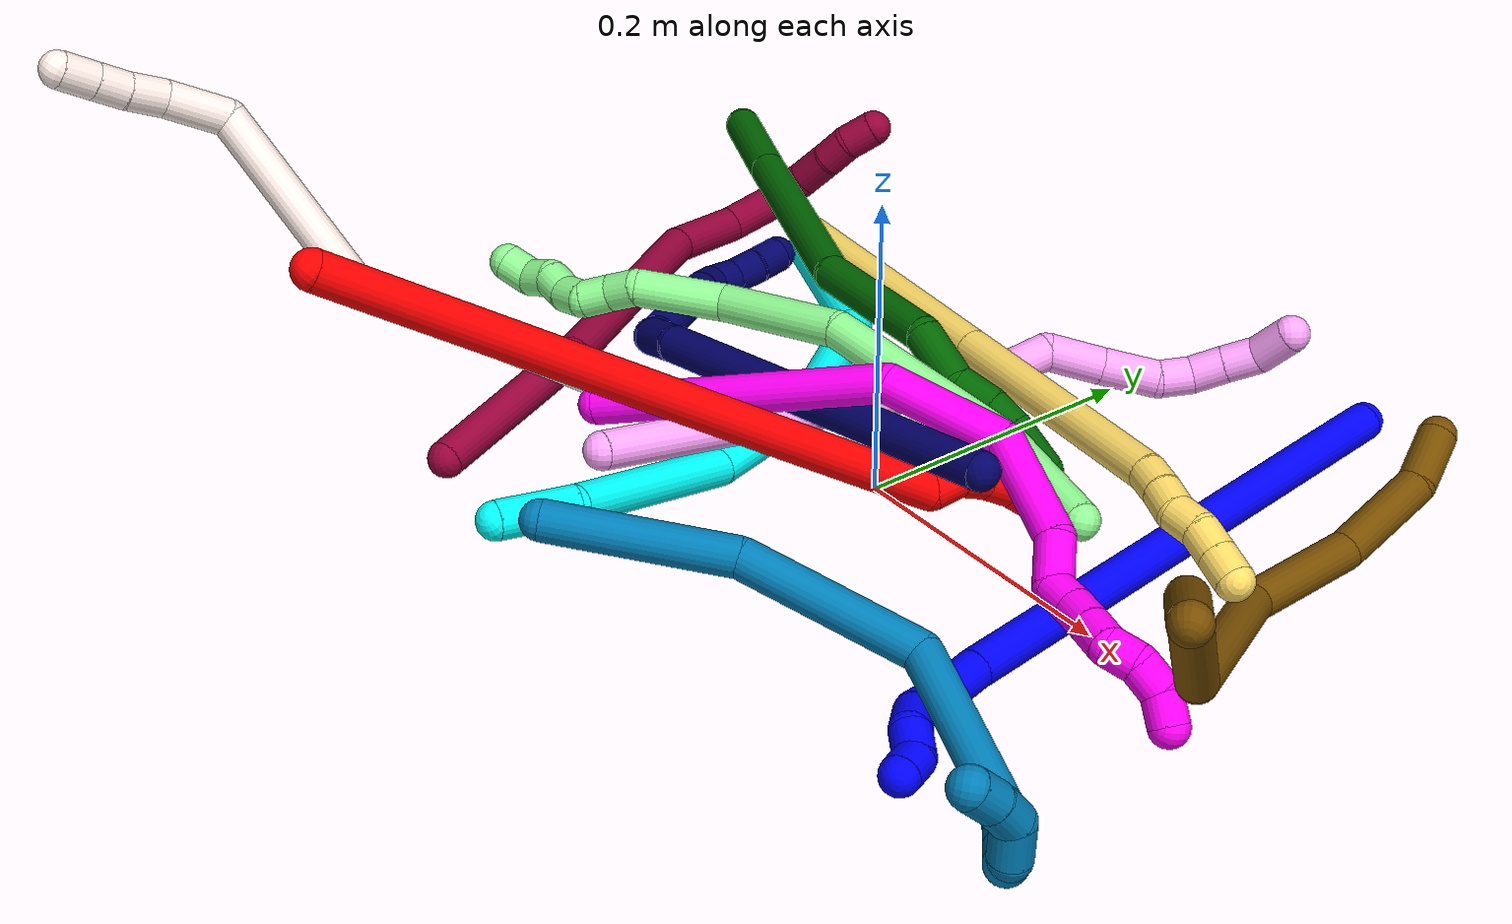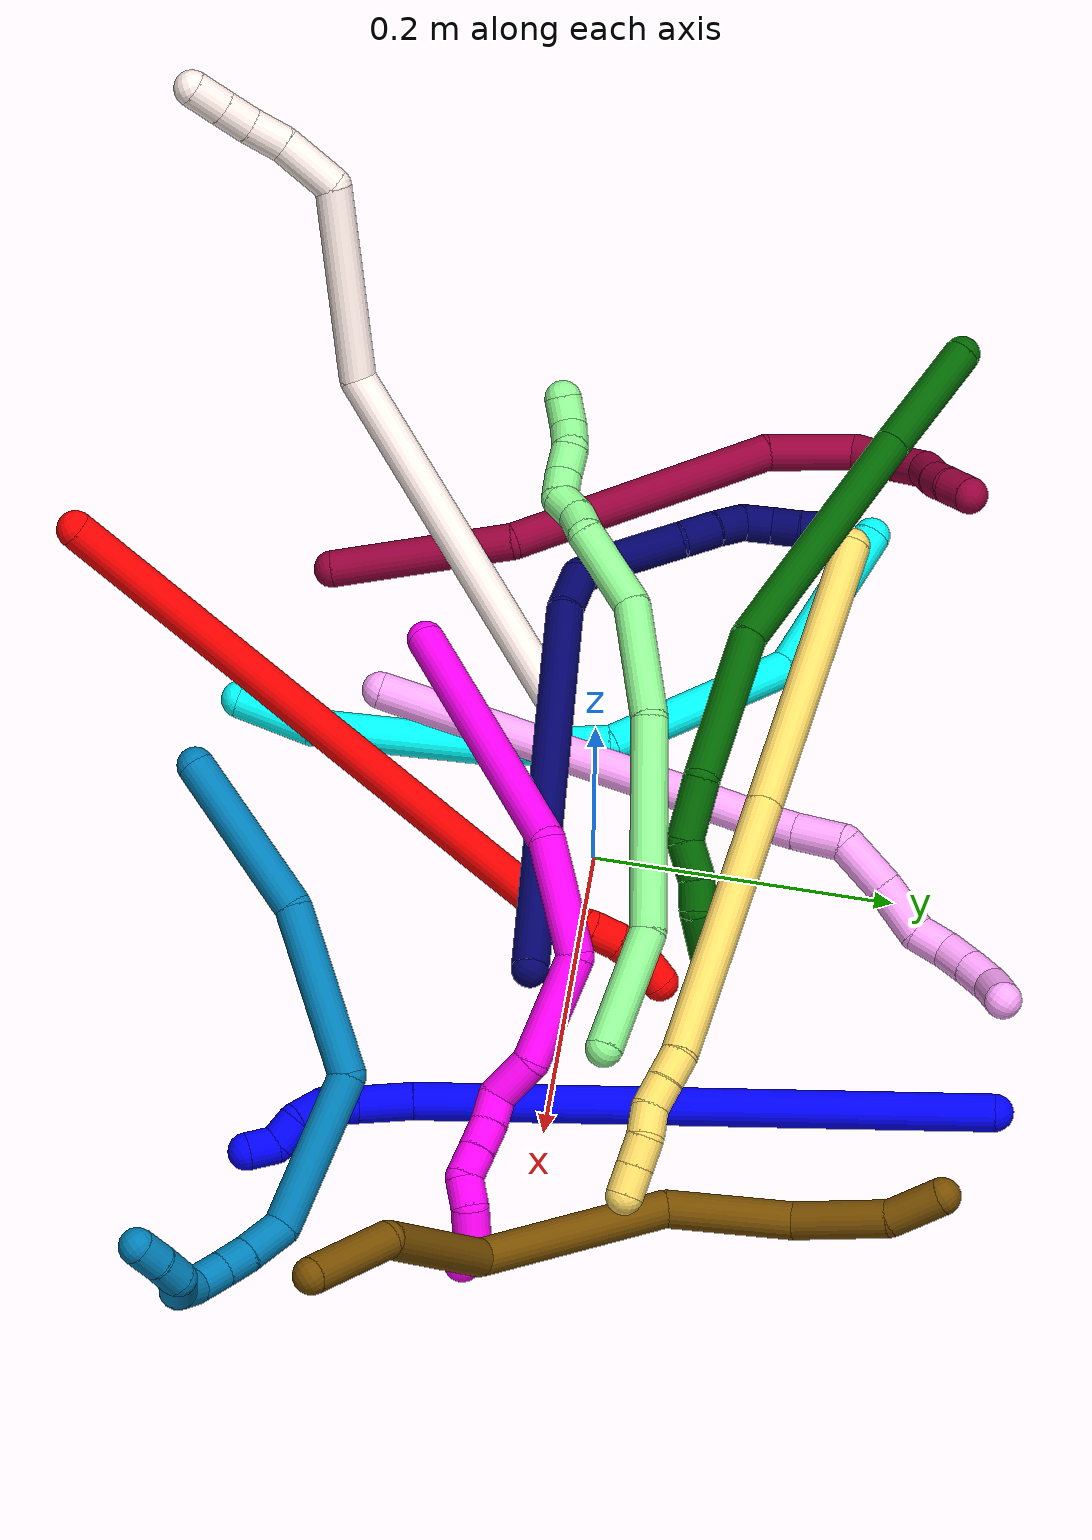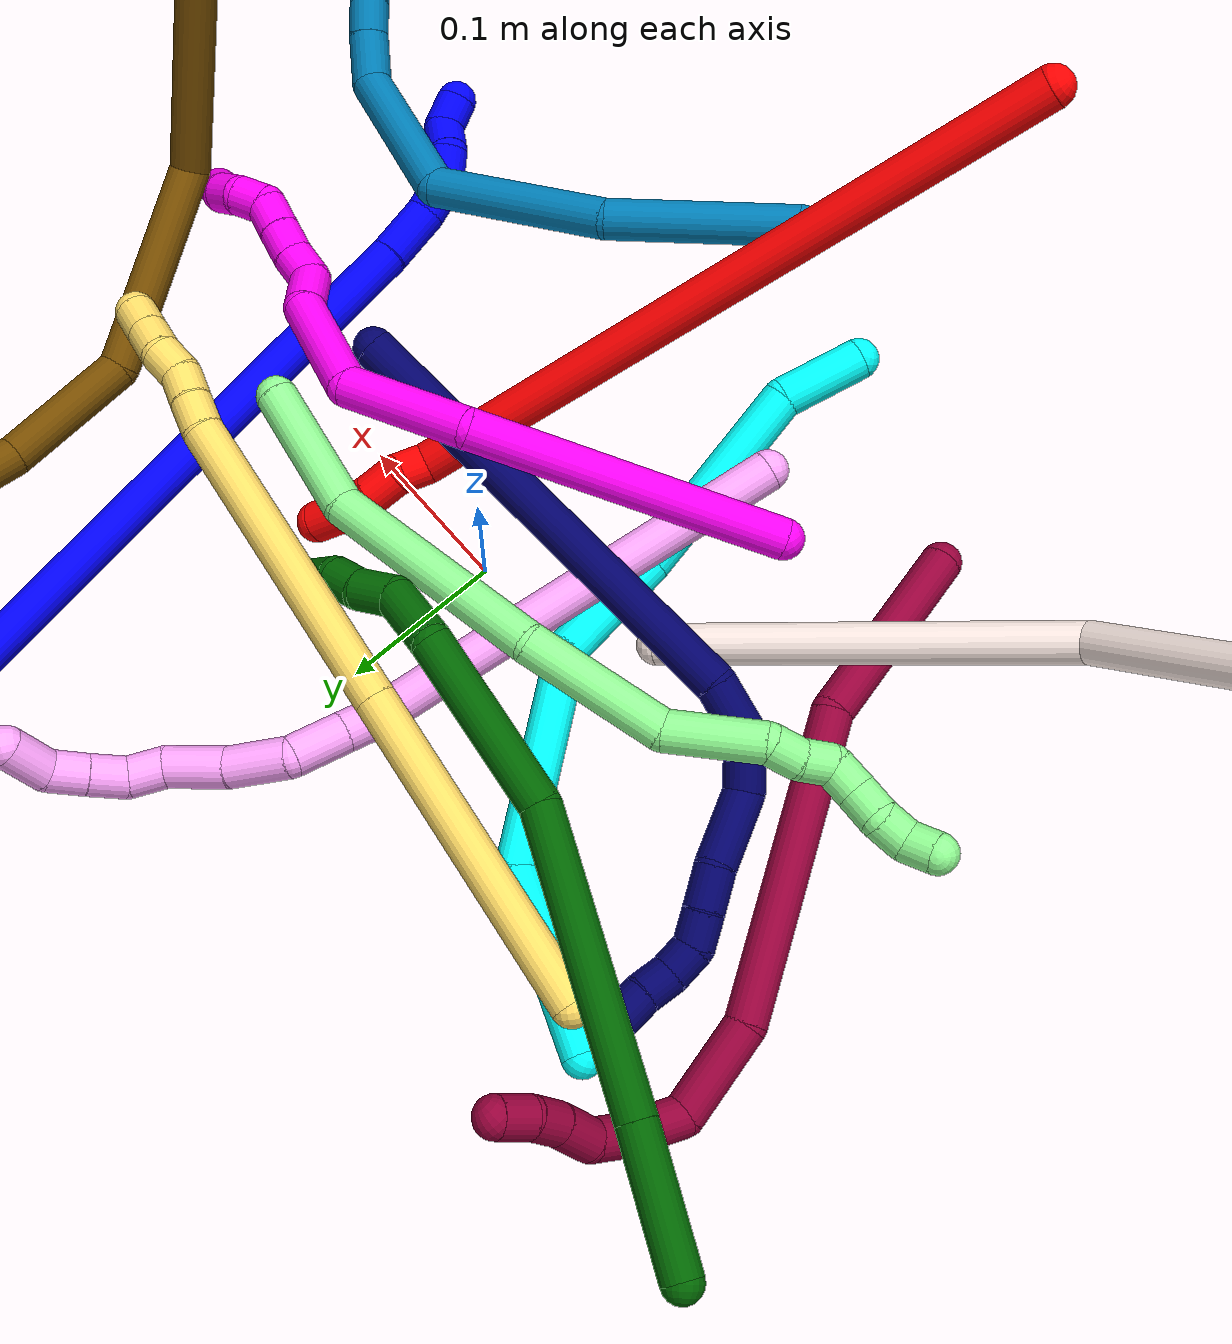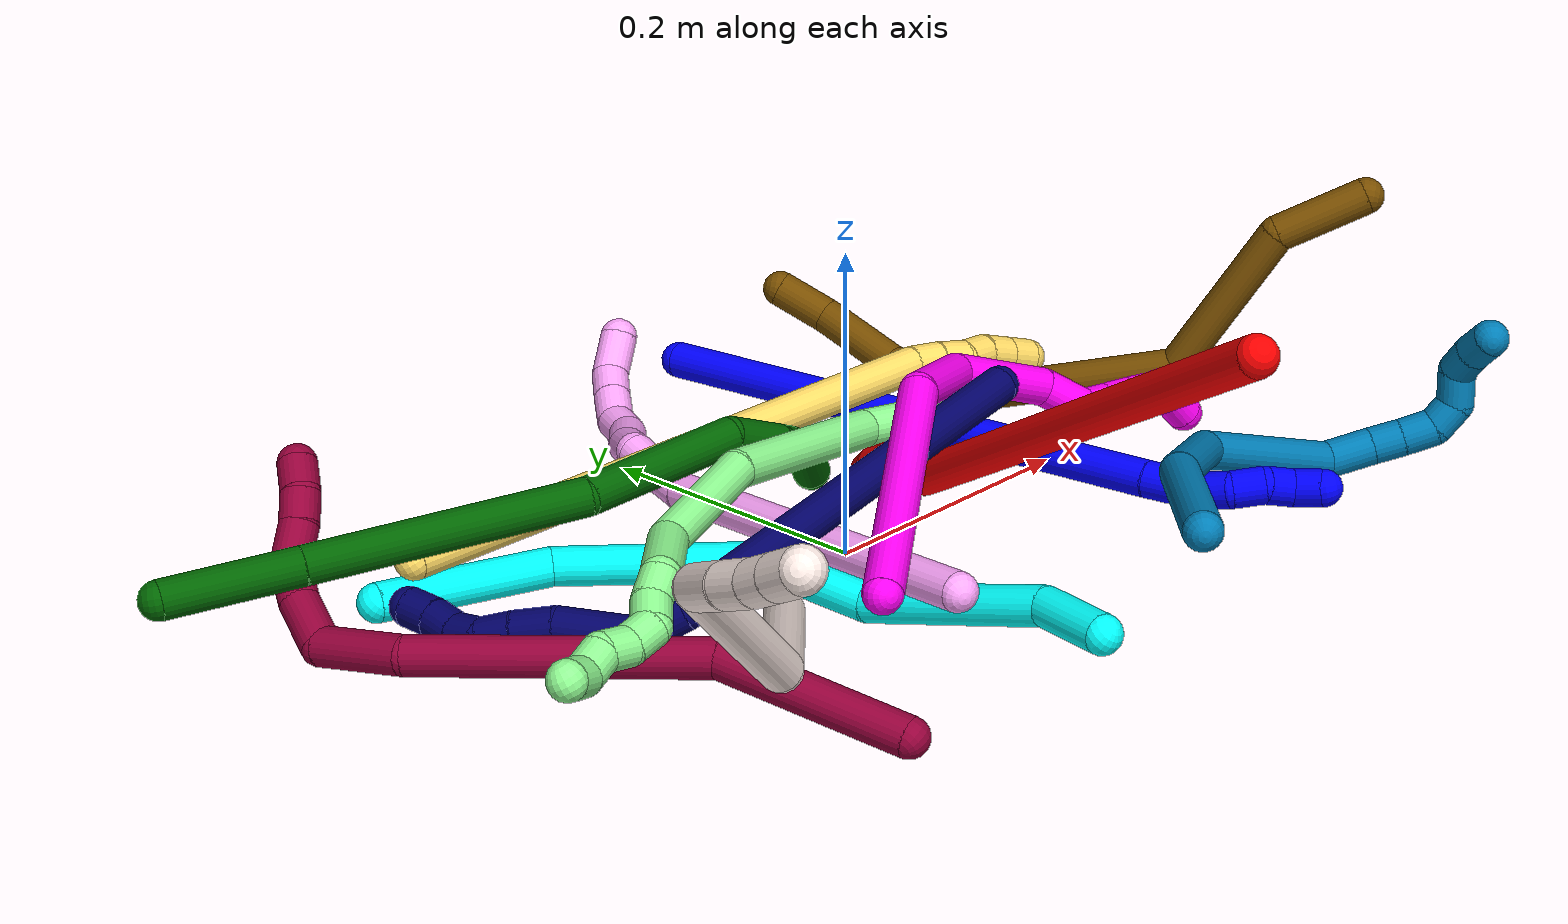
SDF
<sdf version="1.7">
 <world name="default">
  <plugin name="TubeGeneratorPlugin" filename="libtube_generator_plugin.so"/>
  <model name="photoneo_s_sensor">
   <static>1</static>
   <pose>0 0 2 1.57079 1.57079 3.14159</pose>
   <link name="link">
    <inertial><mass>0.1</mass></inertial>
    <sensor name="sensor" type="depth">
     <update_rate>30</update_rate>
     <camera>
      <horizontal_fov>1.22</horizontal_fov>
      <image><width>1920</width><height>1200</height><format>B8G8R8</format></image>
      <clip><near>0.1</near><far>4</far></clip>
      <depth_camera><output>points</output></depth_camera>
     </camera>
     <plugin name="camera_plugin" filename="libgazebo_ros_depth_camera.so">
      <baseline>0.2</baseline>
      <alwaysOn>1</alwaysOn>
      <updateRate>0.0</updateRate>
      <cameraName>camera_ir</cameraName>
      <imageTopicName>/camera/color/image_raw</imageTopicName>
      <cameraInfoTopicName>/camera/color/camera_info</cameraInfoTopicName>
      <depthImageTopicName>/camera/depth/image_raw</depthImageTopicName>
      <depthImageCameraInfoTopicName>/camera/depth/camera_info</depthImageCameraInfoTopicName>
      <pointCloudTopicName>/camera/depth/points</pointCloudTopicName>
      <frameName>fr_optical</frameName>
      <pointCloudCutoff>0.1</pointCloudCutoff>
      <pointCloudCutoffMax>2.0</pointCloudCutoffMax>
      <distortionK1>0</distortionK1>
      <distortionK2>0</distortionK2>
      <distortionK3>0</distortionK3>
      <distortionT1>0</distortionT1>
      <distortionT2>0</distortionT2>
      <CxPrime>0</CxPrime>
      <Cx>0</Cx>
      <Cy>0</Cy>
      <focalLength>0</focalLength>
      <hackBaseline>0</hackBaseline>
     </plugin>
    </sensor>
   </link>
  </model>
  <gravity>0 0 -9.8</gravity>
  <magnetic_field>6e-06 2.3e-05 -4.2e-05</magnetic_field>
  <atmosphere type="adiabatic"/>
  <physics name="default_physics" default="0" type="ode">
   <max_step_size>0.003</max_step_size>
   <real_time_factor>1</real_time_factor>
   <real_time_update_rate>1000</real_time_update_rate>
   <max_contacts>10000</max_contacts>
   <ode>
    <solver>
     <type>quick</type>
     <iters>100</iters>
     <sor>1.3</sor>
     <use_dynamic_moi_rescaling>0</use_dynamic_moi_rescaling>
    </solver>
    <constraints>
     <contact_max_correcting_vel>0</contact_max_correcting_vel>
     <contact_surface_layer>0.001</contact_surface_layer>
     <cfm>0</cfm>
     <erp>0.2</erp>
    </constraints>
   </ode>
  </physics>
  <scene><ambient>0.4 0.4 0.4 1</ambient><background>0.7 0.7 0.7 1</background><shadows>0</shadows></scene>
  <audio><device>default</device></audio>
  <spherical_coordinates>
   <surface_model>EARTH_WGS84</surface_model>
   <latitude_deg>0</latitude_deg>
   <longitude_deg>0</longitude_deg>
   <elevation>0</elevation>
   <heading_deg>0</heading_deg>
  </spherical_coordinates>
  <model name="bin">
   <static>1</static>
   <link name="bottom">
    <collision name="collision-bottom">
     <pose>0 0 -0.01 0 -0 0</pose>
     <geometry><box><size>0.8 0.6 0.02</size></box></geometry>
     <surface>
      <friction><ode><mu>100</mu><mu2>100</mu2></ode></friction>
      <contact><collide_bitmask>65535</collide_bitmask></contact>
     </surface>
    </collision>
   </link>
   <link name="west_wall">
    <collision name="collision-west_wall">
     <pose>-0.41 0 0.1 0 -0 0</pose>
     <geometry><box><size>0.02 0.6 0.2</size></box></geometry>
     <surface>
      <friction><ode><mu>100</mu><mu2>100</mu2></ode></friction>
      <contact><collide_bitmask>65535</collide_bitmask></contact>
     </surface>
    </collision>
   </link>
   <link name="east_wall">
    <collision name="collision-east_wall">
     <pose>0.41 0 0.1 0 -0 0</pose>
     <geometry><box><size>0.02 0.6 0.2</size></box></geometry>
     <surface>
      <friction><ode><mu>100</mu><mu2>100</mu2></ode></friction>
      <contact><collide_bitmask>65535</collide_bitmask></contact>
     </surface>
    </collision>
   </link>
   <link name="south_wall">
    <collision name="collision-south_wall">
     <pose>0 -0.31 0.1 0 -0 0</pose>
     <geometry><box><size>0.8 0.02 0.2</size></box></geometry>
     <surface>
      <friction><ode><mu>100</mu><mu2>100</mu2></ode></friction>
      <contact><collide_bitmask>65535</collide_bitmask></contact>
     </surface>
    </collision>
   </link>
   <link name="north_wall">
    <collision name="collision-north_wall">
     <pose>0 0.31 0.1 0 -0 0</pose>
     <geometry><box><size>0.8 0.02 0.2</size></box></geometry>
     <surface>
      <friction><ode><mu>100</mu><mu2>100</mu2></ode></friction>
      <contact><collide_bitmask>65535</collide_bitmask></contact>
     </surface>
    </collision>
   </link>
  </model>
  <model name="1">
   <static>0</static>
   <link name="1">
    <collision name="collision-cylinder-e_1_1_4">
     <pose>-0.042303 -0.108817 -0.149277 2.51169 -0.225121 -0.66793</pose>
     <geometry><cylinder><radius>0.0125</radius><length>0.379021</length></cylinder></geometry>
     <surface>
      <friction><ode><mu>1.16</mu><mu2>1.16</mu2><slip1>0</slip1><slip2>0</slip2></ode></friction>
      <contact><ode><kp>1e+06</kp><kd>1</kd><max_vel>0</max_vel><min_depth>0.001</min_depth></ode></contact>
     </surface>
    </collision>
    <visual name="visual-cylinder-e_1_1_4">
     <pose>-0.042303 -0.108817 -0.149277 2.51169 -0.225121 -0.66793</pose>
     <geometry><cylinder><radius>0.0125</radius><length>0.379021</length></cylinder></geometry>
     <material><ambient>0 0 1 1</ambient></material>
    </visual>
    <collision name="collision-cylinder-e_2_4_5">
     <pose>-0.089009 -0.22689 -0.313924 2.5996 -0.240593 -0.820768</pose>
     <geometry><cylinder><radius>0.0125</radius><length>0.036948</length></cylinder></geometry>
     <surface>
      <friction><ode><mu>1.16</mu><mu2>1.16</mu2><slip1>0</slip1><slip2>0</slip2></ode></friction>
      <contact><ode><kp>1e+06</kp><kd>1</kd><max_vel>0</max_vel><min_depth>0.001</min_depth></ode></contact>
     </surface>
    </collision>
    <visual name="visual-cylinder-e_2_4_5">
     <pose>-0.089009 -0.22689 -0.313924 2.5996 -0.240593 -0.820768</pose>
     <geometry><cylinder><radius>0.0125</radius><length>0.036948</length></cylinder></geometry>
     <material><ambient>0 0 1 1</ambient></material>
    </visual>
    <collision name="collision-cylinder-e_3_5_6">
     <pose>-0.093343 -0.241289 -0.339176 2.66167 0.006055 0.024747</pose>
     <geometry><cylinder><radius>0.0125</radius><length>0.022282</length></cylinder></geometry>
     <surface>
      <friction><ode><mu>1.16</mu><mu2>1.16</mu2><slip1>0</slip1><slip2>0</slip2></ode></friction>
      <contact><ode><kp>1e+06</kp><kd>1</kd><max_vel>0</max_vel><min_depth>0.001</min_depth></ode></contact>
     </surface>
    </collision>
    <visual name="visual-cylinder-e_3_5_6">
     <pose>-0.093343 -0.241289 -0.339176 2.66167 0.006055 0.024747</pose>
     <geometry><cylinder><radius>0.0125</radius><length>0.022282</length></cylinder></geometry>
     <material><ambient>0 0 1 1</ambient></material>
    </visual>
    <collision name="collision-cylinder-e_4_6_7">
     <pose>-0.09368 -0.246683 -0.359862 3.11847 -0.037419 -2.03448</pose>
     <geometry><cylinder><radius>0.0125</radius><length>0.021628</length></cylinder></geometry>
     <surface>
      <friction><ode><mu>1.16</mu><mu2>1.16</mu2><slip1>0</slip1><slip2>0</slip2></ode></friction>
      <contact><ode><kp>1e+06</kp><kd>1</kd><max_vel>0</max_vel><min_depth>0.001</min_depth></ode></contact>
     </surface>
    </collision>
    <visual name="visual-cylinder-e_4_6_7">
     <pose>-0.09368 -0.246683 -0.359862 3.11847 -0.037419 -2.03448</pose>
     <geometry><cylinder><radius>0.0125</radius><length>0.021628</length></cylinder></geometry>
     <material><ambient>0 0 1 1</ambient></material>
    </visual>
    <collision name="collision-cylinder-e_5_7_8">
     <pose>-0.097488 -0.24413 -0.379679 -2.84015 -0.34609 1.7109</pose>
     <geometry><cylinder><radius>0.0125</radius><length>0.020068</length></cylinder></geometry>
     <surface>
      <friction><ode><mu>1.16</mu><mu2>1.16</mu2><slip1>0</slip1><slip2>0</slip2></ode></friction>
      <contact><ode><kp>1e+06</kp><kd>1</kd><max_vel>0</max_vel><min_depth>0.001</min_depth></ode></contact>
     </surface>
    </collision>
    <visual name="visual-cylinder-e_5_7_8">
     <pose>-0.097488 -0.24413 -0.379679 -2.84015 -0.34609 1.7109</pose>
     <geometry><cylinder><radius>0.0125</radius><length>0.020068</length></cylinder></geometry>
     <material><ambient>0 0 1 1</ambient></material>
    </visual>
    <collision name="collision-cylinder-e_6_8_2">
     <pose>-0.101852 -0.244468 -0.398166 2.82148 -0.095842 -0.577529</pose>
     <geometry><cylinder><radius>0.0125</radius><length>0.020053</length></cylinder></geometry>
     <surface>
      <friction><ode><mu>1.16</mu><mu2>1.16</mu2><slip1>0</slip1><slip2>0</slip2></ode></friction>
      <contact><ode><kp>1e+06</kp><kd>1</kd><max_vel>0</max_vel><min_depth>0.001</min_depth></ode></contact>
     </surface>
    </collision>
    <visual name="visual-cylinder-e_6_8_2">
     <pose>-0.101852 -0.244468 -0.398166 2.82148 -0.095842 -0.577529</pose>
     <geometry><cylinder><radius>0.0125</radius><length>0.020053</length></cylinder></geometry>
     <material><ambient>0 0 1 1</ambient></material>
    </visual>
    <collision name="collision-sphere-2">
     <pose>-0.102811 -0.247609 -0.407639 0 -0 0</pose>
     <geometry><sphere><radius>0.0125</radius></sphere></geometry>
     <surface>
      <friction><ode><mu>1.16</mu><mu2>1.16</mu2><slip1>0</slip1><slip2>0</slip2></ode></friction>
      <contact><ode><kp>1e+06</kp><kd>1</kd><max_vel>0</max_vel><min_depth>0.001</min_depth></ode></contact>
     </surface>
    </collision>
    <visual name="visual-sphere-2">
     <pose>-0.102811 -0.247609 -0.407639 0 -0 0</pose>
     <geometry><sphere><radius>0.0125</radius></sphere></geometry>
     <material><ambient>0 0 1 1</ambient></material>
    </visual>
    <collision name="collision-sphere-4">
     <pose>-0.084607 -0.217635 -0.298553 0 -0 0</pose>
     <geometry><sphere><radius>0.0125</radius></sphere></geometry>
     <surface>
      <friction><ode><mu>1.16</mu><mu2>1.16</mu2><slip1>0</slip1><slip2>0</slip2></ode></friction>
      <contact><ode><kp>1e+06</kp><kd>1</kd><max_vel>0</max_vel><min_depth>0.001</min_depth></ode></contact>
     </surface>
    </collision>
    <visual name="visual-sphere-4">
     <pose>-0.084607 -0.217635 -0.298553 0 -0 0</pose>
     <geometry><sphere><radius>0.0125</radius></sphere></geometry>
     <material><ambient>0 0 1 1</ambient></material>
    </visual>
    <collision name="collision-sphere-1">
     <geometry><sphere><radius>0.0125</radius></sphere></geometry>
     <surface>
      <friction><ode><mu>1.16</mu><mu2>1.16</mu2><slip1>0</slip1><slip2>0</slip2></ode></friction>
      <contact><ode><kp>1e+06</kp><kd>1</kd><max_vel>0</max_vel><min_depth>0.001</min_depth></ode></contact>
     </surface>
    </collision>
    <visual name="visual-sphere-1">
     <geometry><sphere><radius>0.0125</radius></sphere></geometry>
     <material><ambient>0 0 1 1</ambient></material>
    </visual>
    <collision name="collision-sphere-8">
     <pose>-0.100892 -0.241328 -0.388692 0 -0 0</pose>
     <geometry><sphere><radius>0.0125</radius></sphere></geometry>
     <surface>
      <friction><ode><mu>1.16</mu><mu2>1.16</mu2><slip1>0</slip1><slip2>0</slip2></ode></friction>
      <contact><ode><kp>1e+06</kp><kd>1</kd><max_vel>0</max_vel><min_depth>0.001</min_depth></ode></contact>
     </surface>
    </collision>
    <visual name="visual-sphere-8">
     <pose>-0.100892 -0.241328 -0.388692 0 -0 0</pose>
     <geometry><sphere><radius>0.0125</radius></sphere></geometry>
     <material><ambient>0 0 1 1</ambient></material>
    </visual>
    <collision name="collision-sphere-5">
     <pose>-0.093411 -0.236145 -0.329294 0 -0 0</pose>
     <geometry><sphere><radius>0.0125</radius></sphere></geometry>
     <surface>
      <friction><ode><mu>1.16</mu><mu2>1.16</mu2><slip1>0</slip1><slip2>0</slip2></ode></friction>
      <contact><ode><kp>1e+06</kp><kd>1</kd><max_vel>0</max_vel><min_depth>0.001</min_depth></ode></contact>
     </surface>
    </collision>
    <visual name="visual-sphere-5">
     <pose>-0.093411 -0.236145 -0.329294 0 -0 0</pose>
     <geometry><sphere><radius>0.0125</radius></sphere></geometry>
     <material><ambient>0 0 1 1</ambient></material>
    </visual>
    <collision name="collision-sphere-6">
     <pose>-0.093276 -0.246433 -0.349059 0 -0 0</pose>
     <geometry><sphere><radius>0.0125</radius></sphere></geometry>
     <surface>
      <friction><ode><mu>1.16</mu><mu2>1.16</mu2><slip1>0</slip1><slip2>0</slip2></ode></friction>
      <contact><ode><kp>1e+06</kp><kd>1</kd><max_vel>0</max_vel><min_depth>0.001</min_depth></ode></contact>
     </surface>
    </collision>
    <visual name="visual-sphere-6">
     <pose>-0.093276 -0.246433 -0.349059 0 -0 0</pose>
     <geometry><sphere><radius>0.0125</radius></sphere></geometry>
     <material><ambient>0 0 1 1</ambient></material>
    </visual>
    <collision name="collision-sphere-7">
     <pose>-0.094085 -0.246932 -0.370666 0 -0 0</pose>
     <geometry><sphere><radius>0.0125</radius></sphere></geometry>
     <surface>
      <friction><ode><mu>1.16</mu><mu2>1.16</mu2><slip1>0</slip1><slip2>0</slip2></ode></friction>
      <contact><ode><kp>1e+06</kp><kd>1</kd><max_vel>0</max_vel><min_depth>0.001</min_depth></ode></contact>
     </surface>
    </collision>
    <visual name="visual-sphere-7">
     <pose>-0.094085 -0.246932 -0.370666 0 -0 0</pose>
     <geometry><sphere><radius>0.0125</radius></sphere></geometry>
     <material><ambient>0 0 1 1</ambient></material>
    </visual>
    <inertial>
     <pose>-0.054855 -0.140281 -0.198244 0 -0 0</pose>
     <mass>0.5</mass>
     <inertia>
      <ixx>0.000728</ixx>
      <ixy>0</ixy>
      <ixz>0</ixz>
      <iyy>-0.005294</iyy>
      <iyz>0</iyz>
      <izz>0.003604</izz>
     </inertia>
    </inertial>
   </link>
   <pose>0.14253 0.288501 0.012597 -2.43681 -1.34614 1.64263</pose>
  </model>
  <model name="2">
   <static>0</static>
   <link name="2">
    <collision name="collision-cylinder-e_1_1_4">
     <pose>-0.017324 0.049232 -0.203187 -2.90388 -0.082674 0.666824</pose>
     <geometry><cylinder><radius>0.0125</radius><length>0.419566</length></cylinder></geometry>
     <surface>
      <friction><ode><mu>1.16</mu><mu2>1.16</mu2><slip1>0</slip1><slip2>0</slip2></ode></friction>
      <contact><ode><kp>1e+06</kp><kd>1</kd><max_vel>0</max_vel><min_depth>0.001</min_depth></ode></contact>
     </surface>
    </collision>
    <visual name="visual-cylinder-e_1_1_4">
     <pose>-0.017324 0.049232 -0.203187 -2.90388 -0.082674 0.666824</pose>
     <geometry><cylinder><radius>0.0125</radius><length>0.419566</length></cylinder></geometry>
     <material><ambient>1 0 0 1</ambient></material>
    </visual>
    <collision name="collision-cylinder-e_2_4_5">
     <pose>-0.0342 0.106935 -0.411709 -2.13275 0.044622 -0.080798</pose>
     <geometry><cylinder><radius>0.0125</radius><length>0.020044</length></cylinder></geometry>
     <surface>
      <friction><ode><mu>1.16</mu><mu2>1.16</mu2><slip1>0</slip1><slip2>0</slip2></ode></friction>
      <contact><ode><kp>1e+06</kp><kd>1</kd><max_vel>0</max_vel><min_depth>0.001</min_depth></ode></contact>
     </surface>
    </collision>
    <visual name="visual-cylinder-e_2_4_5">
     <pose>-0.0342 0.106935 -0.411709 -2.13275 0.044622 -0.080798</pose>
     <geometry><cylinder><radius>0.0125</radius><length>0.020044</length></cylinder></geometry>
     <material><ambient>1 0 0 1</ambient></material>
    </visual>
    <collision name="collision-cylinder-e_3_5_6">
     <pose>-0.035934 0.119597 -0.425939 -2.70141 -0.21821 0.910647</pose>
     <geometry><cylinder><radius>0.0125</radius><length>0.020142</length></cylinder></geometry>
     <surface>
      <friction><ode><mu>1.16</mu><mu2>1.16</mu2><slip1>0</slip1><slip2>0</slip2></ode></friction>
      <contact><ode><kp>1e+06</kp><kd>1</kd><max_vel>0</max_vel><min_depth>0.001</min_depth></ode></contact>
     </surface>
    </collision>
    <visual name="visual-cylinder-e_3_5_6">
     <pose>-0.035934 0.119597 -0.425939 -2.70141 -0.21821 0.910647</pose>
     <geometry><cylinder><radius>0.0125</radius><length>0.020142</length></cylinder></geometry>
     <material><ambient>1 0 0 1</ambient></material>
    </visual>
    <collision name="collision-cylinder-e_4_6_7">
     <pose>-0.039087 0.126541 -0.444412 -2.86161 -0.097365 0.665772</pose>
     <geometry><cylinder><radius>0.0125</radius><length>0.020027</length></cylinder></geometry>
     <surface>
      <friction><ode><mu>1.16</mu><mu2>1.16</mu2><slip1>0</slip1><slip2>0</slip2></ode></friction>
      <contact><ode><kp>1e+06</kp><kd>1</kd><max_vel>0</max_vel><min_depth>0.001</min_depth></ode></contact>
     </surface>
    </collision>
    <visual name="visual-cylinder-e_4_6_7">
     <pose>-0.039087 0.126541 -0.444412 -2.86161 -0.097365 0.665772</pose>
     <geometry><cylinder><radius>0.0125</radius><length>0.020027</length></cylinder></geometry>
     <material><ambient>1 0 0 1</ambient></material>
    </visual>
    <collision name="collision-cylinder-e_5_7_2">
     <pose>-0.039311 0.130136 -0.464038 -3.05805 0.074226 -1.4527</pose>
     <geometry><cylinder><radius>0.0125</radius><length>0.020221</length></cylinder></geometry>
     <surface>
      <friction><ode><mu>1.16</mu><mu2>1.16</mu2><slip1>0</slip1><slip2>0</slip2></ode></friction>
      <contact><ode><kp>1e+06</kp><kd>1</kd><max_vel>0</max_vel><min_depth>0.001</min_depth></ode></contact>
     </surface>
    </collision>
    <visual name="visual-cylinder-e_5_7_2">
     <pose>-0.039311 0.130136 -0.464038 -3.05805 0.074226 -1.4527</pose>
     <geometry><cylinder><radius>0.0125</radius><length>0.020221</length></cylinder></geometry>
     <material><ambient>1 0 0 1</ambient></material>
    </visual>
    <collision name="collision-sphere-2">
     <pose>-0.038561 0.130978 -0.474085 0 -0 0</pose>
     <geometry><sphere><radius>0.0125</radius></sphere></geometry>
     <surface>
      <friction><ode><mu>1.16</mu><mu2>1.16</mu2><slip1>0</slip1><slip2>0</slip2></ode></friction>
      <contact><ode><kp>1e+06</kp><kd>1</kd><max_vel>0</max_vel><min_depth>0.001</min_depth></ode></contact>
     </surface>
    </collision>
    <visual name="visual-sphere-2">
     <pose>-0.038561 0.130978 -0.474085 0 -0 0</pose>
     <geometry><sphere><radius>0.0125</radius></sphere></geometry>
     <material><ambient>1 0 0 1</ambient></material>
    </visual>
    <collision name="collision-sphere-7">
     <pose>-0.040061 0.129295 -0.45399 0 -0 0</pose>
     <geometry><sphere><radius>0.0125</radius></sphere></geometry>
     <surface>
      <friction><ode><mu>1.16</mu><mu2>1.16</mu2><slip1>0</slip1><slip2>0</slip2></ode></friction>
      <contact><ode><kp>1e+06</kp><kd>1</kd><max_vel>0</max_vel><min_depth>0.001</min_depth></ode></contact>
     </surface>
    </collision>
    <visual name="visual-sphere-7">
     <pose>-0.040061 0.129295 -0.45399 0 -0 0</pose>
     <geometry><sphere><radius>0.0125</radius></sphere></geometry>
     <material><ambient>1 0 0 1</ambient></material>
    </visual>
    <collision name="collision-sphere-6">
     <pose>-0.038114 0.123787 -0.434834 0 -0 0</pose>
     <geometry><sphere><radius>0.0125</radius></sphere></geometry>
     <surface>
      <friction><ode><mu>1.16</mu><mu2>1.16</mu2><slip1>0</slip1><slip2>0</slip2></ode></friction>
      <contact><ode><kp>1e+06</kp><kd>1</kd><max_vel>0</max_vel><min_depth>0.001</min_depth></ode></contact>
     </surface>
    </collision>
    <visual name="visual-sphere-6">
     <pose>-0.038114 0.123787 -0.434834 0 -0 0</pose>
     <geometry><sphere><radius>0.0125</radius></sphere></geometry>
     <material><ambient>1 0 0 1</ambient></material>
    </visual>
    <collision name="collision-sphere-5">
     <pose>-0.033753 0.115408 -0.417044 0 -0 0</pose>
     <geometry><sphere><radius>0.0125</radius></sphere></geometry>
     <surface>
      <friction><ode><mu>1.16</mu><mu2>1.16</mu2><slip1>0</slip1><slip2>0</slip2></ode></friction>
      <contact><ode><kp>1e+06</kp><kd>1</kd><max_vel>0</max_vel><min_depth>0.001</min_depth></ode></contact>
     </surface>
    </collision>
    <visual name="visual-sphere-5">
     <pose>-0.033753 0.115408 -0.417044 0 -0 0</pose>
     <geometry><sphere><radius>0.0125</radius></sphere></geometry>
     <material><ambient>1 0 0 1</ambient></material>
    </visual>
    <collision name="collision-sphere-1">
     <geometry><sphere><radius>0.0125</radius></sphere></geometry>
     <surface>
      <friction><ode><mu>1.16</mu><mu2>1.16</mu2><slip1>0</slip1><slip2>0</slip2></ode></friction>
      <contact><ode><kp>1e+06</kp><kd>1</kd><max_vel>0</max_vel><min_depth>0.001</min_depth></ode></contact>
     </surface>
    </collision>
    <visual name="visual-sphere-1">
     <geometry><sphere><radius>0.0125</radius></sphere></geometry>
     <material><ambient>1 0 0 1</ambient></material>
    </visual>
    <collision name="collision-sphere-4">
     <pose>-0.034648 0.098463 -0.406374 0 -0 0</pose>
     <geometry><sphere><radius>0.0125</radius></sphere></geometry>
     <surface>
      <friction><ode><mu>1.16</mu><mu2>1.16</mu2><slip1>0</slip1><slip2>0</slip2></ode></friction>
      <contact><ode><kp>1e+06</kp><kd>1</kd><max_vel>0</max_vel><min_depth>0.001</min_depth></ode></contact>
     </surface>
    </collision>
    <visual name="visual-sphere-4">
     <pose>-0.034648 0.098463 -0.406374 0 -0 0</pose>
     <geometry><sphere><radius>0.0125</radius></sphere></geometry>
     <material><ambient>1 0 0 1</ambient></material>
    </visual>
    <inertial>
     <pose>-0.020511 0.060748 -0.240731 0 -0 0</pose>
     <mass>0.5</mass>
     <inertia>
      <ixx>0.008638</ixx>
      <ixy>0</ixy>
      <ixz>0</ixz>
      <iyy>-0.000827</iyy>
      <iyz>0</iyz>
      <izz>-0.000978</izz>
     </inertia>
    </inertial>
   </link>
   <pose>-0.063243 -0.350103 0.24435 0.806725 -0.341844 -0.255063</pose>
  </model>
  <model name="3">
   <static>0</static>
   <link name="3">
    <collision name="collision-cylinder-e_1_1_4">
     <pose>0.014779 -0.050533 0.021248 1.17276 0.26334 0.17551</pose>
     <geometry><cylinder><radius>0.0125</radius><length>0.113553</length></cylinder></geometry>
     <surface>
      <friction><ode><mu>1.16</mu><mu2>1.16</mu2><slip1>0</slip1><slip2>0</slip2></ode></friction>
      <contact><ode><kp>1e+06</kp><kd>1</kd><max_vel>0</max_vel><min_depth>0.001</min_depth></ode></contact>
     </surface>
    </collision>
    <visual name="visual-cylinder-e_1_1_4">
     <pose>0.014779 -0.050533 0.021248 1.17276 0.26334 0.17551</pose>
     <geometry><cylinder><radius>0.0125</radius><length>0.113553</length></cylinder></geometry>
     <material><ambient>0.003922 1 0.996078 1</ambient></material>
    </visual>
    <collision name="collision-cylinder-e_2_4_5">
     <pose>0.017499 -0.148931 0.086615 0.826099 -0.183187 -0.080466</pose>
     <geometry><cylinder><radius>0.0125</radius><length>0.132406</length></cylinder></geometry>
     <surface>
      <friction><ode><mu>1.16</mu><mu2>1.16</mu2><slip1>0</slip1><slip2>0</slip2></ode></friction>
      <contact><ode><kp>1e+06</kp><kd>1</kd><max_vel>0</max_vel><min_depth>0.001</min_depth></ode></contact>
     </surface>
    </collision>
    <visual name="visual-cylinder-e_2_4_5">
     <pose>0.017499 -0.148931 0.086615 0.826099 -0.183187 -0.080466</pose>
     <geometry><cylinder><radius>0.0125</radius><length>0.132406</length></cylinder></geometry>
     <material><ambient>0.003922 1 0.996078 1</ambient></material>
    </visual>
    <collision name="collision-cylinder-e_3_5_6">
     <pose>-0.018791 -0.215366 0.153352 0.687455 -0.691547 -0.256475</pose>
     <geometry><cylinder><radius>0.0125</radius><length>0.075988</length></cylinder></geometry>
     <surface>
      <friction><ode><mu>1.16</mu><mu2>1.16</mu2><slip1>0</slip1><slip2>0</slip2></ode></friction>
      <contact><ode><kp>1e+06</kp><kd>1</kd><max_vel>0</max_vel><min_depth>0.001</min_depth></ode></contact>
     </surface>
    </collision>
    <visual name="visual-cylinder-e_3_5_6">
     <pose>-0.018791 -0.215366 0.153352 0.687455 -0.691547 -0.256475</pose>
     <geometry><cylinder><radius>0.0125</radius><length>0.075988</length></cylinder></geometry>
     <material><ambient>0.003922 1 0.996078 1</ambient></material>
    </visual>
    <collision name="collision-cylinder-e_4_6_7">
     <pose>-0.071154 -0.254926 0.228369 0.380989 -0.462368 -0.090721</pose>
     <geometry><cylinder><radius>0.0125</radius><length>0.126137</length></cylinder></geometry>
     <surface>
      <friction><ode><mu>1.16</mu><mu2>1.16</mu2><slip1>0</slip1><slip2>0</slip2></ode></friction>
      <contact><ode><kp>1e+06</kp><kd>1</kd><max_vel>0</max_vel><min_depth>0.001</min_depth></ode></contact>
     </surface>
    </collision>
    <visual name="visual-cylinder-e_4_6_7">
     <pose>-0.071154 -0.254926 0.228369 0.380989 -0.462368 -0.090721</pose>
     <geometry><cylinder><radius>0.0125</radius><length>0.126137</length></cylinder></geometry>
     <material><ambient>0.003922 1 0.996078 1</ambient></material>
    </visual>
    <collision name="collision-cylinder-e_5_7_2">
     <pose>-0.11877 -0.278882 0.297661 0.173828 -0.848956 -0.07872</pose>
     <geometry><cylinder><radius>0.0125</radius><length>0.051916</length></cylinder></geometry>
     <surface>
      <friction><ode><mu>1.16</mu><mu2>1.16</mu2><slip1>0</slip1><slip2>0</slip2></ode></friction>
      <contact><ode><kp>1e+06</kp><kd>1</kd><max_vel>0</max_vel><min_depth>0.001</min_depth></ode></contact>
     </surface>
    </collision>
    <visual name="visual-cylinder-e_5_7_2">
     <pose>-0.11877 -0.278882 0.297661 0.173828 -0.848956 -0.07872</pose>
     <geometry><cylinder><radius>0.0125</radius><length>0.051916</length></cylinder></geometry>
     <material><ambient>0.003922 1 0.996078 1</ambient></material>
    </visual>
    <collision name="collision-sphere-2">
     <pose>-0.138254 -0.281848 0.314555 0 -0 0</pose>
     <geometry><sphere><radius>0.0125</radius></sphere></geometry>
     <surface>
      <friction><ode><mu>1.16</mu><mu2>1.16</mu2><slip1>0</slip1><slip2>0</slip2></ode></friction>
      <contact><ode><kp>1e+06</kp><kd>1</kd><max_vel>0</max_vel><min_depth>0.001</min_depth></ode></contact>
     </surface>
    </collision>
    <visual name="visual-sphere-2">
     <pose>-0.138254 -0.281848 0.314555 0 -0 0</pose>
     <geometry><sphere><radius>0.0125</radius></sphere></geometry>
     <material><ambient>0.003922 1 0.996078 1</ambient></material>
    </visual>
    <collision name="collision-sphere-7">
     <pose>-0.099287 -0.275915 0.280767 0 -0 0</pose>
     <geometry><sphere><radius>0.0125</radius></sphere></geometry>
     <surface>
      <friction><ode><mu>1.16</mu><mu2>1.16</mu2><slip1>0</slip1><slip2>0</slip2></ode></friction>
      <contact><ode><kp>1e+06</kp><kd>1</kd><max_vel>0</max_vel><min_depth>0.001</min_depth></ode></contact>
     </surface>
    </collision>
    <visual name="visual-sphere-7">
     <pose>-0.099287 -0.275915 0.280767 0 -0 0</pose>
     <geometry><sphere><radius>0.0125</radius></sphere></geometry>
     <material><ambient>0.003922 1 0.996078 1</ambient></material>
    </visual>
    <collision name="collision-sphere-6">
     <pose>-0.043021 -0.233937 0.17597 0 -0 0</pose>
     <geometry><sphere><radius>0.0125</radius></sphere></geometry>
     <surface>
      <friction><ode><mu>1.16</mu><mu2>1.16</mu2><slip1>0</slip1><slip2>0</slip2></ode></friction>
      <contact><ode><kp>1e+06</kp><kd>1</kd><max_vel>0</max_vel><min_depth>0.001</min_depth></ode></contact>
     </surface>
    </collision>
    <visual name="visual-sphere-6">
     <pose>-0.043021 -0.233937 0.17597 0 -0 0</pose>
     <geometry><sphere><radius>0.0125</radius></sphere></geometry>
     <material><ambient>0.003922 1 0.996078 1</ambient></material>
    </visual>
    <collision name="collision-sphere-5">
     <pose>0.005439 -0.196795 0.130734 0 -0 0</pose>
     <geometry><sphere><radius>0.0125</radius></sphere></geometry>
     <surface>
      <friction><ode><mu>1.16</mu><mu2>1.16</mu2><slip1>0</slip1><slip2>0</slip2></ode></friction>
      <contact><ode><kp>1e+06</kp><kd>1</kd><max_vel>0</max_vel><min_depth>0.001</min_depth></ode></contact>
     </surface>
    </collision>
    <visual name="visual-sphere-5">
     <pose>0.005439 -0.196795 0.130734 0 -0 0</pose>
     <geometry><sphere><radius>0.0125</radius></sphere></geometry>
     <material><ambient>0.003922 1 0.996078 1</ambient></material>
    </visual>
    <collision name="collision-sphere-1">
     <geometry><sphere><radius>0.0125</radius></sphere></geometry>
     <surface>
      <friction><ode><mu>1.16</mu><mu2>1.16</mu2><slip1>0</slip1><slip2>0</slip2></ode></friction>
      <contact><ode><kp>1e+06</kp><kd>1</kd><max_vel>0</max_vel><min_depth>0.001</min_depth></ode></contact>
     </surface>
    </collision>
    <visual name="visual-sphere-1">
     <geometry><sphere><radius>0.0125</radius></sphere></geometry>
     <material><ambient>0.003922 1 0.996078 1</ambient></material>
    </visual>
    <collision name="collision-sphere-4">
     <pose>0.029559 -0.101067 0.042497 0 -0 0</pose>
     <geometry><sphere><radius>0.0125</radius></sphere></geometry>
     <surface>
      <friction><ode><mu>1.16</mu><mu2>1.16</mu2><slip1>0</slip1><slip2>0</slip2></ode></friction>
      <contact><ode><kp>1e+06</kp><kd>1</kd><max_vel>0</max_vel><min_depth>0.001</min_depth></ode></contact>
     </surface>
    </collision>
    <visual name="visual-sphere-4">
     <pose>0.029559 -0.101067 0.042497 0 -0 0</pose>
     <geometry><sphere><radius>0.0125</radius></sphere></geometry>
     <material><ambient>0.003922 1 0.996078 1</ambient></material>
    </visual>
    <inertial>
     <pose>-0.025148 -0.176914 0.139586 0 -0 0</pose>
     <mass>0.5</mass>
     <inertia>
      <ixx>0.000479</ixx>
      <ixy>0</ixy>
      <ixz>0</ixz>
      <iyy>0.00036</iyy>
      <iyz>0</iyz>
      <izz>0.000474</izz>
     </inertia>
    </inertial>
   </link>
   <pose>-0.259978 0.146013 0.011474 0.555743 -0.52759 0.897884</pose>
  </model>
  <model name="4">
   <static>0</static>
   <link name="4">
    <collision name="collision-cylinder-e_1_1_4">
     <pose>0.039434 -0.006674 0.108438 0.061467 0.348181 0.010813</pose>
     <geometry><cylinder><radius>0.0125</radius><length>0.231157</length></cylinder></geometry>
     <surface>
      <friction><ode><mu>1.16</mu><mu2>1.16</mu2><slip1>0</slip1><slip2>0</slip2></ode></friction>
      <contact><ode><kp>1e+06</kp><kd>1</kd><max_vel>0</max_vel><min_depth>0.001</min_depth></ode></contact>
     </surface>
    </collision>
    <visual name="visual-cylinder-e_1_1_4">
     <pose>0.039434 -0.006674 0.108438 0.061467 0.348181 0.010813</pose>
     <geometry><cylinder><radius>0.0125</radius><length>0.231157</length></cylinder></geometry>
     <material><ambient>1 0.65098 0.996078 1</ambient></material>
    </visual>
    <collision name="collision-cylinder-e_2_4_5">
     <pose>0.085359 -0.015014 0.23478 0.092791 0.346415 0.016246</pose>
     <geometry><cylinder><radius>0.0125</radius><length>0.038234</length></cylinder></geometry>
     <surface>
      <friction><ode><mu>1.16</mu><mu2>1.16</mu2><slip1>0</slip1><slip2>0</slip2></ode></friction>
      <contact><ode><kp>1e+06</kp><kd>1</kd><max_vel>0</max_vel><min_depth>0.001</min_depth></ode></contact>
     </surface>
    </collision>
    <visual name="visual-cylinder-e_2_4_5">
     <pose>0.085359 -0.015014 0.23478 0.092791 0.346415 0.016246</pose>
     <geometry><cylinder><radius>0.0125</radius><length>0.038234</length></cylinder></geometry>
     <material><ambient>1 0.65098 0.996078 1</ambient></material>
    </visual>
    <collision name="collision-cylinder-e_3_5_6">
     <pose>0.094979 -0.014811 0.262877 -0.181271 0.293294 -0.026847</pose>
     <geometry><cylinder><radius>0.0125</radius><length>0.02165</length></cylinder></geometry>
     <surface>
      <friction><ode><mu>1.16</mu><mu2>1.16</mu2><slip1>0</slip1><slip2>0</slip2></ode></friction>
      <contact><ode><kp>1e+06</kp><kd>1</kd><max_vel>0</max_vel><min_depth>0.001</min_depth></ode></contact>
     </surface>
    </collision>
    <visual name="visual-cylinder-e_3_5_6">
     <pose>0.094979 -0.014811 0.262877 -0.181271 0.293294 -0.026847</pose>
     <geometry><cylinder><radius>0.0125</radius><length>0.02165</length></cylinder></geometry>
     <material><ambient>1 0.65098 0.996078 1</ambient></material>
    </visual>
    <collision name="collision-cylinder-e_4_6_7">
     <pose>0.103484 -0.008676 0.288618 -0.267848 0.321811 -0.043729</pose>
     <geometry><cylinder><radius>0.0125</radius><length>0.033992</length></cylinder></geometry>
     <surface>
      <friction><ode><mu>1.16</mu><mu2>1.16</mu2><slip1>0</slip1><slip2>0</slip2></ode></friction>
      <contact><ode><kp>1e+06</kp><kd>1</kd><max_vel>0</max_vel><min_depth>0.001</min_depth></ode></contact>
     </surface>
    </collision>
    <visual name="visual-cylinder-e_4_6_7">
     <pose>0.103484 -0.008676 0.288618 -0.267848 0.321811 -0.043729</pose>
     <geometry><cylinder><radius>0.0125</radius><length>0.033992</length></cylinder></geometry>
     <material><ambient>1 0.65098 0.996078 1</ambient></material>
    </visual>
    <collision name="collision-cylinder-e_5_7_8">
     <pose>0.106328 -0.009001 0.322676 0.243184 -0.131992 -0.016152</pose>
     <geometry><cylinder><radius>0.0125</radius><length>0.038476</length></cylinder></geometry>
     <surface>
      <friction><ode><mu>1.16</mu><mu2>1.16</mu2><slip1>0</slip1><slip2>0</slip2></ode></friction>
      <contact><ode><kp>1e+06</kp><kd>1</kd><max_vel>0</max_vel><min_depth>0.001</min_depth></ode></contact>
     </surface>
    </collision>
    <visual name="visual-cylinder-e_5_7_8">
     <pose>0.106328 -0.009001 0.322676 0.243184 -0.131992 -0.016152</pose>
     <geometry><cylinder><radius>0.0125</radius><length>0.038476</length></cylinder></geometry>
     <material><ambient>1 0.65098 0.996078 1</ambient></material>
    </visual>
    <collision name="collision-cylinder-e_6_8_9">
     <pose>0.098615 -0.0161 0.359394 0.136811 -0.274733 -0.018941</pose>
     <geometry><cylinder><radius>0.0125</radius><length>0.038193</length></cylinder></geometry>
     <surface>
      <friction><ode><mu>1.16</mu><mu2>1.16</mu2><slip1>0</slip1><slip2>0</slip2></ode></friction>
      <contact><ode><kp>1e+06</kp><kd>1</kd><max_vel>0</max_vel><min_depth>0.001</min_depth></ode></contact>
     </surface>
    </collision>
    <visual name="visual-cylinder-e_6_8_9">
     <pose>0.098615 -0.0161 0.359394 0.136811 -0.274733 -0.018941</pose>
     <geometry><cylinder><radius>0.0125</radius><length>0.038193</length></cylinder></geometry>
     <material><ambient>1 0.65098 0.996078 1</ambient></material>
    </visual>
    <collision name="collision-cylinder-e_7_9_10">
     <pose>0.094399 -0.017911 0.389017 -0.060867 0.084156 -0.002563</pose>
     <geometry><cylinder><radius>0.0125</radius><length>0.022953</length></cylinder></geometry>
     <surface>
      <friction><ode><mu>1.16</mu><mu2>1.16</mu2><slip1>0</slip1><slip2>0</slip2></ode></friction>
      <contact><ode><kp>1e+06</kp><kd>1</kd><max_vel>0</max_vel><min_depth>0.001</min_depth></ode></contact>
     </surface>
    </collision>
    <visual name="visual-cylinder-e_7_9_10">
     <pose>0.094399 -0.017911 0.389017 -0.060867 0.084156 -0.002563</pose>
     <geometry><cylinder><radius>0.0125</radius><length>0.022953</length></cylinder></geometry>
     <material><ambient>1 0.65098 0.996078 1</ambient></material>
    </visual>
    <collision name="collision-cylinder-e_8_10_11">
     <pose>0.093599 -0.012255 0.410898 -0.442594 -0.151263 0.034093</pose>
     <geometry><cylinder><radius>0.0125</radius><length>0.023432</length></cylinder></geometry>
     <surface>
      <friction><ode><mu>1.16</mu><mu2>1.16</mu2><slip1>0</slip1><slip2>0</slip2></ode></friction>
      <contact><ode><kp>1e+06</kp><kd>1</kd><max_vel>0</max_vel><min_depth>0.001</min_depth></ode></contact>
     </surface>
    </collision>
    <visual name="visual-cylinder-e_8_10_11">
     <pose>0.093599 -0.012255 0.410898 -0.442594 -0.151263 0.034093</pose>
     <geometry><cylinder><radius>0.0125</radius><length>0.023432</length></cylinder></geometry>
     <material><ambient>1 0.65098 0.996078 1</ambient></material>
    </visual>
    <collision name="collision-cylinder-e_9_11_12">
     <pose>0.089702 -0.002587 0.431555 -0.432758 -0.187612 0.041356</pose>
     <geometry><cylinder><radius>0.0125</radius><length>0.022852</length></cylinder></geometry>
     <surface>
      <friction><ode><mu>1.16</mu><mu2>1.16</mu2><slip1>0</slip1><slip2>0</slip2></ode></friction>
      <contact><ode><kp>1e+06</kp><kd>1</kd><max_vel>0</max_vel><min_depth>0.001</min_depth></ode></contact>
     </surface>
    </collision>
    <visual name="visual-cylinder-e_9_11_12">
     <pose>0.089702 -0.002587 0.431555 -0.432758 -0.187612 0.041356</pose>
     <geometry><cylinder><radius>0.0125</radius><length>0.022852</length></cylinder></geometry>
     <material><ambient>1 0.65098 0.996078 1</ambient></material>
    </visual>
    <collision name="collision-cylinder-e_10_12_2">
     <pose>0.082129 0.013092 0.449567 -0.95142 -0.383878 0.199563</pose>
     <geometry><cylinder><radius>0.0125</radius><length>0.029062</length></cylinder></geometry>
     <surface>
      <friction><ode><mu>1.16</mu><mu2>1.16</mu2><slip1>0</slip1><slip2>0</slip2></ode></friction>
      <contact><ode><kp>1e+06</kp><kd>1</kd><max_vel>0</max_vel><min_depth>0.001</min_depth></ode></contact>
     </surface>
    </collision>
    <visual name="visual-cylinder-e_10_12_2">
     <pose>0.082129 0.013092 0.449567 -0.95142 -0.383878 0.199563</pose>
     <geometry><cylinder><radius>0.0125</radius><length>0.029062</length></cylinder></geometry>
     <material><ambient>1 0.65098 0.996078 1</ambient></material>
    </visual>
    <collision name="collision-sphere-2">
     <pose>0.076687 0.024062 0.457389 0 -0 0</pose>
     <geometry><sphere><radius>0.0125</radius></sphere></geometry>
     <surface>
      <friction><ode><mu>1.16</mu><mu2>1.16</mu2><slip1>0</slip1><slip2>0</slip2></ode></friction>
      <contact><ode><kp>1e+06</kp><kd>1</kd><max_vel>0</max_vel><min_depth>0.001</min_depth></ode></contact>
     </surface>
    </collision>
    <visual name="visual-sphere-2">
     <pose>0.076687 0.024062 0.457389 0 -0 0</pose>
     <geometry><sphere><radius>0.0125</radius></sphere></geometry>
     <material><ambient>1 0.65098 0.996078 1</ambient></material>
    </visual>
    <collision name="collision-sphere-12">
     <pose>0.087571 0.002121 0.441745 0 -0 0</pose>
     <geometry><sphere><radius>0.0125</radius></sphere></geometry>
     <surface>
      <friction><ode><mu>1.16</mu><mu2>1.16</mu2><slip1>0</slip1><slip2>0</slip2></ode></friction>
      <contact><ode><kp>1e+06</kp><kd>1</kd><max_vel>0</max_vel><min_depth>0.001</min_depth></ode></contact>
     </surface>
    </collision>
    <visual name="visual-sphere-12">
     <pose>0.087571 0.002121 0.441745 0 -0 0</pose>
     <geometry><sphere><radius>0.0125</radius></sphere></geometry>
     <material><ambient>1 0.65098 0.996078 1</ambient></material>
    </visual>
    <collision name="collision-sphere-11">
     <pose>0.091833 -0.007294 0.421364 0 -0 0</pose>
     <geometry><sphere><radius>0.0125</radius></sphere></geometry>
     <surface>
      <friction><ode><mu>1.16</mu><mu2>1.16</mu2><slip1>0</slip1><slip2>0</slip2></ode></friction>
      <contact><ode><kp>1e+06</kp><kd>1</kd><max_vel>0</max_vel><min_depth>0.001</min_depth></ode></contact>
     </surface>
    </collision>
    <visual name="visual-sphere-11">
     <pose>0.091833 -0.007294 0.421364 0 -0 0</pose>
     <geometry><sphere><radius>0.0125</radius></sphere></geometry>
     <material><ambient>1 0.65098 0.996078 1</ambient></material>
    </visual>
    <collision name="collision-sphere-10">
     <pose>0.095364 -0.017215 0.400432 0 -0 0</pose>
     <geometry><sphere><radius>0.0125</radius></sphere></geometry>
     <surface>
      <friction><ode><mu>1.16</mu><mu2>1.16</mu2><slip1>0</slip1><slip2>0</slip2></ode></friction>
      <contact><ode><kp>1e+06</kp><kd>1</kd><max_vel>0</max_vel><min_depth>0.001</min_depth></ode></contact>
     </surface>
    </collision>
    <visual name="visual-sphere-10">
     <pose>0.095364 -0.017215 0.400432 0 -0 0</pose>
     <geometry><sphere><radius>0.0125</radius></sphere></geometry>
     <material><ambient>1 0.65098 0.996078 1</ambient></material>
    </visual>
    <collision name="collision-sphere-9">
     <pose>0.093435 -0.018607 0.377602 0 -0 0</pose>
     <geometry><sphere><radius>0.0125</radius></sphere></geometry>
     <surface>
      <friction><ode><mu>1.16</mu><mu2>1.16</mu2><slip1>0</slip1><slip2>0</slip2></ode></friction>
      <contact><ode><kp>1e+06</kp><kd>1</kd><max_vel>0</max_vel><min_depth>0.001</min_depth></ode></contact>
     </surface>
    </collision>
    <visual name="visual-sphere-9">
     <pose>0.093435 -0.018607 0.377602 0 -0 0</pose>
     <geometry><sphere><radius>0.0125</radius></sphere></geometry>
     <material><ambient>1 0.65098 0.996078 1</ambient></material>
    </visual>
    <collision name="collision-sphere-4">
     <pose>0.078868 -0.013347 0.216876 0 -0 0</pose>
     <geometry><sphere><radius>0.0125</radius></sphere></geometry>
     <surface>
      <friction><ode><mu>1.16</mu><mu2>1.16</mu2><slip1>0</slip1><slip2>0</slip2></ode></friction>
      <contact><ode><kp>1e+06</kp><kd>1</kd><max_vel>0</max_vel><min_depth>0.001</min_depth></ode></contact>
     </surface>
    </collision>
    <visual name="visual-sphere-4">
     <pose>0.078868 -0.013347 0.216876 0 -0 0</pose>
     <geometry><sphere><radius>0.0125</radius></sphere></geometry>
     <material><ambient>1 0.65098 0.996078 1</ambient></material>
    </visual>
    <collision name="collision-sphere-1">
     <geometry><sphere><radius>0.0125</radius></sphere></geometry>
     <surface>
      <friction><ode><mu>1.16</mu><mu2>1.16</mu2><slip1>0</slip1><slip2>0</slip2></ode></friction>
      <contact><ode><kp>1e+06</kp><kd>1</kd><max_vel>0</max_vel><min_depth>0.001</min_depth></ode></contact>
     </surface>
    </collision>
    <visual name="visual-sphere-1">
     <geometry><sphere><radius>0.0125</radius></sphere></geometry>
     <material><ambient>1 0.65098 0.996078 1</ambient></material>
    </visual>
    <collision name="collision-sphere-8">
     <pose>0.103796 -0.013593 0.341185 0 -0 0</pose>
     <geometry><sphere><radius>0.0125</radius></sphere></geometry>
     <surface>
      <friction><ode><mu>1.16</mu><mu2>1.16</mu2><slip1>0</slip1><slip2>0</slip2></ode></friction>
      <contact><ode><kp>1e+06</kp><kd>1</kd><max_vel>0</max_vel><min_depth>0.001</min_depth></ode></contact>
     </surface>
    </collision>
    <visual name="visual-sphere-8">
     <pose>0.103796 -0.013593 0.341185 0 -0 0</pose>
     <geometry><sphere><radius>0.0125</radius></sphere></geometry>
     <material><ambient>1 0.65098 0.996078 1</ambient></material>
    </visual>
    <collision name="collision-sphere-5">
     <pose>0.091849 -0.01668 0.252684 0 -0 0</pose>
     <geometry><sphere><radius>0.0125</radius></sphere></geometry>
     <surface>
      <friction><ode><mu>1.16</mu><mu2>1.16</mu2><slip1>0</slip1><slip2>0</slip2></ode></friction>
      <contact><ode><kp>1e+06</kp><kd>1</kd><max_vel>0</max_vel><min_depth>0.001</min_depth></ode></contact>
     </surface>
    </collision>
    <visual name="visual-sphere-5">
     <pose>0.091849 -0.01668 0.252684 0 -0 0</pose>
     <geometry><sphere><radius>0.0125</radius></sphere></geometry>
     <material><ambient>1 0.65098 0.996078 1</ambient></material>
    </visual>
    <collision name="collision-sphere-6">
     <pose>0.098109 -0.012943 0.27307 0 -0 0</pose>
     <geometry><sphere><radius>0.0125</radius></sphere></geometry>
     <surface>
      <friction><ode><mu>1.16</mu><mu2>1.16</mu2><slip1>0</slip1><slip2>0</slip2></ode></friction>
      <contact><ode><kp>1e+06</kp><kd>1</kd><max_vel>0</max_vel><min_depth>0.001</min_depth></ode></contact>
     </surface>
    </collision>
    <visual name="visual-sphere-6">
     <pose>0.098109 -0.012943 0.27307 0 -0 0</pose>
     <geometry><sphere><radius>0.0125</radius></sphere></geometry>
     <material><ambient>1 0.65098 0.996078 1</ambient></material>
    </visual>
    <collision name="collision-sphere-7">
     <pose>0.10886 -0.004409 0.304166 0 -0 0</pose>
     <geometry><sphere><radius>0.0125</radius></sphere></geometry>
     <surface>
      <friction><ode><mu>1.16</mu><mu2>1.16</mu2><slip1>0</slip1><slip2>0</slip2></ode></friction>
      <contact><ode><kp>1e+06</kp><kd>1</kd><max_vel>0</max_vel><min_depth>0.001</min_depth></ode></contact>
     </surface>
    </collision>
    <visual name="visual-sphere-7">
     <pose>0.10886 -0.004409 0.304166 0 -0 0</pose>
     <geometry><sphere><radius>0.0125</radius></sphere></geometry>
     <material><ambient>1 0.65098 0.996078 1</ambient></material>
    </visual>
    <inertial>
     <pose>0.069214 -0.008141 0.234341 0 -0 0</pose>
     <mass>0.5</mass>
     <inertia>
      <ixx>0.001025</ixx>
      <ixy>0</ixy>
      <ixz>0</ixz>
      <iyy>0.001081</iyy>
      <iyz>0</iyz>
      <izz>-0.000261</izz>
     </inertia>
    </inertial>
   </link>
   <pose>-0.074496 -0.155553 0.04907 1.62565 -0.027561 2.63949</pose>
  </model>
  <model name="5">
   <static>0</static>
   <link name="5">
    <collision name="collision-cylinder-e_1_1_4">
     <pose>0.048495 -0.027913 0.086456 0.312295 0.490313 0.078733</pose>
     <geometry><cylinder><radius>0.0125</radius><length>0.205966</length></cylinder></geometry>
     <surface>
      <friction><ode><mu>1.16</mu><mu2>1.16</mu2><slip1>0</slip1><slip2>0</slip2></ode></friction>
      <contact><ode><kp>1e+06</kp><kd>1</kd><max_vel>0</max_vel><min_depth>0.001</min_depth></ode></contact>
     </surface>
    </collision>
    <visual name="visual-cylinder-e_1_1_4">
     <pose>0.048495 -0.027913 0.086456 0.312295 0.490313 0.078733</pose>
     <geometry><cylinder><radius>0.0125</radius><length>0.205966</length></cylinder></geometry>
     <material><ambient>1 0.858824 0.4 1</ambient></material>
    </visual>
    <collision name="collision-cylinder-e_2_4_5">
     <pose>0.142325 -0.081935 0.253834 0.312092 0.489828 0.0786</pose>
     <geometry><cylinder><radius>0.0125</radius><length>0.192721</length></cylinder></geometry>
     <surface>
      <friction><ode><mu>1.16</mu><mu2>1.16</mu2><slip1>0</slip1><slip2>0</slip2></ode></friction>
      <contact><ode><kp>1e+06</kp><kd>1</kd><max_vel>0</max_vel><min_depth>0.001</min_depth></ode></contact>
     </surface>
    </collision>
    <visual name="visual-cylinder-e_2_4_5">
     <pose>0.142325 -0.081935 0.253834 0.312092 0.489828 0.0786</pose>
     <geometry><cylinder><radius>0.0125</radius><length>0.192721</length></cylinder></geometry>
     <material><ambient>1 0.858824 0.4 1</ambient></material>
    </visual>
    <collision name="collision-cylinder-e_3_5_6">
     <pose>0.191187 -0.112528 0.343463 0.475671 0.3457 0.0846</pose>
     <geometry><cylinder><radius>0.0125</radius><length>0.02082</length></cylinder></geometry>
     <surface>
      <friction><ode><mu>1.16</mu><mu2>1.16</mu2><slip1>0</slip1><slip2>0</slip2></ode></friction>
      <contact><ode><kp>1e+06</kp><kd>1</kd><max_vel>0</max_vel><min_depth>0.001</min_depth></ode></contact>
     </surface>
    </collision>
    <visual name="visual-cylinder-e_3_5_6">
     <pose>0.191187 -0.112528 0.343463 0.475671 0.3457 0.0846</pose>
     <geometry><cylinder><radius>0.0125</radius><length>0.02082</length></cylinder></geometry>
     <material><ambient>1 0.858824 0.4 1</ambient></material>
    </visual>
    <collision name="collision-cylinder-e_4_6_7">
     <pose>0.198155 -0.12217 0.360106 0.576188 0.348636 0.104279</pose>
     <geometry><cylinder><radius>0.0125</radius><length>0.020142</length></cylinder></geometry>
     <surface>
      <friction><ode><mu>1.16</mu><mu2>1.16</mu2><slip1>0</slip1><slip2>0</slip2></ode></friction>
      <contact><ode><kp>1e+06</kp><kd>1</kd><max_vel>0</max_vel><min_depth>0.001</min_depth></ode></contact>
     </surface>
    </collision>
    <visual name="visual-cylinder-e_4_6_7">
     <pose>0.198155 -0.12217 0.360106 0.576188 0.348636 0.104279</pose>
     <geometry><cylinder><radius>0.0125</radius><length>0.020142</length></cylinder></geometry>
     <material><ambient>1 0.858824 0.4 1</ambient></material>
    </visual>
    <collision name="collision-cylinder-e_5_7_8">
     <pose>0.207841 -0.130632 0.375296 0.427634 0.664648 0.149598</pose>
     <geometry><cylinder><radius>0.0125</radius><length>0.020252</length></cylinder></geometry>
     <surface>
      <friction><ode><mu>1.16</mu><mu2>1.16</mu2><slip1>0</slip1><slip2>0</slip2></ode></friction>
      <contact><ode><kp>1e+06</kp><kd>1</kd><max_vel>0</max_vel><min_depth>0.001</min_depth></ode></contact>
     </surface>
    </collision>
    <visual name="visual-cylinder-e_5_7_8">
     <pose>0.207841 -0.130632 0.375296 0.427634 0.664648 0.149598</pose>
     <geometry><cylinder><radius>0.0125</radius><length>0.020252</length></cylinder></geometry>
     <material><ambient>1 0.858824 0.4 1</ambient></material>
    </visual>
    <collision name="collision-cylinder-e_6_8_9">
     <pose>0.219002 -0.139847 0.388981 0.743072 0.512556 0.203493</pose>
     <geometry><cylinder><radius>0.0125</radius><length>0.020045</length></cylinder></geometry>
     <surface>
      <friction><ode><mu>1.16</mu><mu2>1.16</mu2><slip1>0</slip1><slip2>0</slip2></ode></friction>
      <contact><ode><kp>1e+06</kp><kd>1</kd><max_vel>0</max_vel><min_depth>0.001</min_depth></ode></contact>
     </surface>
    </collision>
    <visual name="visual-cylinder-e_6_8_9">
     <pose>0.219002 -0.139847 0.388981 0.743072 0.512556 0.203493</pose>
     <geometry><cylinder><radius>0.0125</radius><length>0.020045</length></cylinder></geometry>
     <material><ambient>1 0.858824 0.4 1</ambient></material>
    </visual>
    <collision name="collision-cylinder-e_7_9_2">
     <pose>0.228826 -0.151671 0.401853 0.742906 0.511603 0.203051</pose>
     <geometry><cylinder><radius>0.0125</radius><length>0.020054</length></cylinder></geometry>
     <surface>
      <friction><ode><mu>1.16</mu><mu2>1.16</mu2><slip1>0</slip1><slip2>0</slip2></ode></friction>
      <contact><ode><kp>1e+06</kp><kd>1</kd><max_vel>0</max_vel><min_depth>0.001</min_depth></ode></contact>
     </surface>
    </collision>
    <visual name="visual-cylinder-e_7_9_2">
     <pose>0.228826 -0.151671 0.401853 0.742906 0.511603 0.203051</pose>
     <geometry><cylinder><radius>0.0125</radius><length>0.020054</length></cylinder></geometry>
     <material><ambient>1 0.858824 0.4 1</ambient></material>
    </visual>
    <collision name="collision-sphere-2">
     <pose>0.233735 -0.157585 0.408292 0 -0 0</pose>
     <geometry><sphere><radius>0.0125</radius></sphere></geometry>
     <surface>
      <friction><ode><mu>1.16</mu><mu2>1.16</mu2><slip1>0</slip1><slip2>0</slip2></ode></friction>
      <contact><ode><kp>1e+06</kp><kd>1</kd><max_vel>0</max_vel><min_depth>0.001</min_depth></ode></contact>
     </surface>
    </collision>
    <visual name="visual-sphere-2">
     <pose>0.233735 -0.157585 0.408292 0 -0 0</pose>
     <geometry><sphere><radius>0.0125</radius></sphere></geometry>
     <material><ambient>1 0.858824 0.4 1</ambient></material>
    </visual>
    <collision name="collision-sphere-9">
     <pose>0.223917 -0.145757 0.395413 0 -0 0</pose>
     <geometry><sphere><radius>0.0125</radius></sphere></geometry>
     <surface>
      <friction><ode><mu>1.16</mu><mu2>1.16</mu2><slip1>0</slip1><slip2>0</slip2></ode></friction>
      <contact><ode><kp>1e+06</kp><kd>1</kd><max_vel>0</max_vel><min_depth>0.001</min_depth></ode></contact>
     </surface>
    </collision>
    <visual name="visual-sphere-9">
     <pose>0.223917 -0.145757 0.395413 0 -0 0</pose>
     <geometry><sphere><radius>0.0125</radius></sphere></geometry>
     <material><ambient>1 0.858824 0.4 1</ambient></material>
    </visual>
    <collision name="collision-sphere-4">
     <pose>0.09699 -0.055826 0.172911 0 -0 0</pose>
     <geometry><sphere><radius>0.0125</radius></sphere></geometry>
     <surface>
      <friction><ode><mu>1.16</mu><mu2>1.16</mu2><slip1>0</slip1><slip2>0</slip2></ode></friction>
      <contact><ode><kp>1e+06</kp><kd>1</kd><max_vel>0</max_vel><min_depth>0.001</min_depth></ode></contact>
     </surface>
    </collision>
    <visual name="visual-sphere-4">
     <pose>0.09699 -0.055826 0.172911 0 -0 0</pose>
     <geometry><sphere><radius>0.0125</radius></sphere></geometry>
     <material><ambient>1 0.858824 0.4 1</ambient></material>
    </visual>
    <collision name="collision-sphere-1">
     <geometry><sphere><radius>0.0125</radius></sphere></geometry>
     <surface>
      <friction><ode><mu>1.16</mu><mu2>1.16</mu2><slip1>0</slip1><slip2>0</slip2></ode></friction>
      <contact><ode><kp>1e+06</kp><kd>1</kd><max_vel>0</max_vel><min_depth>0.001</min_depth></ode></contact>
     </surface>
    </collision>
    <visual name="visual-sphere-1">
     <geometry><sphere><radius>0.0125</radius></sphere></geometry>
     <material><ambient>1 0.858824 0.4 1</ambient></material>
    </visual>
    <collision name="collision-sphere-8">
     <pose>0.214087 -0.133938 0.382549 0 -0 0</pose>
     <geometry><sphere><radius>0.0125</radius></sphere></geometry>
     <surface>
      <friction><ode><mu>1.16</mu><mu2>1.16</mu2><slip1>0</slip1><slip2>0</slip2></ode></friction>
      <contact><ode><kp>1e+06</kp><kd>1</kd><max_vel>0</max_vel><min_depth>0.001</min_depth></ode></contact>
     </surface>
    </collision>
    <visual name="visual-sphere-8">
     <pose>0.214087 -0.133938 0.382549 0 -0 0</pose>
     <geometry><sphere><radius>0.0125</radius></sphere></geometry>
     <material><ambient>1 0.858824 0.4 1</ambient></material>
    </visual>
    <collision name="collision-sphere-5">
     <pose>0.18766 -0.108043 0.334756 0 -0 0</pose>
     <geometry><sphere><radius>0.0125</radius></sphere></geometry>
     <surface>
      <friction><ode><mu>1.16</mu><mu2>1.16</mu2><slip1>0</slip1><slip2>0</slip2></ode></friction>
      <contact><ode><kp>1e+06</kp><kd>1</kd><max_vel>0</max_vel><min_depth>0.001</min_depth></ode></contact>
     </surface>
    </collision>
    <visual name="visual-sphere-5">
     <pose>0.18766 -0.108043 0.334756 0 -0 0</pose>
     <geometry><sphere><radius>0.0125</radius></sphere></geometry>
     <material><ambient>1 0.858824 0.4 1</ambient></material>
    </visual>
    <collision name="collision-sphere-6">
     <pose>0.194715 -0.117013 0.35217 0 -0 0</pose>
     <geometry><sphere><radius>0.0125</radius></sphere></geometry>
     <surface>
      <friction><ode><mu>1.16</mu><mu2>1.16</mu2><slip1>0</slip1><slip2>0</slip2></ode></friction>
      <contact><ode><kp>1e+06</kp><kd>1</kd><max_vel>0</max_vel><min_depth>0.001</min_depth></ode></contact>
     </surface>
    </collision>
    <visual name="visual-sphere-6">
     <pose>0.194715 -0.117013 0.35217 0 -0 0</pose>
     <geometry><sphere><radius>0.0125</radius></sphere></geometry>
     <material><ambient>1 0.858824 0.4 1</ambient></material>
    </visual>
    <collision name="collision-sphere-7">
     <pose>0.201596 -0.127327 0.368043 0 -0 0</pose>
     <geometry><sphere><radius>0.0125</radius></sphere></geometry>
     <surface>
      <friction><ode><mu>1.16</mu><mu2>1.16</mu2><slip1>0</slip1><slip2>0</slip2></ode></friction>
      <contact><ode><kp>1e+06</kp><kd>1</kd><max_vel>0</max_vel><min_depth>0.001</min_depth></ode></contact>
     </surface>
    </collision>
    <visual name="visual-sphere-7">
     <pose>0.201596 -0.127327 0.368043 0 -0 0</pose>
     <geometry><sphere><radius>0.0125</radius></sphere></geometry>
     <material><ambient>1 0.858824 0.4 1</ambient></material>
    </visual>
    <inertial>
     <pose>0.117154 -0.069667 0.209173 0 -0 0</pose>
     <mass>0.5</mass>
     <inertia>
      <ixx>0.001297</ixx>
      <ixy>0</ixy>
      <ixz>0</ixz>
      <iyy>0.001375</iyy>
      <iyz>0</iyz>
      <izz>-0.000235</izz>
     </inertia>
    </inertial>
   </link>
   <pose>-0.238152 0.134973 0.035627 1.05393 0.242842 0.912</pose>
  </model>
  <model name="6">
   <static>0</static>
   <link name="6">
    <collision name="collision-cylinder-e_1_1_4">
     <pose>0.014713 0.000679 -0.040504 -3.12484 0.34839 -3.04648</pose>
     <geometry><cylinder><radius>0.0125</radius><length>0.086198</length></cylinder></geometry>
     <surface>
      <friction><ode><mu>1.16</mu><mu2>1.16</mu2><slip1>0</slip1><slip2>0</slip2></ode></friction>
      <contact><ode><kp>1e+06</kp><kd>1</kd><max_vel>0</max_vel><min_depth>0.001</min_depth></ode></contact>
     </surface>
    </collision>
    <visual name="visual-cylinder-e_1_1_4">
     <pose>0.014713 0.000679 -0.040504 -3.12484 0.34839 -3.04648</pose>
     <geometry><cylinder><radius>0.0125</radius><length>0.086198</length></cylinder></geometry>
     <material><ambient>0 0.392157 0.003922 1</ambient></material>
    </visual>
    <collision name="collision-cylinder-e_2_4_5">
     <pose>0.061445 0.002638 -0.16481 -3.12631 0.364915 -3.05881</pose>
     <geometry><cylinder><radius>0.0125</radius><length>0.179439</length></cylinder></geometry>
     <surface>
      <friction><ode><mu>1.16</mu><mu2>1.16</mu2><slip1>0</slip1><slip2>0</slip2></ode></friction>
      <contact><ode><kp>1e+06</kp><kd>1</kd><max_vel>0</max_vel><min_depth>0.001</min_depth></ode></contact>
     </surface>
    </collision>
    <visual name="visual-cylinder-e_2_4_5">
     <pose>0.061445 0.002638 -0.16481 -3.12631 0.364915 -3.05881</pose>
     <geometry><cylinder><radius>0.0125</radius><length>0.179439</length></cylinder></geometry>
     <material><ambient>0 0.392157 0.003922 1</ambient></material>
    </visual>
    <collision name="collision-cylinder-e_3_5_6">
     <pose>0.127236 0.000555 -0.293247 3.06637 0.646373 2.91783</pose>
     <geometry><cylinder><radius>0.0125</radius><length>0.112146</length></cylinder></geometry>
     <surface>
      <friction><ode><mu>1.16</mu><mu2>1.16</mu2><slip1>0</slip1><slip2>0</slip2></ode></friction>
      <contact><ode><kp>1e+06</kp><kd>1</kd><max_vel>0</max_vel><min_depth>0.001</min_depth></ode></contact>
     </surface>
    </collision>
    <visual name="visual-cylinder-e_3_5_6">
     <pose>0.127236 0.000555 -0.293247 3.06637 0.646373 2.91783</pose>
     <geometry><cylinder><radius>0.0125</radius><length>0.112146</length></cylinder></geometry>
     <material><ambient>0 0.392157 0.003922 1</ambient></material>
    </visual>
    <collision name="collision-cylinder-e_4_6_7">
     <pose>0.174368 0.005328 -0.352046 -2.62014 0.685555 -1.85765</pose>
     <geometry><cylinder><radius>0.0125</radius><length>0.042204</length></cylinder></geometry>
     <surface>
      <friction><ode><mu>1.16</mu><mu2>1.16</mu2><slip1>0</slip1><slip2>0</slip2></ode></friction>
      <contact><ode><kp>1e+06</kp><kd>1</kd><max_vel>0</max_vel><min_depth>0.001</min_depth></ode></contact>
     </surface>
    </collision>
    <visual name="visual-cylinder-e_4_6_7">
     <pose>0.174368 0.005328 -0.352046 -2.62014 0.685555 -1.85765</pose>
     <geometry><cylinder><radius>0.0125</radius><length>0.042204</length></cylinder></geometry>
     <material><ambient>0 0.392157 0.003922 1</ambient></material>
    </visual>
    <collision name="collision-cylinder-e_5_7_8">
     <pose>0.199973 0.017448 -0.368954 -2.17419 1.19457 -1.82628</pose>
     <geometry><cylinder><radius>0.0125</radius><length>0.026333</length></cylinder></geometry>
     <surface>
      <friction><ode><mu>1.16</mu><mu2>1.16</mu2><slip1>0</slip1><slip2>0</slip2></ode></friction>
      <contact><ode><kp>1e+06</kp><kd>1</kd><max_vel>0</max_vel><min_depth>0.001</min_depth></ode></contact>
     </surface>
    </collision>
    <visual name="visual-cylinder-e_5_7_8">
     <pose>0.199973 0.017448 -0.368954 -2.17419 1.19457 -1.82628</pose>
     <geometry><cylinder><radius>0.0125</radius><length>0.026333</length></cylinder></geometry>
     <material><ambient>0 0.392157 0.003922 1</ambient></material>
    </visual>
    <collision name="collision-cylinder-e_6_8_9">
     <pose>0.220674 0.025552 -0.376056 -2.38395 0.953895 -1.82886</pose>
     <geometry><cylinder><radius>0.0125</radius><length>0.020733</length></cylinder></geometry>
     <surface>
      <friction><ode><mu>1.16</mu><mu2>1.16</mu2><slip1>0</slip1><slip2>0</slip2></ode></friction>
      <contact><ode><kp>1e+06</kp><kd>1</kd><max_vel>0</max_vel><min_depth>0.001</min_depth></ode></contact>
     </surface>
    </collision>
    <visual name="visual-cylinder-e_6_8_9">
     <pose>0.220674 0.025552 -0.376056 -2.38395 0.953895 -1.82886</pose>
     <geometry><cylinder><radius>0.0125</radius><length>0.020733</length></cylinder></geometry>
     <material><ambient>0 0.392157 0.003922 1</ambient></material>
    </visual>
    <collision name="collision-cylinder-e_7_9_2">
     <pose>0.241359 0.04064 -0.381666 -1.68458 0.836531 -0.924388</pose>
     <geometry><cylinder><radius>0.0125</radius><length>0.032947</length></cylinder></geometry>
     <surface>
      <friction><ode><mu>1.16</mu><mu2>1.16</mu2><slip1>0</slip1><slip2>0</slip2></ode></friction>
      <contact><ode><kp>1e+06</kp><kd>1</kd><max_vel>0</max_vel><min_depth>0.001</min_depth></ode></contact>
     </surface>
    </collision>
    <visual name="visual-cylinder-e_7_9_2">
     <pose>0.241359 0.04064 -0.381666 -1.68458 0.836531 -0.924388</pose>
     <geometry><cylinder><radius>0.0125</radius><length>0.032947</length></cylinder></geometry>
     <material><ambient>0 0.392157 0.003922 1</ambient></material>
    </visual>
    <collision name="collision-sphere-2">
     <pose>0.253588 0.051607 -0.382919 0 -0 0</pose>
     <geometry><sphere><radius>0.0125</radius></sphere></geometry>
     <surface>
      <friction><ode><mu>1.16</mu><mu2>1.16</mu2><slip1>0</slip1><slip2>0</slip2></ode></friction>
      <contact><ode><kp>1e+06</kp><kd>1</kd><max_vel>0</max_vel><min_depth>0.001</min_depth></ode></contact>
     </surface>
    </collision>
    <visual name="visual-sphere-2">
     <pose>0.253588 0.051607 -0.382919 0 -0 0</pose>
     <geometry><sphere><radius>0.0125</radius></sphere></geometry>
     <material><ambient>0 0.392157 0.003922 1</ambient></material>
    </visual>
    <collision name="collision-sphere-9">
     <pose>0.22913 0.029674 -0.380413 0 -0 0</pose>
     <geometry><sphere><radius>0.0125</radius></sphere></geometry>
     <surface>
      <friction><ode><mu>1.16</mu><mu2>1.16</mu2><slip1>0</slip1><slip2>0</slip2></ode></friction>
      <contact><ode><kp>1e+06</kp><kd>1</kd><max_vel>0</max_vel><min_depth>0.001</min_depth></ode></contact>
     </surface>
    </collision>
    <visual name="visual-sphere-9">
     <pose>0.22913 0.029674 -0.380413 0 -0 0</pose>
     <geometry><sphere><radius>0.0125</radius></sphere></geometry>
     <material><ambient>0 0.392157 0.003922 1</ambient></material>
    </visual>
    <collision name="collision-sphere-4">
     <pose>0.029427 0.001357 -0.081008 0 -0 0</pose>
     <geometry><sphere><radius>0.0125</radius></sphere></geometry>
     <surface>
      <friction><ode><mu>1.16</mu><mu2>1.16</mu2><slip1>0</slip1><slip2>0</slip2></ode></friction>
      <contact><ode><kp>1e+06</kp><kd>1</kd><max_vel>0</max_vel><min_depth>0.001</min_depth></ode></contact>
     </surface>
    </collision>
    <visual name="visual-sphere-4">
     <pose>0.029427 0.001357 -0.081008 0 -0 0</pose>
     <geometry><sphere><radius>0.0125</radius></sphere></geometry>
     <material><ambient>0 0.392157 0.003922 1</ambient></material>
    </visual>
    <collision name="collision-sphere-1">
     <geometry><sphere><radius>0.0125</radius></sphere></geometry>
     <surface>
      <friction><ode><mu>1.16</mu><mu2>1.16</mu2><slip1>0</slip1><slip2>0</slip2></ode></friction>
      <contact><ode><kp>1e+06</kp><kd>1</kd><max_vel>0</max_vel><min_depth>0.001</min_depth></ode></contact>
     </surface>
    </collision>
    <visual name="visual-sphere-1">
     <geometry><sphere><radius>0.0125</radius></sphere></geometry>
     <material><ambient>0 0.392157 0.003922 1</ambient></material>
    </visual>
    <collision name="collision-sphere-8">
     <pose>0.212218 0.021431 -0.371699 0 -0 0</pose>
     <geometry><sphere><radius>0.0125</radius></sphere></geometry>
     <surface>
      <friction><ode><mu>1.16</mu><mu2>1.16</mu2><slip1>0</slip1><slip2>0</slip2></ode></friction>
      <contact><ode><kp>1e+06</kp><kd>1</kd><max_vel>0</max_vel><min_depth>0.001</min_depth></ode></contact>
     </surface>
    </collision>
    <visual name="visual-sphere-8">
     <pose>0.212218 0.021431 -0.371699 0 -0 0</pose>
     <geometry><sphere><radius>0.0125</radius></sphere></geometry>
     <material><ambient>0 0.392157 0.003922 1</ambient></material>
    </visual>
    <collision name="collision-sphere-5">
     <pose>0.093463 0.003919 -0.248612 0 -0 0</pose>
     <geometry><sphere><radius>0.0125</radius></sphere></geometry>
     <surface>
      <friction><ode><mu>1.16</mu><mu2>1.16</mu2><slip1>0</slip1><slip2>0</slip2></ode></friction>
      <contact><ode><kp>1e+06</kp><kd>1</kd><max_vel>0</max_vel><min_depth>0.001</min_depth></ode></contact>
     </surface>
    </collision>
    <visual name="visual-sphere-5">
     <pose>0.093463 0.003919 -0.248612 0 -0 0</pose>
     <geometry><sphere><radius>0.0125</radius></sphere></geometry>
     <material><ambient>0 0.392157 0.003922 1</ambient></material>
    </visual>
    <collision name="collision-sphere-6">
     <pose>0.161008 -0.002809 -0.337882 0 -0 0</pose>
     <geometry><sphere><radius>0.0125</radius></sphere></geometry>
     <surface>
      <friction><ode><mu>1.16</mu><mu2>1.16</mu2><slip1>0</slip1><slip2>0</slip2></ode></friction>
      <contact><ode><kp>1e+06</kp><kd>1</kd><max_vel>0</max_vel><min_depth>0.001</min_depth></ode></contact>
     </surface>
    </collision>
    <visual name="visual-sphere-6">
     <pose>0.161008 -0.002809 -0.337882 0 -0 0</pose>
     <geometry><sphere><radius>0.0125</radius></sphere></geometry>
     <material><ambient>0 0.392157 0.003922 1</ambient></material>
    </visual>
    <collision name="collision-sphere-7">
     <pose>0.187728 0.013464 -0.366209 0 -0 0</pose>
     <geometry><sphere><radius>0.0125</radius></sphere></geometry>
     <surface>
      <friction><ode><mu>1.16</mu><mu2>1.16</mu2><slip1>0</slip1><slip2>0</slip2></ode></friction>
      <contact><ode><kp>1e+06</kp><kd>1</kd><max_vel>0</max_vel><min_depth>0.001</min_depth></ode></contact>
     </surface>
    </collision>
    <visual name="visual-sphere-7">
     <pose>0.187728 0.013464 -0.366209 0 -0 0</pose>
     <geometry><sphere><radius>0.0125</radius></sphere></geometry>
     <material><ambient>0 0.392157 0.003922 1</ambient></material>
    </visual>
    <inertial>
     <pose>0.10343 0.006294 -0.221792 0 -0 0</pose>
     <mass>0.5</mass>
     <inertia>
      <ixx>-0.000615</ixx>
      <ixy>0</ixy>
      <ixz>0</ixz>
      <iyy>0.000646</iyy>
      <iyz>0</iyz>
      <izz>-0.000317</izz>
     </inertia>
    </inertial>
   </link>
   <pose>-0.388334 0.18675 0.045697 -1.72338 0.16358 0.774194</pose>
  </model>
  <model name="7">
   <static>0</static>
   <link name="7">
    <collision name="collision-cylinder-e_1_1_4">
     <pose>-0.116466 -0.022878 0.072906 0.304074 -0.990158 -0.165079</pose>
     <geometry><cylinder><radius>0.0125</radius><length>0.27859</length></cylinder></geometry>
     <surface>
      <friction><ode><mu>1.16</mu><mu2>1.16</mu2><slip1>0</slip1><slip2>0</slip2></ode></friction>
      <contact><ode><kp>1e+06</kp><kd>1</kd><max_vel>0</max_vel><min_depth>0.001</min_depth></ode></contact>
     </surface>
    </collision>
    <visual name="visual-cylinder-e_1_1_4">
     <pose>-0.116466 -0.022878 0.072906 0.304074 -0.990158 -0.165079</pose>
     <geometry><cylinder><radius>0.0125</radius><length>0.27859</length></cylinder></geometry>
     <material><ambient>0.003922 0 0.403922 1</ambient></material>
    </visual>
    <collision name="collision-cylinder-e_2_4_5">
     <pose>-0.2477 -0.043952 0.152939 -0.248042 -1.10889 0.154084</pose>
     <geometry><cylinder><radius>0.0125</radius><length>0.032994</length></cylinder></geometry>
     <surface>
      <friction><ode><mu>1.16</mu><mu2>1.16</mu2><slip1>0</slip1><slip2>0</slip2></ode></friction>
      <contact><ode><kp>1e+06</kp><kd>1</kd><max_vel>0</max_vel><min_depth>0.001</min_depth></ode></contact>
     </surface>
    </collision>
    <visual name="visual-cylinder-e_2_4_5">
     <pose>-0.2477 -0.043952 0.152939 -0.248042 -1.10889 0.154084</pose>
     <geometry><cylinder><radius>0.0125</radius><length>0.032994</length></cylinder></geometry>
     <material><ambient>0.003922 0 0.403922 1</ambient></material>
    </visual>
    <collision name="collision-cylinder-e_3_5_6">
     <pose>-0.274842 -0.031748 0.165274 -1.10645 -0.816384 0.521979</pose>
     <geometry><cylinder><radius>0.0125</radius><length>0.033963</length></cylinder></geometry>
     <surface>
      <friction><ode><mu>1.16</mu><mu2>1.16</mu2><slip1>0</slip1><slip2>0</slip2></ode></friction>
      <contact><ode><kp>1e+06</kp><kd>1</kd><max_vel>0</max_vel><min_depth>0.001</min_depth></ode></contact>
     </surface>
    </collision>
    <visual name="visual-cylinder-e_3_5_6">
     <pose>-0.274842 -0.031748 0.165274 -1.10645 -0.816384 0.521979</pose>
     <geometry><cylinder><radius>0.0125</radius><length>0.033963</length></cylinder></geometry>
     <material><ambient>0.003922 0 0.403922 1</ambient></material>
    </visual>
    <collision name="collision-cylinder-e_4_6_7">
     <pose>-0.292727 -0.003411 0.184855 -0.89532 -0.235319 0.113396</pose>
     <geometry><cylinder><radius>0.0125</radius><length>0.047276</length></cylinder></geometry>
     <surface>
      <friction><ode><mu>1.16</mu><mu2>1.16</mu2><slip1>0</slip1><slip2>0</slip2></ode></friction>
      <contact><ode><kp>1e+06</kp><kd>1</kd><max_vel>0</max_vel><min_depth>0.001</min_depth></ode></contact>
     </surface>
    </collision>
    <visual name="visual-cylinder-e_4_6_7">
     <pose>-0.292727 -0.003411 0.184855 -0.89532 -0.235319 0.113396</pose>
     <geometry><cylinder><radius>0.0125</radius><length>0.047276</length></cylinder></geometry>
     <material><ambient>0.003922 0 0.403922 1</ambient></material>
    </visual>
    <collision name="collision-cylinder-e_5_7_8">
     <pose>-0.303803 0.024247 0.205535 -0.995102 -0.447715 0.246062</pose>
     <geometry><cylinder><radius>0.0125</radius><length>0.025707</length></cylinder></geometry>
     <surface>
      <friction><ode><mu>1.16</mu><mu2>1.16</mu2><slip1>0</slip1><slip2>0</slip2></ode></friction>
      <contact><ode><kp>1e+06</kp><kd>1</kd><max_vel>0</max_vel><min_depth>0.001</min_depth></ode></contact>
     </surface>
    </collision>
    <visual name="visual-cylinder-e_5_7_8">
     <pose>-0.303803 0.024247 0.205535 -0.995102 -0.447715 0.246062</pose>
     <geometry><cylinder><radius>0.0125</radius><length>0.025707</length></cylinder></geometry>
     <material><ambient>0.003922 0 0.403922 1</ambient></material>
    </visual>
    <collision name="collision-cylinder-e_6_8_9">
     <pose>-0.314453 0.042242 0.216086 -1.09715 -0.500418 0.309871</pose>
     <geometry><cylinder><radius>0.0125</radius><length>0.0212</length></cylinder></geometry>
     <surface>
      <friction><ode><mu>1.16</mu><mu2>1.16</mu2><slip1>0</slip1><slip2>0</slip2></ode></friction>
      <contact><ode><kp>1e+06</kp><kd>1</kd><max_vel>0</max_vel><min_depth>0.001</min_depth></ode></contact>
     </surface>
    </collision>
    <visual name="visual-cylinder-e_6_8_9">
     <pose>-0.314453 0.042242 0.216086 -1.09715 -0.500418 0.309871</pose>
     <geometry><cylinder><radius>0.0125</radius><length>0.0212</length></cylinder></geometry>
     <material><ambient>0.003922 0 0.403922 1</ambient></material>
    </visual>
    <collision name="collision-cylinder-e_7_9_10">
     <pose>-0.31992 0.060062 0.22343 -1.2565 -0.037911 0.027542</pose>
     <geometry><cylinder><radius>0.0125</radius><length>0.020085</length></cylinder></geometry>
     <surface>
      <friction><ode><mu>1.16</mu><mu2>1.16</mu2><slip1>0</slip1><slip2>0</slip2></ode></friction>
      <contact><ode><kp>1e+06</kp><kd>1</kd><max_vel>0</max_vel><min_depth>0.001</min_depth></ode></contact>
     </surface>
    </collision>
    <visual name="visual-cylinder-e_7_9_10">
     <pose>-0.31992 0.060062 0.22343 -1.2565 -0.037911 0.027542</pose>
     <geometry><cylinder><radius>0.0125</radius><length>0.020085</length></cylinder></geometry>
     <material><ambient>0.003922 0 0.403922 1</ambient></material>
    </visual>
    <collision name="collision-cylinder-e_8_10_11">
     <pose>-0.317825 0.078495 0.230566 -1.14483 0.2484 -0.160546</pose>
     <geometry><cylinder><radius>0.0125</radius><length>0.02014</length></cylinder></geometry>
     <surface>
      <friction><ode><mu>1.16</mu><mu2>1.16</mu2><slip1>0</slip1><slip2>0</slip2></ode></friction>
      <contact><ode><kp>1e+06</kp><kd>1</kd><max_vel>0</max_vel><min_depth>0.001</min_depth></ode></contact>
     </surface>
    </collision>
    <visual name="visual-cylinder-e_8_10_11">
     <pose>-0.317825 0.078495 0.230566 -1.14483 0.2484 -0.160546</pose>
     <geometry><cylinder><radius>0.0125</radius><length>0.02014</length></cylinder></geometry>
     <material><ambient>0.003922 0 0.403922 1</ambient></material>
    </visual>
    <collision name="collision-cylinder-e_9_11_2">
     <pose>-0.314417 0.096309 0.239063 -1.10699 0.093128 -0.057572</pose>
     <geometry><cylinder><radius>0.0125</radius><length>0.020046</length></cylinder></geometry>
     <surface>
      <friction><ode><mu>1.16</mu><mu2>1.16</mu2><slip1>0</slip1><slip2>0</slip2></ode></friction>
      <contact><ode><kp>1e+06</kp><kd>1</kd><max_vel>0</max_vel><min_depth>0.001</min_depth></ode></contact>
     </surface>
    </collision>
    <visual name="visual-cylinder-e_9_11_2">
     <pose>-0.314417 0.096309 0.239063 -1.10699 0.093128 -0.057572</pose>
     <geometry><cylinder><radius>0.0125</radius><length>0.020046</length></cylinder></geometry>
     <material><ambient>0.003922 0 0.403922 1</ambient></material>
    </visual>
    <collision name="collision-sphere-2">
     <pose>-0.313485 0.105234 0.243528 0 -0 0</pose>
     <geometry><sphere><radius>0.0125</radius></sphere></geometry>
     <surface>
      <friction><ode><mu>1.16</mu><mu2>1.16</mu2><slip1>0</slip1><slip2>0</slip2></ode></friction>
      <contact><ode><kp>1e+06</kp><kd>1</kd><max_vel>0</max_vel><min_depth>0.001</min_depth></ode></contact>
     </surface>
    </collision>
    <visual name="visual-sphere-2">
     <pose>-0.313485 0.105234 0.243528 0 -0 0</pose>
     <geometry><sphere><radius>0.0125</radius></sphere></geometry>
     <material><ambient>0.003922 0 0.403922 1</ambient></material>
    </visual>
    <collision name="collision-sphere-11">
     <pose>-0.315349 0.087384 0.234599 0 -0 0</pose>
     <geometry><sphere><radius>0.0125</radius></sphere></geometry>
     <surface>
      <friction><ode><mu>1.16</mu><mu2>1.16</mu2><slip1>0</slip1><slip2>0</slip2></ode></friction>
      <contact><ode><kp>1e+06</kp><kd>1</kd><max_vel>0</max_vel><min_depth>0.001</min_depth></ode></contact>
     </surface>
    </collision>
    <visual name="visual-sphere-11">
     <pose>-0.315349 0.087384 0.234599 0 -0 0</pose>
     <geometry><sphere><radius>0.0125</radius></sphere></geometry>
     <material><ambient>0.003922 0 0.403922 1</ambient></material>
    </visual>
    <collision name="collision-sphere-10">
     <pose>-0.320301 0.069606 0.226532 0 -0 0</pose>
     <geometry><sphere><radius>0.0125</radius></sphere></geometry>
     <surface>
      <friction><ode><mu>1.16</mu><mu2>1.16</mu2><slip1>0</slip1><slip2>0</slip2></ode></friction>
      <contact><ode><kp>1e+06</kp><kd>1</kd><max_vel>0</max_vel><min_depth>0.001</min_depth></ode></contact>
     </surface>
    </collision>
    <visual name="visual-sphere-10">
     <pose>-0.320301 0.069606 0.226532 0 -0 0</pose>
     <geometry><sphere><radius>0.0125</radius></sphere></geometry>
     <material><ambient>0.003922 0 0.403922 1</ambient></material>
    </visual>
    <collision name="collision-sphere-9">
     <pose>-0.319539 0.050519 0.220328 0 -0 0</pose>
     <geometry><sphere><radius>0.0125</radius></sphere></geometry>
     <surface>
      <friction><ode><mu>1.16</mu><mu2>1.16</mu2><slip1>0</slip1><slip2>0</slip2></ode></friction>
      <contact><ode><kp>1e+06</kp><kd>1</kd><max_vel>0</max_vel><min_depth>0.001</min_depth></ode></contact>
     </surface>
    </collision>
    <visual name="visual-sphere-9">
     <pose>-0.319539 0.050519 0.220328 0 -0 0</pose>
     <geometry><sphere><radius>0.0125</radius></sphere></geometry>
     <material><ambient>0.003922 0 0.403922 1</ambient></material>
    </visual>
    <collision name="collision-sphere-4">
     <pose>-0.232932 -0.045757 0.145812 0 -0 0</pose>
     <geometry><sphere><radius>0.0125</radius></sphere></geometry>
     <surface>
      <friction><ode><mu>1.16</mu><mu2>1.16</mu2><slip1>0</slip1><slip2>0</slip2></ode></friction>
      <contact><ode><kp>1e+06</kp><kd>1</kd><max_vel>0</max_vel><min_depth>0.001</min_depth></ode></contact>
     </surface>
    </collision>
    <visual name="visual-sphere-4">
     <pose>-0.232932 -0.045757 0.145812 0 -0 0</pose>
     <geometry><sphere><radius>0.0125</radius></sphere></geometry>
     <material><ambient>0.003922 0 0.403922 1</ambient></material>
    </visual>
    <collision name="collision-sphere-1">
     <geometry><sphere><radius>0.0125</radius></sphere></geometry>
     <surface>
      <friction><ode><mu>1.16</mu><mu2>1.16</mu2><slip1>0</slip1><slip2>0</slip2></ode></friction>
      <contact><ode><kp>1e+06</kp><kd>1</kd><max_vel>0</max_vel><min_depth>0.001</min_depth></ode></contact>
     </surface>
    </collision>
    <visual name="visual-sphere-1">
     <geometry><sphere><radius>0.0125</radius></sphere></geometry>
     <material><ambient>0.003922 0 0.403922 1</ambient></material>
    </visual>
    <collision name="collision-sphere-8">
     <pose>-0.309367 0.033966 0.211843 0 -0 0</pose>
     <geometry><sphere><radius>0.0125</radius></sphere></geometry>
     <surface>
      <friction><ode><mu>1.16</mu><mu2>1.16</mu2><slip1>0</slip1><slip2>0</slip2></ode></friction>
      <contact><ode><kp>1e+06</kp><kd>1</kd><max_vel>0</max_vel><min_depth>0.001</min_depth></ode></contact>
     </surface>
    </collision>
    <visual name="visual-sphere-8">
     <pose>-0.309367 0.033966 0.211843 0 -0 0</pose>
     <geometry><sphere><radius>0.0125</radius></sphere></geometry>
     <material><ambient>0.003922 0 0.403922 1</ambient></material>
    </visual>
    <collision name="collision-sphere-5">
     <pose>-0.262469 -0.042147 0.160065 0 -0 0</pose>
     <geometry><sphere><radius>0.0125</radius></sphere></geometry>
     <surface>
      <friction><ode><mu>1.16</mu><mu2>1.16</mu2><slip1>0</slip1><slip2>0</slip2></ode></friction>
      <contact><ode><kp>1e+06</kp><kd>1</kd><max_vel>0</max_vel><min_depth>0.001</min_depth></ode></contact>
     </surface>
    </collision>
    <visual name="visual-sphere-5">
     <pose>-0.262469 -0.042147 0.160065 0 -0 0</pose>
     <geometry><sphere><radius>0.0125</radius></sphere></geometry>
     <material><ambient>0.003922 0 0.403922 1</ambient></material>
    </visual>
    <collision name="collision-sphere-6">
     <pose>-0.287216 -0.02135 0.170482 0 -0 0</pose>
     <geometry><sphere><radius>0.0125</radius></sphere></geometry>
     <surface>
      <friction><ode><mu>1.16</mu><mu2>1.16</mu2><slip1>0</slip1><slip2>0</slip2></ode></friction>
      <contact><ode><kp>1e+06</kp><kd>1</kd><max_vel>0</max_vel><min_depth>0.001</min_depth></ode></contact>
     </surface>
    </collision>
    <visual name="visual-sphere-6">
     <pose>-0.287216 -0.02135 0.170482 0 -0 0</pose>
     <geometry><sphere><radius>0.0125</radius></sphere></geometry>
     <material><ambient>0.003922 0 0.403922 1</ambient></material>
    </visual>
    <collision name="collision-sphere-7">
     <pose>-0.298239 0.014528 0.199227 0 -0 0</pose>
     <geometry><sphere><radius>0.0125</radius></sphere></geometry>
     <surface>
      <friction><ode><mu>1.16</mu><mu2>1.16</mu2><slip1>0</slip1><slip2>0</slip2></ode></friction>
      <contact><ode><kp>1e+06</kp><kd>1</kd><max_vel>0</max_vel><min_depth>0.001</min_depth></ode></contact>
     </surface>
    </collision>
    <visual name="visual-sphere-7">
     <pose>-0.298239 0.014528 0.199227 0 -0 0</pose>
     <geometry><sphere><radius>0.0125</radius></sphere></geometry>
     <material><ambient>0.003922 0 0.403922 1</ambient></material>
    </visual>
    <inertial>
     <pose>-0.194796 -0.005653 0.126995 0 -0 0</pose>
     <mass>0.5</mass>
     <inertia>
      <ixx>0.000819</ixx>
      <ixy>0</ixy>
      <ixz>0</ixz>
      <iyy>0.001648</iyy>
      <iyz>0</iyz>
      <izz>0.001825</izz>
     </inertia>
    </inertial>
   </link>
   <pose>0.122444 -0.022015 0.083441 -0.437486 -0.698655 0.157146</pose>
  </model>
  <model name="8">
   <static>0</static>
   <link name="8">
    <collision name="collision-cylinder-e_1_1_4">
     <pose>0.000917 0.061481 0.005154 -1.48717 0.014859 -0.013665</pose>
     <geometry><cylinder><radius>0.0125</radius><length>0.123407</length></cylinder></geometry>
     <surface>
      <friction><ode><mu>1.16</mu><mu2>1.16</mu2><slip1>0</slip1><slip2>0</slip2></ode></friction>
      <contact><ode><kp>1e+06</kp><kd>1</kd><max_vel>0</max_vel><min_depth>0.001</min_depth></ode></contact>
     </surface>
    </collision>
    <visual name="visual-cylinder-e_1_1_4">
     <pose>0.000917 0.061481 0.005154 -1.48717 0.014859 -0.013665</pose>
     <geometry><cylinder><radius>0.0125</radius><length>0.123407</length></cylinder></geometry>
     <material><ambient>0.584314 0 0.227451 1</ambient></material>
    </visual>
    <collision name="collision-cylinder-e_2_4_5">
     <pose>-0.002787 0.205485 0.053435 -1.08922 -0.049579 0.030034</pose>
     <geometry><cylinder><radius>0.0125</radius><length>0.186455</length></cylinder></geometry>
     <surface>
      <friction><ode><mu>1.16</mu><mu2>1.16</mu2><slip1>0</slip1><slip2>0</slip2></ode></friction>
      <contact><ode><kp>1e+06</kp><kd>1</kd><max_vel>0</max_vel><min_depth>0.001</min_depth></ode></contact>
     </surface>
    </collision>
    <visual name="visual-cylinder-e_2_4_5">
     <pose>-0.002787 0.205485 0.053435 -1.08922 -0.049579 0.030034</pose>
     <geometry><cylinder><radius>0.0125</radius><length>0.186455</length></cylinder></geometry>
     <material><ambient>0.584314 0 0.227451 1</ambient></material>
    </visual>
    <collision name="collision-cylinder-e_3_5_6">
     <pose>-0.015168 0.316367 0.102679 -1.35834 -0.261402 0.211447</pose>
     <geometry><cylinder><radius>0.0125</radius><length>0.060064</length></cylinder></geometry>
     <surface>
      <friction><ode><mu>1.16</mu><mu2>1.16</mu2><slip1>0</slip1><slip2>0</slip2></ode></friction>
      <contact><ode><kp>1e+06</kp><kd>1</kd><max_vel>0</max_vel><min_depth>0.001</min_depth></ode></contact>
     </surface>
    </collision>
    <visual name="visual-cylinder-e_3_5_6">
     <pose>-0.015168 0.316367 0.102679 -1.35834 -0.261402 0.211447</pose>
     <geometry><cylinder><radius>0.0125</radius><length>0.060064</length></cylinder></geometry>
     <material><ambient>0.584314 0 0.227451 1</ambient></material>
    </visual>
    <collision name="collision-cylinder-e_4_6_7">
     <pose>-0.022773 0.360773 0.099602 -2.09112 0.008432 -0.01455</pose>
     <geometry><cylinder><radius>0.0125</radius><length>0.036989</length></cylinder></geometry>
     <surface>
      <friction><ode><mu>1.16</mu><mu2>1.16</mu2><slip1>0</slip1><slip2>0</slip2></ode></friction>
      <contact><ode><kp>1e+06</kp><kd>1</kd><max_vel>0</max_vel><min_depth>0.001</min_depth></ode></contact>
     </surface>
    </collision>
    <visual name="visual-cylinder-e_4_6_7">
     <pose>-0.022773 0.360773 0.099602 -2.09112 0.008432 -0.01455</pose>
     <geometry><cylinder><radius>0.0125</radius><length>0.036989</length></cylinder></geometry>
     <material><ambient>0.584314 0 0.227451 1</ambient></material>
    </visual>
    <collision name="collision-cylinder-e_5_7_8">
     <pose>-0.019777 0.386184 0.082559 -2.26834 0.228417 -0.482049</pose>
     <geometry><cylinder><radius>0.0125</radius><length>0.025089</length></cylinder></geometry>
     <surface>
      <friction><ode><mu>1.16</mu><mu2>1.16</mu2><slip1>0</slip1><slip2>0</slip2></ode></friction>
      <contact><ode><kp>1e+06</kp><kd>1</kd><max_vel>0</max_vel><min_depth>0.001</min_depth></ode></contact>
     </surface>
    </collision>
    <visual name="visual-cylinder-e_5_7_8">
     <pose>-0.019777 0.386184 0.082559 -2.26834 0.228417 -0.482049</pose>
     <geometry><cylinder><radius>0.0125</radius><length>0.025089</length></cylinder></geometry>
     <material><ambient>0.584314 0 0.227451 1</ambient></material>
    </visual>
    <collision name="collision-cylinder-e_6_8_9">
     <pose>-0.012901 0.400489 0.06312 -2.73869 0.309973 -1.30613</pose>
     <geometry><cylinder><radius>0.0125</radius><length>0.02646</length></cylinder></geometry>
     <surface>
      <friction><ode><mu>1.16</mu><mu2>1.16</mu2><slip1>0</slip1><slip2>0</slip2></ode></friction>
      <contact><ode><kp>1e+06</kp><kd>1</kd><max_vel>0</max_vel><min_depth>0.001</min_depth></ode></contact>
     </surface>
    </collision>
    <visual name="visual-cylinder-e_6_8_9">
     <pose>-0.012901 0.400489 0.06312 -2.73869 0.309973 -1.30613</pose>
     <geometry><cylinder><radius>0.0125</radius><length>0.02646</length></cylinder></geometry>
     <material><ambient>0.584314 0 0.227451 1</ambient></material>
    </visual>
    <collision name="collision-cylinder-e_7_9_10">
     <pose>-0.005766 0.4107 0.043503 -2.56052 0.312218 -0.969069</pose>
     <geometry><cylinder><radius>0.0125</radius><length>0.020182</length></cylinder></geometry>
     <surface>
      <friction><ode><mu>1.16</mu><mu2>1.16</mu2><slip1>0</slip1><slip2>0</slip2></ode></friction>
      <contact><ode><kp>1e+06</kp><kd>1</kd><max_vel>0</max_vel><min_depth>0.001</min_depth></ode></contact>
     </surface>
    </collision>
    <visual name="visual-cylinder-e_7_9_10">
     <pose>-0.005766 0.4107 0.043503 -2.56052 0.312218 -0.969069</pose>
     <geometry><cylinder><radius>0.0125</radius><length>0.020182</length></cylinder></geometry>
     <material><ambient>0.584314 0 0.227451 1</ambient></material>
    </visual>
    <collision name="collision-cylinder-e_8_10_2">
     <pose>-0.001588 0.423329 0.027813 -2.37649 0.101147 -0.250275</pose>
     <geometry><cylinder><radius>0.0125</radius><length>0.021355</length></cylinder></geometry>
     <surface>
      <friction><ode><mu>1.16</mu><mu2>1.16</mu2><slip1>0</slip1><slip2>0</slip2></ode></friction>
      <contact><ode><kp>1e+06</kp><kd>1</kd><max_vel>0</max_vel><min_depth>0.001</min_depth></ode></contact>
     </surface>
    </collision>
    <visual name="visual-cylinder-e_8_10_2">
     <pose>-0.001588 0.423329 0.027813 -2.37649 0.101147 -0.250275</pose>
     <geometry><cylinder><radius>0.0125</radius><length>0.021355</length></cylinder></geometry>
     <material><ambient>0.584314 0 0.227451 1</ambient></material>
    </visual>
    <collision name="collision-sphere-2">
     <pose>-0.00051 0.430686 0.020151 0 -0 0</pose>
     <geometry><sphere><radius>0.0125</radius></sphere></geometry>
     <surface>
      <friction><ode><mu>1.16</mu><mu2>1.16</mu2><slip1>0</slip1><slip2>0</slip2></ode></friction>
      <contact><ode><kp>1e+06</kp><kd>1</kd><max_vel>0</max_vel><min_depth>0.001</min_depth></ode></contact>
     </surface>
    </collision>
    <visual name="visual-sphere-2">
     <pose>-0.00051 0.430686 0.020151 0 -0 0</pose>
     <geometry><sphere><radius>0.0125</radius></sphere></geometry>
     <material><ambient>0.584314 0 0.227451 1</ambient></material>
    </visual>
    <collision name="collision-sphere-10">
     <pose>-0.002666 0.415972 0.035476 0 -0 0</pose>
     <geometry><sphere><radius>0.0125</radius></sphere></geometry>
     <surface>
      <friction><ode><mu>1.16</mu><mu2>1.16</mu2><slip1>0</slip1><slip2>0</slip2></ode></friction>
      <contact><ode><kp>1e+06</kp><kd>1</kd><max_vel>0</max_vel><min_depth>0.001</min_depth></ode></contact>
     </surface>
    </collision>
    <visual name="visual-sphere-10">
     <pose>-0.002666 0.415972 0.035476 0 -0 0</pose>
     <geometry><sphere><radius>0.0125</radius></sphere></geometry>
     <material><ambient>0.584314 0 0.227451 1</ambient></material>
    </visual>
    <collision name="collision-sphere-9">
     <pose>-0.008865 0.405429 0.05153 0 -0 0</pose>
     <geometry><sphere><radius>0.0125</radius></sphere></geometry>
     <surface>
      <friction><ode><mu>1.16</mu><mu2>1.16</mu2><slip1>0</slip1><slip2>0</slip2></ode></friction>
      <contact><ode><kp>1e+06</kp><kd>1</kd><max_vel>0</max_vel><min_depth>0.001</min_depth></ode></contact>
     </surface>
    </collision>
    <visual name="visual-sphere-9">
     <pose>-0.008865 0.405429 0.05153 0 -0 0</pose>
     <geometry><sphere><radius>0.0125</radius></sphere></geometry>
     <material><ambient>0.584314 0 0.227451 1</ambient></material>
    </visual>
    <collision name="collision-sphere-4">
     <pose>0.001834 0.122962 0.010307 0 -0 0</pose>
     <geometry><sphere><radius>0.0125</radius></sphere></geometry>
     <surface>
      <friction><ode><mu>1.16</mu><mu2>1.16</mu2><slip1>0</slip1><slip2>0</slip2></ode></friction>
      <contact><ode><kp>1e+06</kp><kd>1</kd><max_vel>0</max_vel><min_depth>0.001</min_depth></ode></contact>
     </surface>
    </collision>
    <visual name="visual-sphere-4">
     <pose>0.001834 0.122962 0.010307 0 -0 0</pose>
     <geometry><sphere><radius>0.0125</radius></sphere></geometry>
     <material><ambient>0.584314 0 0.227451 1</ambient></material>
    </visual>
    <collision name="collision-sphere-1">
     <geometry><sphere><radius>0.0125</radius></sphere></geometry>
     <surface>
      <friction><ode><mu>1.16</mu><mu2>1.16</mu2><slip1>0</slip1><slip2>0</slip2></ode></friction>
      <contact><ode><kp>1e+06</kp><kd>1</kd><max_vel>0</max_vel><min_depth>0.001</min_depth></ode></contact>
     </surface>
    </collision>
    <visual name="visual-sphere-1">
     <geometry><sphere><radius>0.0125</radius></sphere></geometry>
     <material><ambient>0.584314 0 0.227451 1</ambient></material>
    </visual>
    <collision name="collision-sphere-8">
     <pose>-0.016936 0.395548 0.074711 0 -0 0</pose>
     <geometry><sphere><radius>0.0125</radius></sphere></geometry>
     <surface>
      <friction><ode><mu>1.16</mu><mu2>1.16</mu2><slip1>0</slip1><slip2>0</slip2></ode></friction>
      <contact><ode><kp>1e+06</kp><kd>1</kd><max_vel>0</max_vel><min_depth>0.001</min_depth></ode></contact>
     </surface>
    </collision>
    <visual name="visual-sphere-8">
     <pose>-0.016936 0.395548 0.074711 0 -0 0</pose>
     <geometry><sphere><radius>0.0125</radius></sphere></geometry>
     <material><ambient>0.584314 0 0.227451 1</ambient></material>
    </visual>
    <collision name="collision-sphere-5">
     <pose>-0.007407 0.288008 0.096562 0 -0 0</pose>
     <geometry><sphere><radius>0.0125</radius></sphere></geometry>
     <surface>
      <friction><ode><mu>1.16</mu><mu2>1.16</mu2><slip1>0</slip1><slip2>0</slip2></ode></friction>
      <contact><ode><kp>1e+06</kp><kd>1</kd><max_vel>0</max_vel><min_depth>0.001</min_depth></ode></contact>
     </surface>
    </collision>
    <visual name="visual-sphere-5">
     <pose>-0.007407 0.288008 0.096562 0 -0 0</pose>
     <geometry><sphere><radius>0.0125</radius></sphere></geometry>
     <material><ambient>0.584314 0 0.227451 1</ambient></material>
    </visual>
    <collision name="collision-sphere-6">
     <pose>-0.022929 0.344727 0.108797 0 -0 0</pose>
     <geometry><sphere><radius>0.0125</radius></sphere></geometry>
     <surface>
      <friction><ode><mu>1.16</mu><mu2>1.16</mu2><slip1>0</slip1><slip2>0</slip2></ode></friction>
      <contact><ode><kp>1e+06</kp><kd>1</kd><max_vel>0</max_vel><min_depth>0.001</min_depth></ode></contact>
     </surface>
    </collision>
    <visual name="visual-sphere-6">
     <pose>-0.022929 0.344727 0.108797 0 -0 0</pose>
     <geometry><sphere><radius>0.0125</radius></sphere></geometry>
     <material><ambient>0.584314 0 0.227451 1</ambient></material>
    </visual>
    <collision name="collision-sphere-7">
     <pose>-0.022617 0.376819 0.090408 0 -0 0</pose>
     <geometry><sphere><radius>0.0125</radius></sphere></geometry>
     <surface>
      <friction><ode><mu>1.16</mu><mu2>1.16</mu2><slip1>0</slip1><slip2>0</slip2></ode></friction>
      <contact><ode><kp>1e+06</kp><kd>1</kd><max_vel>0</max_vel><min_depth>0.001</min_depth></ode></contact>
     </surface>
    </collision>
    <visual name="visual-sphere-7">
     <pose>-0.022617 0.376819 0.090408 0 -0 0</pose>
     <geometry><sphere><radius>0.0125</radius></sphere></geometry>
     <material><ambient>0.584314 0 0.227451 1</ambient></material>
    </visual>
    <inertial>
     <pose>-0.006295 0.231725 0.051328 0 -0 0</pose>
     <mass>0.5</mass>
     <inertia>
      <ixx>0.000751</ixx>
      <ixy>0</ixy>
      <ixz>0</ixz>
      <iyy>0.000314</iyy>
      <iyz>0</iyz>
      <izz>-0.000645</izz>
     </inertia>
    </inertial>
   </link>
   <pose>-0.175508 -0.206746 0.011497 2.71624 -1.08244 -2.59409</pose>
  </model>
  <model name="9">
   <static>0</static>
   <link name="9">
    <collision name="collision-cylinder-e_1_1_4">
     <pose>-0.000278 -5.5e-05 -0.058066 3.14065 -0.00479 -2.75279</pose>
     <geometry><cylinder><radius>0.0125</radius><length>0.116133</length></cylinder></geometry>
     <surface>
      <friction><ode><mu>1.16</mu><mu2>1.16</mu2><slip1>0</slip1><slip2>0</slip2></ode></friction>
      <contact><ode><kp>1e+06</kp><kd>1</kd><max_vel>0</max_vel><min_depth>0.001</min_depth></ode></contact>
     </surface>
    </collision>
    <visual name="visual-cylinder-e_1_1_4">
     <pose>-0.000278 -5.5e-05 -0.058066 3.14065 -0.00479 -2.75279</pose>
     <geometry><cylinder><radius>0.0125</radius><length>0.116133</length></cylinder></geometry>
     <material><ambient>0 0.490196 0.709804 1</ambient></material>
    </visual>
    <collision name="collision-cylinder-e_2_4_5">
     <pose>0.007481 -0.015901 -0.171346 2.86302 0.139053 0.92207</pose>
     <geometry><cylinder><radius>0.0125</radius><length>0.115976</length></cylinder></geometry>
     <surface>
      <friction><ode><mu>1.16</mu><mu2>1.16</mu2><slip1>0</slip1><slip2>0</slip2></ode></friction>
      <contact><ode><kp>1e+06</kp><kd>1</kd><max_vel>0</max_vel><min_depth>0.001</min_depth></ode></contact>
     </surface>
    </collision>
    <visual name="visual-cylinder-e_2_4_5">
     <pose>0.007481 -0.015901 -0.171346 2.86302 0.139053 0.92207</pose>
     <geometry><cylinder><radius>0.0125</radius><length>0.115976</length></cylinder></geometry>
     <material><ambient>0 0.490196 0.709804 1</ambient></material>
    </visual>
    <collision name="collision-cylinder-e_3_5_6">
     <pose>0.04769 -0.063696 -0.255075 2.29861 0.643843 1.27913</pose>
     <geometry><cylinder><radius>0.0125</radius><length>0.107187</length></cylinder></geometry>
     <surface>
      <friction><ode><mu>1.16</mu><mu2>1.16</mu2><slip1>0</slip1><slip2>0</slip2></ode></friction>
      <contact><ode><kp>1e+06</kp><kd>1</kd><max_vel>0</max_vel><min_depth>0.001</min_depth></ode></contact>
     </surface>
    </collision>
    <visual name="visual-cylinder-e_3_5_6">
     <pose>0.04769 -0.063696 -0.255075 2.29861 0.643843 1.27913</pose>
     <geometry><cylinder><radius>0.0125</radius><length>0.107187</length></cylinder></geometry>
     <material><ambient>0 0.490196 0.709804 1</ambient></material>
    </visual>
    <collision name="collision-cylinder-e_4_6_7">
     <pose>0.095395 -0.099538 -0.286033 2.13769 1.2859 1.87702</pose>
     <geometry><cylinder><radius>0.0125</radius><length>0.032375</length></cylinder></geometry>
     <surface>
      <friction><ode><mu>1.16</mu><mu2>1.16</mu2><slip1>0</slip1><slip2>0</slip2></ode></friction>
      <contact><ode><kp>1e+06</kp><kd>1</kd><max_vel>0</max_vel><min_depth>0.001</min_depth></ode></contact>
     </surface>
    </collision>
    <visual name="visual-cylinder-e_4_6_7">
     <pose>0.095395 -0.099538 -0.286033 2.13769 1.2859 1.87702</pose>
     <geometry><cylinder><radius>0.0125</radius><length>0.032375</length></cylinder></geometry>
     <material><ambient>0 0.490196 0.709804 1</ambient></material>
    </visual>
    <collision name="collision-cylinder-e_5_7_8">
     <pose>0.12111 -0.105839 -0.289135 1.83197 1.3254 1.58709</pose>
     <geometry><cylinder><radius>0.0125</radius><length>0.02099</length></cylinder></geometry>
     <surface>
      <friction><ode><mu>1.16</mu><mu2>1.16</mu2><slip1>0</slip1><slip2>0</slip2></ode></friction>
      <contact><ode><kp>1e+06</kp><kd>1</kd><max_vel>0</max_vel><min_depth>0.001</min_depth></ode></contact>
     </surface>
    </collision>
    <visual name="visual-cylinder-e_5_7_8">
     <pose>0.12111 -0.105839 -0.289135 1.83197 1.3254 1.58709</pose>
     <geometry><cylinder><radius>0.0125</radius><length>0.02099</length></cylinder></geometry>
     <material><ambient>0 0.490196 0.709804 1</ambient></material>
    </visual>
    <collision name="collision-cylinder-e_6_8_9">
     <pose>0.142576 -0.110483 -0.29041 1.84647 1.37261 1.65044</pose>
     <geometry><cylinder><radius>0.0125</radius><length>0.023021</length></cylinder></geometry>
     <surface>
      <friction><ode><mu>1.16</mu><mu2>1.16</mu2><slip1>0</slip1><slip2>0</slip2></ode></friction>
      <contact><ode><kp>1e+06</kp><kd>1</kd><max_vel>0</max_vel><min_depth>0.001</min_depth></ode></contact>
     </surface>
    </collision>
    <visual name="visual-cylinder-e_6_8_9">
     <pose>0.142576 -0.110483 -0.29041 1.84647 1.37261 1.65044</pose>
     <geometry><cylinder><radius>0.0125</radius><length>0.023021</length></cylinder></geometry>
     <material><ambient>0 0.490196 0.709804 1</ambient></material>
    </visual>
    <collision name="collision-cylinder-e_7_9_10">
     <pose>0.163272 -0.109091 -0.291493 -1.70058 1.2052 -1.32931</pose>
     <geometry><cylinder><radius>0.0125</radius><length>0.020155</length></cylinder></geometry>
     <surface>
      <friction><ode><mu>1.16</mu><mu2>1.16</mu2><slip1>0</slip1><slip2>0</slip2></ode></friction>
      <contact><ode><kp>1e+06</kp><kd>1</kd><max_vel>0</max_vel><min_depth>0.001</min_depth></ode></contact>
     </surface>
    </collision>
    <visual name="visual-cylinder-e_7_9_10">
     <pose>0.163272 -0.109091 -0.291493 -1.70058 1.2052 -1.32931</pose>
     <geometry><cylinder><radius>0.0125</radius><length>0.020155</length></cylinder></geometry>
     <material><ambient>0 0.490196 0.709804 1</ambient></material>
    </visual>
    <collision name="collision-cylinder-e_8_10_11">
     <pose>0.178249 -0.095082 -0.291136 -1.49209 0.488544 -0.452832</pose>
     <geometry><cylinder><radius>0.0125</radius><length>0.023713</length></cylinder></geometry>
     <surface>
      <friction><ode><mu>1.16</mu><mu2>1.16</mu2><slip1>0</slip1><slip2>0</slip2></ode></friction>
      <contact><ode><kp>1e+06</kp><kd>1</kd><max_vel>0</max_vel><min_depth>0.001</min_depth></ode></contact>
     </surface>
    </collision>
    <visual name="visual-cylinder-e_8_10_11">
     <pose>0.178249 -0.095082 -0.291136 -1.49209 0.488544 -0.452832</pose>
     <geometry><cylinder><radius>0.0125</radius><length>0.023713</length></cylinder></geometry>
     <material><ambient>0 0.490196 0.709804 1</ambient></material>
    </visual>
    <collision name="collision-cylinder-e_9_11_12">
     <pose>0.19058 -0.079733 -0.284522 -0.703341 0.727923 -0.277746</pose>
     <geometry><cylinder><radius>0.0125</radius><length>0.020342</length></cylinder></geometry>
     <surface>
      <friction><ode><mu>1.16</mu><mu2>1.16</mu2><slip1>0</slip1><slip2>0</slip2></ode></friction>
      <contact><ode><kp>1e+06</kp><kd>1</kd><max_vel>0</max_vel><min_depth>0.001</min_depth></ode></contact>
     </surface>
    </collision>
    <visual name="visual-cylinder-e_9_11_12">
     <pose>0.19058 -0.079733 -0.284522 -0.703341 0.727923 -0.277746</pose>
     <geometry><cylinder><radius>0.0125</radius><length>0.020342</length></cylinder></geometry>
     <material><ambient>0 0.490196 0.709804 1</ambient></material>
    </visual>
    <collision name="collision-cylinder-e_10_12_2">
     <pose>0.203982 -0.071162 -0.272121 -0.505736 0.720599 -0.194089</pose>
     <geometry><cylinder><radius>0.0125</radius><length>0.020108</length></cylinder></geometry>
     <surface>
      <friction><ode><mu>1.16</mu><mu2>1.16</mu2><slip1>0</slip1><slip2>0</slip2></ode></friction>
      <contact><ode><kp>1e+06</kp><kd>1</kd><max_vel>0</max_vel><min_depth>0.001</min_depth></ode></contact>
     </surface>
    </collision>
    <visual name="visual-cylinder-e_10_12_2">
     <pose>0.203982 -0.071162 -0.272121 -0.505736 0.720599 -0.194089</pose>
     <geometry><cylinder><radius>0.0125</radius><length>0.020108</length></cylinder></geometry>
     <material><ambient>0 0.490196 0.709804 1</ambient></material>
    </visual>
    <collision name="collision-sphere-2">
     <pose>0.210616 -0.067502 -0.265512 0 -0 0</pose>
     <geometry><sphere><radius>0.0125</radius></sphere></geometry>
     <surface>
      <friction><ode><mu>1.16</mu><mu2>1.16</mu2><slip1>0</slip1><slip2>0</slip2></ode></friction>
      <contact><ode><kp>1e+06</kp><kd>1</kd><max_vel>0</max_vel><min_depth>0.001</min_depth></ode></contact>
     </surface>
    </collision>
    <visual name="visual-sphere-2">
     <pose>0.210616 -0.067502 -0.265512 0 -0 0</pose>
     <geometry><sphere><radius>0.0125</radius></sphere></geometry>
     <material><ambient>0 0.490196 0.709804 1</ambient></material>
    </visual>
    <collision name="collision-sphere-12">
     <pose>0.197347 -0.074822 -0.27873 0 -0 0</pose>
     <geometry><sphere><radius>0.0125</radius></sphere></geometry>
     <surface>
      <friction><ode><mu>1.16</mu><mu2>1.16</mu2><slip1>0</slip1><slip2>0</slip2></ode></friction>
      <contact><ode><kp>1e+06</kp><kd>1</kd><max_vel>0</max_vel><min_depth>0.001</min_depth></ode></contact>
     </surface>
    </collision>
    <visual name="visual-sphere-12">
     <pose>0.197347 -0.074822 -0.27873 0 -0 0</pose>
     <geometry><sphere><radius>0.0125</radius></sphere></geometry>
     <material><ambient>0 0.490196 0.709804 1</ambient></material>
    </visual>
    <collision name="collision-sphere-11">
     <pose>0.183813 -0.084645 -0.290313 0 -0 0</pose>
     <geometry><sphere><radius>0.0125</radius></sphere></geometry>
     <surface>
      <friction><ode><mu>1.16</mu><mu2>1.16</mu2><slip1>0</slip1><slip2>0</slip2></ode></friction>
      <contact><ode><kp>1e+06</kp><kd>1</kd><max_vel>0</max_vel><min_depth>0.001</min_depth></ode></contact>
     </surface>
    </collision>
    <visual name="visual-sphere-11">
     <pose>0.183813 -0.084645 -0.290313 0 -0 0</pose>
     <geometry><sphere><radius>0.0125</radius></sphere></geometry>
     <material><ambient>0 0.490196 0.709804 1</ambient></material>
    </visual>
    <collision name="collision-sphere-10">
     <pose>0.172684 -0.105519 -0.291959 0 -0 0</pose>
     <geometry><sphere><radius>0.0125</radius></sphere></geometry>
     <surface>
      <friction><ode><mu>1.16</mu><mu2>1.16</mu2><slip1>0</slip1><slip2>0</slip2></ode></friction>
      <contact><ode><kp>1e+06</kp><kd>1</kd><max_vel>0</max_vel><min_depth>0.001</min_depth></ode></contact>
     </surface>
    </collision>
    <visual name="visual-sphere-10">
     <pose>0.172684 -0.105519 -0.291959 0 -0 0</pose>
     <geometry><sphere><radius>0.0125</radius></sphere></geometry>
     <material><ambient>0 0.490196 0.709804 1</ambient></material>
    </visual>
    <collision name="collision-sphere-9">
     <pose>0.153861 -0.112664 -0.291027 0 -0 0</pose>
     <geometry><sphere><radius>0.0125</radius></sphere></geometry>
     <surface>
      <friction><ode><mu>1.16</mu><mu2>1.16</mu2><slip1>0</slip1><slip2>0</slip2></ode></friction>
      <contact><ode><kp>1e+06</kp><kd>1</kd><max_vel>0</max_vel><min_depth>0.001</min_depth></ode></contact>
     </surface>
    </collision>
    <visual name="visual-sphere-9">
     <pose>0.153861 -0.112664 -0.291027 0 -0 0</pose>
     <geometry><sphere><radius>0.0125</radius></sphere></geometry>
     <material><ambient>0 0.490196 0.709804 1</ambient></material>
    </visual>
    <collision name="collision-sphere-4">
     <pose>-0.000556 -0.00011 -0.116131 0 -0 0</pose>
     <geometry><sphere><radius>0.0125</radius></sphere></geometry>
     <surface>
      <friction><ode><mu>1.16</mu><mu2>1.16</mu2><slip1>0</slip1><slip2>0</slip2></ode></friction>
      <contact><ode><kp>1e+06</kp><kd>1</kd><max_vel>0</max_vel><min_depth>0.001</min_depth></ode></contact>
     </surface>
    </collision>
    <visual name="visual-sphere-4">
     <pose>-0.000556 -0.00011 -0.116131 0 -0 0</pose>
     <geometry><sphere><radius>0.0125</radius></sphere></geometry>
     <material><ambient>0 0.490196 0.709804 1</ambient></material>
    </visual>
    <collision name="collision-sphere-1">
     <geometry><sphere><radius>0.0125</radius></sphere></geometry>
     <surface>
      <friction><ode><mu>1.16</mu><mu2>1.16</mu2><slip1>0</slip1><slip2>0</slip2></ode></friction>
      <contact><ode><kp>1e+06</kp><kd>1</kd><max_vel>0</max_vel><min_depth>0.001</min_depth></ode></contact>
     </surface>
    </collision>
    <visual name="visual-sphere-1">
     <geometry><sphere><radius>0.0125</radius></sphere></geometry>
     <material><ambient>0 0.490196 0.709804 1</ambient></material>
    </visual>
    <collision name="collision-sphere-8">
     <pose>0.131291 -0.108302 -0.289793 0 -0 0</pose>
     <geometry><sphere><radius>0.0125</radius></sphere></geometry>
     <surface>
      <friction><ode><mu>1.16</mu><mu2>1.16</mu2><slip1>0</slip1><slip2>0</slip2></ode></friction>
      <contact><ode><kp>1e+06</kp><kd>1</kd><max_vel>0</max_vel><min_depth>0.001</min_depth></ode></contact>
     </surface>
    </collision>
    <visual name="visual-sphere-8">
     <pose>0.131291 -0.108302 -0.289793 0 -0 0</pose>
     <geometry><sphere><radius>0.0125</radius></sphere></geometry>
     <material><ambient>0 0.490196 0.709804 1</ambient></material>
    </visual>
    <collision name="collision-sphere-5">
     <pose>0.015519 -0.031693 -0.226561 0 -0 0</pose>
     <geometry><sphere><radius>0.0125</radius></sphere></geometry>
     <surface>
      <friction><ode><mu>1.16</mu><mu2>1.16</mu2><slip1>0</slip1><slip2>0</slip2></ode></friction>
      <contact><ode><kp>1e+06</kp><kd>1</kd><max_vel>0</max_vel><min_depth>0.001</min_depth></ode></contact>
     </surface>
    </collision>
    <visual name="visual-sphere-5">
     <pose>0.015519 -0.031693 -0.226561 0 -0 0</pose>
     <geometry><sphere><radius>0.0125</radius></sphere></geometry>
     <material><ambient>0 0.490196 0.709804 1</ambient></material>
    </visual>
    <collision name="collision-sphere-6">
     <pose>0.079861 -0.0957 -0.28359 0 -0 0</pose>
     <geometry><sphere><radius>0.0125</radius></sphere></geometry>
     <surface>
      <friction><ode><mu>1.16</mu><mu2>1.16</mu2><slip1>0</slip1><slip2>0</slip2></ode></friction>
      <contact><ode><kp>1e+06</kp><kd>1</kd><max_vel>0</max_vel><min_depth>0.001</min_depth></ode></contact>
     </surface>
    </collision>
    <visual name="visual-sphere-6">
     <pose>0.079861 -0.0957 -0.28359 0 -0 0</pose>
     <geometry><sphere><radius>0.0125</radius></sphere></geometry>
     <material><ambient>0 0.490196 0.709804 1</ambient></material>
    </visual>
    <collision name="collision-sphere-7">
     <pose>0.11093 -0.103376 -0.288476 0 -0 0</pose>
     <geometry><sphere><radius>0.0125</radius></sphere></geometry>
     <surface>
      <friction><ode><mu>1.16</mu><mu2>1.16</mu2><slip1>0</slip1><slip2>0</slip2></ode></friction>
      <contact><ode><kp>1e+06</kp><kd>1</kd><max_vel>0</max_vel><min_depth>0.001</min_depth></ode></contact>
     </surface>
    </collision>
    <visual name="visual-sphere-7">
     <pose>0.11093 -0.103376 -0.288476 0 -0 0</pose>
     <geometry><sphere><radius>0.0125</radius></sphere></geometry>
     <material><ambient>0 0.490196 0.709804 1</ambient></material>
    </visual>
    <inertial>
     <pose>0.060712 -0.048343 -0.200018 0 -0 0</pose>
     <mass>0.5</mass>
     <inertia>
      <ixx>0.000137</ixx>
      <ixy>0</ixy>
      <ixz>0</ixz>
      <iyy>0.00022</iyy>
      <iyz>0</iyz>
      <izz>-1.6e-05</izz>
     </inertia>
    </inertial>
   </link>
   <pose>0.018264 -0.261578 0.08891 1.44894 -0.492692 -0.755299</pose>
  </model>
  <model name="10">
   <static>0</static>
   <link name="10">
    <collision name="collision-cylinder-e_1_1_4">
     <pose>0.036927 0.057414 -0.068797 -2.44615 0.390895 -0.999858</pose>
     <geometry><cylinder><radius>0.0125</radius><length>0.193835</length></cylinder></geometry>
     <surface>
      <friction><ode><mu>1.16</mu><mu2>1.16</mu2><slip1>0</slip1><slip2>0</slip2></ode></friction>
      <contact><ode><kp>1e+06</kp><kd>1</kd><max_vel>0</max_vel><min_depth>0.001</min_depth></ode></contact>
     </surface>
    </collision>
    <visual name="visual-cylinder-e_1_1_4">
     <pose>0.036927 0.057414 -0.068797 -2.44615 0.390895 -0.999858</pose>
     <geometry><cylinder><radius>0.0125</radius><length>0.193835</length></cylinder></geometry>
     <material><ambient>1 0 0.964706 1</ambient></material>
    </visual>
    <collision name="collision-cylinder-e_2_4_5">
     <pose>0.101162 0.121901 -0.166045 -2.89792 0.749928 -2.53837</pose>
     <geometry><cylinder><radius>0.0125</radius><length>0.08013</length></cylinder></geometry>
     <surface>
      <friction><ode><mu>1.16</mu><mu2>1.16</mu2><slip1>0</slip1><slip2>0</slip2></ode></friction>
      <contact><ode><kp>1e+06</kp><kd>1</kd><max_vel>0</max_vel><min_depth>0.001</min_depth></ode></contact>
     </surface>
    </collision>
    <visual name="visual-cylinder-e_2_4_5">
     <pose>0.101162 0.121901 -0.166045 -2.89792 0.749928 -2.53837</pose>
     <geometry><cylinder><radius>0.0125</radius><length>0.08013</length></cylinder></geometry>
     <material><ambient>1 0 0.964706 1</ambient></material>
    </visual>
    <collision name="collision-cylinder-e_3_5_6">
     <pose>0.164999 0.128855 -0.200734 3.12242 1.40164 3.11887</pose>
     <geometry><cylinder><radius>0.0125</radius><length>0.074117</length></cylinder></geometry>
     <surface>
      <friction><ode><mu>1.16</mu><mu2>1.16</mu2><slip1>0</slip1><slip2>0</slip2></ode></friction>
      <contact><ode><kp>1e+06</kp><kd>1</kd><max_vel>0</max_vel><min_depth>0.001</min_depth></ode></contact>
     </surface>
    </collision>
    <visual name="visual-cylinder-e_3_5_6">
     <pose>0.164999 0.128855 -0.200734 3.12242 1.40164 3.11887</pose>
     <geometry><cylinder><radius>0.0125</radius><length>0.074117</length></cylinder></geometry>
     <material><ambient>1 0 0.964706 1</ambient></material>
    </visual>
    <collision name="collision-cylinder-e_4_6_7">
     <pose>0.216451 0.124259 -0.203856 0.962667 1.22042 0.700326</pose>
     <geometry><cylinder><radius>0.0125</radius><length>0.031775</length></cylinder></geometry>
     <surface>
      <friction><ode><mu>1.16</mu><mu2>1.16</mu2><slip1>0</slip1><slip2>0</slip2></ode></friction>
      <contact><ode><kp>1e+06</kp><kd>1</kd><max_vel>0</max_vel><min_depth>0.001</min_depth></ode></contact>
     </surface>
    </collision>
    <visual name="visual-cylinder-e_4_6_7">
     <pose>0.216451 0.124259 -0.203856 0.962667 1.22042 0.700326</pose>
     <geometry><cylinder><radius>0.0125</radius><length>0.031775</length></cylinder></geometry>
     <material><ambient>1 0 0.964706 1</ambient></material>
    </visual>
    <collision name="collision-cylinder-e_5_7_8">
     <pose>0.240633 0.122685 -0.203376 -2.30835 1.17032 -1.96389</pose>
     <geometry><cylinder><radius>0.0125</radius><length>0.020111</length></cylinder></geometry>
     <surface>
      <friction><ode><mu>1.16</mu><mu2>1.16</mu2><slip1>0</slip1><slip2>0</slip2></ode></friction>
      <contact><ode><kp>1e+06</kp><kd>1</kd><max_vel>0</max_vel><min_depth>0.001</min_depth></ode></contact>
     </surface>
    </collision>
    <visual name="visual-cylinder-e_5_7_8">
     <pose>0.240633 0.122685 -0.203376 -2.30835 1.17032 -1.96389</pose>
     <geometry><cylinder><radius>0.0125</radius><length>0.020111</length></cylinder></geometry>
     <material><ambient>1 0 0.964706 1</ambient></material>
    </visual>
    <collision name="collision-cylinder-e_6_8_9">
     <pose>0.259255 0.128892 -0.207269 -1.93412 1.20965 -1.57313</pose>
     <geometry><cylinder><radius>0.0125</radius><length>0.020015</length></cylinder></geometry>
     <surface>
      <friction><ode><mu>1.16</mu><mu2>1.16</mu2><slip1>0</slip1><slip2>0</slip2></ode></friction>
      <contact><ode><kp>1e+06</kp><kd>1</kd><max_vel>0</max_vel><min_depth>0.001</min_depth></ode></contact>
     </surface>
    </collision>
    <visual name="visual-cylinder-e_6_8_9">
     <pose>0.259255 0.128892 -0.207269 -1.93412 1.20965 -1.57313</pose>
     <geometry><cylinder><radius>0.0125</radius><length>0.020015</length></cylinder></geometry>
     <material><ambient>1 0 0.964706 1</ambient></material>
    </visual>
    <collision name="collision-cylinder-e_7_9_10">
     <pose>0.278067 0.13523 -0.209747 -1.95367 1.23767 -1.62389</pose>
     <geometry><cylinder><radius>0.0125</radius><length>0.02</length></cylinder></geometry>
     <surface>
      <friction><ode><mu>1.16</mu><mu2>1.16</mu2><slip1>0</slip1><slip2>0</slip2></ode></friction>
      <contact><ode><kp>1e+06</kp><kd>1</kd><max_vel>0</max_vel><min_depth>0.001</min_depth></ode></contact>
     </surface>
    </collision>
    <visual name="visual-cylinder-e_7_9_10">
     <pose>0.278067 0.13523 -0.209747 -1.95367 1.23767 -1.62389</pose>
     <geometry><cylinder><radius>0.0125</radius><length>0.02</length></cylinder></geometry>
     <material><ambient>1 0 0.964706 1</ambient></material>
    </visual>
    <collision name="collision-cylinder-e_8_10_11">
     <pose>0.294692 0.139751 -0.217785 -2.92667 0.799383 -2.64155</pose>
     <geometry><cylinder><radius>0.0125</radius><length>0.020015</length></cylinder></geometry>
     <surface>
      <friction><ode><mu>1.16</mu><mu2>1.16</mu2><slip1>0</slip1><slip2>0</slip2></ode></friction>
      <contact><ode><kp>1e+06</kp><kd>1</kd><max_vel>0</max_vel><min_depth>0.001</min_depth></ode></contact>
     </surface>
    </collision>
    <visual name="visual-cylinder-e_8_10_11">
     <pose>0.294692 0.139751 -0.217785 -2.92667 0.799383 -2.64155</pose>
     <geometry><cylinder><radius>0.0125</radius><length>0.020015</length></cylinder></geometry>
     <material><ambient>1 0 0.964706 1</ambient></material>
    </visual>
    <collision name="collision-cylinder-e_9_11_12">
     <pose>0.30952 0.138648 -0.230496 2.72731 0.871326 2.29344</pose>
     <geometry><cylinder><radius>0.0125</radius><length>0.020001</length></cylinder></geometry>
     <surface>
      <friction><ode><mu>1.16</mu><mu2>1.16</mu2><slip1>0</slip1><slip2>0</slip2></ode></friction>
      <contact><ode><kp>1e+06</kp><kd>1</kd><max_vel>0</max_vel><min_depth>0.001</min_depth></ode></contact>
     </surface>
    </collision>
    <visual name="visual-cylinder-e_9_11_12">
     <pose>0.30952 0.138648 -0.230496 2.72731 0.871326 2.29344</pose>
     <geometry><cylinder><radius>0.0125</radius><length>0.020001</length></cylinder></geometry>
     <material><ambient>1 0 0.964706 1</ambient></material>
    </visual>
    <collision name="collision-cylinder-e_10_12_2">
     <pose>0.32567 0.131185 -0.238402 1.96253 1.01567 1.38792</pose>
     <geometry><cylinder><radius>0.0125</radius><length>0.02</length></cylinder></geometry>
     <surface>
      <friction><ode><mu>1.16</mu><mu2>1.16</mu2><slip1>0</slip1><slip2>0</slip2></ode></friction>
      <contact><ode><kp>1e+06</kp><kd>1</kd><max_vel>0</max_vel><min_depth>0.001</min_depth></ode></contact>
     </surface>
    </collision>
    <visual name="visual-cylinder-e_10_12_2">
     <pose>0.32567 0.131185 -0.238402 1.96253 1.01567 1.38792</pose>
     <geometry><cylinder><radius>0.0125</radius><length>0.02</length></cylinder></geometry>
     <material><ambient>1 0 0.964706 1</ambient></material>
    </visual>
    <collision name="collision-sphere-2">
     <pose>0.334169 0.126313 -0.240414 0 -0 0</pose>
     <geometry><sphere><radius>0.0125</radius></sphere></geometry>
     <surface>
      <friction><ode><mu>1.16</mu><mu2>1.16</mu2><slip1>0</slip1><slip2>0</slip2></ode></friction>
      <contact><ode><kp>1e+06</kp><kd>1</kd><max_vel>0</max_vel><min_depth>0.001</min_depth></ode></contact>
     </surface>
    </collision>
    <visual name="visual-sphere-2">
     <pose>0.334169 0.126313 -0.240414 0 -0 0</pose>
     <geometry><sphere><radius>0.0125</radius></sphere></geometry>
     <material><ambient>1 0 0.964706 1</ambient></material>
    </visual>
    <collision name="collision-sphere-12">
     <pose>0.317172 0.136056 -0.236389 0 -0 0</pose>
     <geometry><sphere><radius>0.0125</radius></sphere></geometry>
     <surface>
      <friction><ode><mu>1.16</mu><mu2>1.16</mu2><slip1>0</slip1><slip2>0</slip2></ode></friction>
      <contact><ode><kp>1e+06</kp><kd>1</kd><max_vel>0</max_vel><min_depth>0.001</min_depth></ode></contact>
     </surface>
    </collision>
    <visual name="visual-sphere-12">
     <pose>0.317172 0.136056 -0.236389 0 -0 0</pose>
     <geometry><sphere><radius>0.0125</radius></sphere></geometry>
     <material><ambient>1 0 0.964706 1</ambient></material>
    </visual>
    <collision name="collision-sphere-11">
     <pose>0.301867 0.141239 -0.224602 0 -0 0</pose>
     <geometry><sphere><radius>0.0125</radius></sphere></geometry>
     <surface>
      <friction><ode><mu>1.16</mu><mu2>1.16</mu2><slip1>0</slip1><slip2>0</slip2></ode></friction>
      <contact><ode><kp>1e+06</kp><kd>1</kd><max_vel>0</max_vel><min_depth>0.001</min_depth></ode></contact>
     </surface>
    </collision>
    <visual name="visual-sphere-11">
     <pose>0.301867 0.141239 -0.224602 0 -0 0</pose>
     <geometry><sphere><radius>0.0125</radius></sphere></geometry>
     <material><ambient>1 0 0.964706 1</ambient></material>
    </visual>
    <collision name="collision-sphere-10">
     <pose>0.287518 0.138263 -0.210969 0 -0 0</pose>
     <geometry><sphere><radius>0.0125</radius></sphere></geometry>
     <surface>
      <friction><ode><mu>1.16</mu><mu2>1.16</mu2><slip1>0</slip1><slip2>0</slip2></ode></friction>
      <contact><ode><kp>1e+06</kp><kd>1</kd><max_vel>0</max_vel><min_depth>0.001</min_depth></ode></contact>
     </surface>
    </collision>
    <visual name="visual-sphere-10">
     <pose>0.287518 0.138263 -0.210969 0 -0 0</pose>
     <geometry><sphere><radius>0.0125</radius></sphere></geometry>
     <material><ambient>1 0 0.964706 1</ambient></material>
    </visual>
    <collision name="collision-sphere-9">
     <pose>0.268617 0.132197 -0.208526 0 -0 0</pose>
     <geometry><sphere><radius>0.0125</radius></sphere></geometry>
     <surface>
      <friction><ode><mu>1.16</mu><mu2>1.16</mu2><slip1>0</slip1><slip2>0</slip2></ode></friction>
      <contact><ode><kp>1e+06</kp><kd>1</kd><max_vel>0</max_vel><min_depth>0.001</min_depth></ode></contact>
     </surface>
    </collision>
    <visual name="visual-sphere-9">
     <pose>0.268617 0.132197 -0.208526 0 -0 0</pose>
     <geometry><sphere><radius>0.0125</radius></sphere></geometry>
     <material><ambient>1 0 0.964706 1</ambient></material>
    </visual>
    <collision name="collision-sphere-4">
     <pose>0.073854 0.114828 -0.137594 0 -0 0</pose>
     <geometry><sphere><radius>0.0125</radius></sphere></geometry>
     <surface>
      <friction><ode><mu>1.16</mu><mu2>1.16</mu2><slip1>0</slip1><slip2>0</slip2></ode></friction>
      <contact><ode><kp>1e+06</kp><kd>1</kd><max_vel>0</max_vel><min_depth>0.001</min_depth></ode></contact>
     </surface>
    </collision>
    <visual name="visual-sphere-4">
     <pose>0.073854 0.114828 -0.137594 0 -0 0</pose>
     <geometry><sphere><radius>0.0125</radius></sphere></geometry>
     <material><ambient>1 0 0.964706 1</ambient></material>
    </visual>
    <collision name="collision-sphere-1">
     <geometry><sphere><radius>0.0125</radius></sphere></geometry>
     <surface>
      <friction><ode><mu>1.16</mu><mu2>1.16</mu2><slip1>0</slip1><slip2>0</slip2></ode></friction>
      <contact><ode><kp>1e+06</kp><kd>1</kd><max_vel>0</max_vel><min_depth>0.001</min_depth></ode></contact>
     </surface>
    </collision>
    <visual name="visual-sphere-1">
     <geometry><sphere><radius>0.0125</radius></sphere></geometry>
     <material><ambient>1 0 0.964706 1</ambient></material>
    </visual>
    <collision name="collision-sphere-8">
     <pose>0.249893 0.125586 -0.206013 0 -0 0</pose>
     <geometry><sphere><radius>0.0125</radius></sphere></geometry>
     <surface>
      <friction><ode><mu>1.16</mu><mu2>1.16</mu2><slip1>0</slip1><slip2>0</slip2></ode></friction>
      <contact><ode><kp>1e+06</kp><kd>1</kd><max_vel>0</max_vel><min_depth>0.001</min_depth></ode></contact>
     </surface>
    </collision>
    <visual name="visual-sphere-8">
     <pose>0.249893 0.125586 -0.206013 0 -0 0</pose>
     <geometry><sphere><radius>0.0125</radius></sphere></geometry>
     <material><ambient>1 0 0.964706 1</ambient></material>
    </visual>
    <collision name="collision-sphere-5">
     <pose>0.12847 0.128974 -0.194496 0 -0 0</pose>
     <geometry><sphere><radius>0.0125</radius></sphere></geometry>
     <surface>
      <friction><ode><mu>1.16</mu><mu2>1.16</mu2><slip1>0</slip1><slip2>0</slip2></ode></friction>
      <contact><ode><kp>1e+06</kp><kd>1</kd><max_vel>0</max_vel><min_depth>0.001</min_depth></ode></contact>
     </surface>
    </collision>
    <visual name="visual-sphere-5">
     <pose>0.12847 0.128974 -0.194496 0 -0 0</pose>
     <geometry><sphere><radius>0.0125</radius></sphere></geometry>
     <material><ambient>1 0 0.964706 1</ambient></material>
    </visual>
    <collision name="collision-sphere-6">
     <pose>0.201529 0.128735 -0.206972 0 -0 0</pose>
     <geometry><sphere><radius>0.0125</radius></sphere></geometry>
     <surface>
      <friction><ode><mu>1.16</mu><mu2>1.16</mu2><slip1>0</slip1><slip2>0</slip2></ode></friction>
      <contact><ode><kp>1e+06</kp><kd>1</kd><max_vel>0</max_vel><min_depth>0.001</min_depth></ode></contact>
     </surface>
    </collision>
    <visual name="visual-sphere-6">
     <pose>0.201529 0.128735 -0.206972 0 -0 0</pose>
     <geometry><sphere><radius>0.0125</radius></sphere></geometry>
     <material><ambient>1 0 0.964706 1</ambient></material>
    </visual>
    <collision name="collision-sphere-7">
     <pose>0.231374 0.119784 -0.20074 0 -0 0</pose>
     <geometry><sphere><radius>0.0125</radius></sphere></geometry>
     <surface>
      <friction><ode><mu>1.16</mu><mu2>1.16</mu2><slip1>0</slip1><slip2>0</slip2></ode></friction>
      <contact><ode><kp>1e+06</kp><kd>1</kd><max_vel>0</max_vel><min_depth>0.001</min_depth></ode></contact>
     </surface>
    </collision>
    <visual name="visual-sphere-7">
     <pose>0.231374 0.119784 -0.20074 0 -0 0</pose>
     <geometry><sphere><radius>0.0125</radius></sphere></geometry>
     <material><ambient>1 0 0.964706 1</ambient></material>
    </visual>
    <inertial>
     <pose>0.137126 0.100682 -0.148333 0 -0 0</pose>
     <mass>0.5</mass>
     <inertia>
      <ixx>-0.000198</ixx>
      <ixy>0</ixy>
      <ixz>0</ixz>
      <iyy>-0.000527</iyy>
      <iyz>0</iyz>
      <izz>-0.000703</izz>
     </inertia>
    </inertial>
   </link>
   <pose>-0.113721 -0.132049 0.054112 1.31839 0.30799 -0.43765</pose>
  </model>
  <model name="11">
   <static>0</static>
   <link name="11">
    <collision name="collision-cylinder-e_1_1_4">
     <pose>-0.02277 -0.005513 0.123184 0.044721 -0.182603 -0.004095</pose>
     <geometry><cylinder><radius>0.0125</radius><length>0.250784</length></cylinder></geometry>
     <surface>
      <friction><ode><mu>1.16</mu><mu2>1.16</mu2><slip1>0</slip1><slip2>0</slip2></ode></friction>
      <contact><ode><kp>1e+06</kp><kd>1</kd><max_vel>0</max_vel><min_depth>0.001</min_depth></ode></contact>
     </surface>
    </collision>
    <visual name="visual-cylinder-e_1_1_4">
     <pose>-0.02277 -0.005513 0.123184 0.044721 -0.182603 -0.004095</pose>
     <geometry><cylinder><radius>0.0125</radius><length>0.250784</length></cylinder></geometry>
     <material><ambient>1 0.933333 0.909804 1</ambient></material>
    </visual>
    <collision name="collision-cylinder-e_2_4_5">
     <pose>-0.021427 -0.013459 0.308788 0.03898 0.36838 0.007263</pose>
     <geometry><cylinder><radius>0.0125</radius><length>0.133919</length></cylinder></geometry>
     <surface>
      <friction><ode><mu>1.16</mu><mu2>1.16</mu2><slip1>0</slip1><slip2>0</slip2></ode></friction>
      <contact><ode><kp>1e+06</kp><kd>1</kd><max_vel>0</max_vel><min_depth>0.001</min_depth></ode></contact>
     </surface>
    </collision>
    <visual name="visual-cylinder-e_2_4_5">
     <pose>-0.021427 -0.013459 0.308788 0.03898 0.36838 0.007263</pose>
     <geometry><cylinder><radius>0.0125</radius><length>0.133919</length></cylinder></geometry>
     <material><ambient>1 0.933333 0.909804 1</ambient></material>
    </visual>
    <collision name="collision-cylinder-e_3_5_6">
     <pose>-0.002948 -0.024774 0.38998 0.441876 -0.264893 -0.059829</pose>
     <geometry><cylinder><radius>0.0125</radius><length>0.043034</length></cylinder></geometry>
     <surface>
      <friction><ode><mu>1.16</mu><mu2>1.16</mu2><slip1>0</slip1><slip2>0</slip2></ode></friction>
      <contact><ode><kp>1e+06</kp><kd>1</kd><max_vel>0</max_vel><min_depth>0.001</min_depth></ode></contact>
     </surface>
    </collision>
    <visual name="visual-cylinder-e_3_5_6">
     <pose>-0.002948 -0.024774 0.38998 0.441876 -0.264893 -0.059829</pose>
     <geometry><cylinder><radius>0.0125</radius><length>0.043034</length></cylinder></geometry>
     <material><ambient>1 0.933333 0.909804 1</ambient></material>
    </visual>
    <collision name="collision-cylinder-e_4_6_7">
     <pose>-0.012982 -0.040937 0.418605 0.636446 -0.344799 -0.114596</pose>
     <geometry><cylinder><radius>0.0125</radius><length>0.026037</length></cylinder></geometry>
     <surface>
      <friction><ode><mu>1.16</mu><mu2>1.16</mu2><slip1>0</slip1><slip2>0</slip2></ode></friction>
      <contact><ode><kp>1e+06</kp><kd>1</kd><max_vel>0</max_vel><min_depth>0.001</min_depth></ode></contact>
     </surface>
    </collision>
    <visual name="visual-cylinder-e_4_6_7">
     <pose>-0.012982 -0.040937 0.418605 0.636446 -0.344799 -0.114596</pose>
     <geometry><cylinder><radius>0.0125</radius><length>0.026037</length></cylinder></geometry>
     <material><ambient>1 0.933333 0.909804 1</ambient></material>
    </visual>
    <collision name="collision-cylinder-e_5_7_8">
     <pose>-0.020097 -0.054434 0.437089 0.624061 -0.249918 -0.080993</pose>
     <geometry><cylinder><radius>0.0125</radius><length>0.021954</length></cylinder></geometry>
     <surface>
      <friction><ode><mu>1.16</mu><mu2>1.16</mu2><slip1>0</slip1><slip2>0</slip2></ode></friction>
      <contact><ode><kp>1e+06</kp><kd>1</kd><max_vel>0</max_vel><min_depth>0.001</min_depth></ode></contact>
     </surface>
    </collision>
    <visual name="visual-cylinder-e_5_7_8">
     <pose>-0.020097 -0.054434 0.437089 0.624061 -0.249918 -0.080993</pose>
     <geometry><cylinder><radius>0.0125</radius><length>0.021954</length></cylinder></geometry>
     <material><ambient>1 0.933333 0.909804 1</ambient></material>
    </visual>
    <collision name="collision-cylinder-e_6_8_2">
     <pose>-0.025749 -0.06752 0.455283 0.623061 -0.244441 -0.079067</pose>
     <geometry><cylinder><radius>0.0125</radius><length>0.024272</length></cylinder></geometry>
     <surface>
      <friction><ode><mu>1.16</mu><mu2>1.16</mu2><slip1>0</slip1><slip2>0</slip2></ode></friction>
      <contact><ode><kp>1e+06</kp><kd>1</kd><max_vel>0</max_vel><min_depth>0.001</min_depth></ode></contact>
     </surface>
    </collision>
    <visual name="visual-cylinder-e_6_8_2">
     <pose>-0.025749 -0.06752 0.455283 0.623061 -0.244441 -0.079067</pose>
     <geometry><cylinder><radius>0.0125</radius><length>0.024272</length></cylinder></geometry>
     <material><ambient>1 0.933333 0.909804 1</ambient></material>
    </visual>
    <collision name="collision-sphere-2">
     <pose>-0.028686 -0.074391 0.464846 0 -0 0</pose>
     <geometry><sphere><radius>0.0125</radius></sphere></geometry>
     <surface>
      <friction><ode><mu>1.16</mu><mu2>1.16</mu2><slip1>0</slip1><slip2>0</slip2></ode></friction>
      <contact><ode><kp>1e+06</kp><kd>1</kd><max_vel>0</max_vel><min_depth>0.001</min_depth></ode></contact>
     </surface>
    </collision>
    <visual name="visual-sphere-2">
     <pose>-0.028686 -0.074391 0.464846 0 -0 0</pose>
     <geometry><sphere><radius>0.0125</radius></sphere></geometry>
     <material><ambient>1 0.933333 0.909804 1</ambient></material>
    </visual>
    <collision name="collision-sphere-4">
     <pose>-0.04554 -0.011025 0.246368 0 -0 0</pose>
     <geometry><sphere><radius>0.0125</radius></sphere></geometry>
     <surface>
      <friction><ode><mu>1.16</mu><mu2>1.16</mu2><slip1>0</slip1><slip2>0</slip2></ode></friction>
      <contact><ode><kp>1e+06</kp><kd>1</kd><max_vel>0</max_vel><min_depth>0.001</min_depth></ode></contact>
     </surface>
    </collision>
    <visual name="visual-sphere-4">
     <pose>-0.04554 -0.011025 0.246368 0 -0 0</pose>
     <geometry><sphere><radius>0.0125</radius></sphere></geometry>
     <material><ambient>1 0.933333 0.909804 1</ambient></material>
    </visual>
    <collision name="collision-sphere-1">
     <geometry><sphere><radius>0.0125</radius></sphere></geometry>
     <surface>
      <friction><ode><mu>1.16</mu><mu2>1.16</mu2><slip1>0</slip1><slip2>0</slip2></ode></friction>
      <contact><ode><kp>1e+06</kp><kd>1</kd><max_vel>0</max_vel><min_depth>0.001</min_depth></ode></contact>
     </surface>
    </collision>
    <visual name="visual-sphere-1">
     <geometry><sphere><radius>0.0125</radius></sphere></geometry>
     <material><ambient>1 0.933333 0.909804 1</ambient></material>
    </visual>
    <collision name="collision-sphere-8">
     <pose>-0.022812 -0.060649 0.445721 0 -0 0</pose>
     <geometry><sphere><radius>0.0125</radius></sphere></geometry>
     <surface>
      <friction><ode><mu>1.16</mu><mu2>1.16</mu2><slip1>0</slip1><slip2>0</slip2></ode></friction>
      <contact><ode><kp>1e+06</kp><kd>1</kd><max_vel>0</max_vel><min_depth>0.001</min_depth></ode></contact>
     </surface>
    </collision>
    <visual name="visual-sphere-8">
     <pose>-0.022812 -0.060649 0.445721 0 -0 0</pose>
     <geometry><sphere><radius>0.0125</radius></sphere></geometry>
     <material><ambient>1 0.933333 0.909804 1</ambient></material>
    </visual>
    <collision name="collision-sphere-5">
     <pose>0.002685 -0.015894 0.371207 0 -0 0</pose>
     <geometry><sphere><radius>0.0125</radius></sphere></geometry>
     <surface>
      <friction><ode><mu>1.16</mu><mu2>1.16</mu2><slip1>0</slip1><slip2>0</slip2></ode></friction>
      <contact><ode><kp>1e+06</kp><kd>1</kd><max_vel>0</max_vel><min_depth>0.001</min_depth></ode></contact>
     </surface>
    </collision>
    <visual name="visual-sphere-5">
     <pose>0.002685 -0.015894 0.371207 0 -0 0</pose>
     <geometry><sphere><radius>0.0125</radius></sphere></geometry>
     <material><ambient>1 0.933333 0.909804 1</ambient></material>
    </visual>
    <collision name="collision-sphere-6">
     <pose>-0.008582 -0.033655 0.408752 0 -0 0</pose>
     <geometry><sphere><radius>0.0125</radius></sphere></geometry>
     <surface>
      <friction><ode><mu>1.16</mu><mu2>1.16</mu2><slip1>0</slip1><slip2>0</slip2></ode></friction>
      <contact><ode><kp>1e+06</kp><kd>1</kd><max_vel>0</max_vel><min_depth>0.001</min_depth></ode></contact>
     </surface>
    </collision>
    <visual name="visual-sphere-6">
     <pose>-0.008582 -0.033655 0.408752 0 -0 0</pose>
     <geometry><sphere><radius>0.0125</radius></sphere></geometry>
     <material><ambient>1 0.933333 0.909804 1</ambient></material>
    </visual>
    <collision name="collision-sphere-7">
     <pose>-0.017382 -0.048219 0.428458 0 -0 0</pose>
     <geometry><sphere><radius>0.0125</radius></sphere></geometry>
     <surface>
      <friction><ode><mu>1.16</mu><mu2>1.16</mu2><slip1>0</slip1><slip2>0</slip2></ode></friction>
      <contact><ode><kp>1e+06</kp><kd>1</kd><max_vel>0</max_vel><min_depth>0.001</min_depth></ode></contact>
     </surface>
    </collision>
    <visual name="visual-sphere-7">
     <pose>-0.017382 -0.048219 0.428458 0 -0 0</pose>
     <geometry><sphere><radius>0.0125</radius></sphere></geometry>
     <material><ambient>1 0.933333 0.909804 1</ambient></material>
    </visual>
    <inertial>
     <pose>-0.020222 -0.016302 0.241146 0 -0 0</pose>
     <mass>0.5</mass>
     <inertia>
      <ixx>0.001501</ixx>
      <ixy>0</ixy>
      <ixz>0</ixz>
      <iyy>0.00153</iyy>
      <iyz>0</iyz>
      <izz>0.000279</izz>
     </inertia>
    </inertial>
   </link>
   <pose>-0.10441 -0.044768 0.011841 -0.909103 -0.790676 1.65836</pose>
  </model>
  <model name="12">
   <static>0</static>
   <link name="12">
    <collision name="collision-cylinder-e_1_1_4">
     <pose>0.013219 0.013446 -0.02577 -2.66066 0.426817 -1.44755</pose>
     <geometry><cylinder><radius>0.0125</radius><length>0.063863</length></cylinder></geometry>
     <surface>
      <friction><ode><mu>1.16</mu><mu2>1.16</mu2><slip1>0</slip1><slip2>0</slip2></ode></friction>
      <contact><ode><kp>1e+06</kp><kd>1</kd><max_vel>0</max_vel><min_depth>0.001</min_depth></ode></contact>
     </surface>
    </collision>
    <visual name="visual-cylinder-e_1_1_4">
     <pose>0.013219 0.013446 -0.02577 -2.66066 0.426817 -1.44755</pose>
     <geometry><cylinder><radius>0.0125</radius><length>0.063863</length></cylinder></geometry>
     <material><ambient>0.466667 0.301961 0 1</ambient></material>
    </visual>
    <collision name="collision-cylinder-e_2_4_5">
     <pose>0.055242 0.073473 -0.072282 -1.98974 0.514203 -0.76943</pose>
     <geometry><cylinder><radius>0.0125</radius><length>0.117126</length></cylinder></geometry>
     <surface>
      <friction><ode><mu>1.16</mu><mu2>1.16</mu2><slip1>0</slip1><slip2>0</slip2></ode></friction>
      <contact><ode><kp>1e+06</kp><kd>1</kd><max_vel>0</max_vel><min_depth>0.001</min_depth></ode></contact>
     </surface>
    </collision>
    <visual name="visual-cylinder-e_2_4_5">
     <pose>0.055242 0.073473 -0.072282 -1.98974 0.514203 -0.76943</pose>
     <geometry><cylinder><radius>0.0125</radius><length>0.117126</length></cylinder></geometry>
     <material><ambient>0.466667 0.301961 0 1</ambient></material>
    </visual>
    <collision name="collision-cylinder-e_3_5_6">
     <pose>0.091464 0.148357 -0.152065 -2.69457 0.112825 -0.487024</pose>
     <geometry><cylinder><radius>0.0125</radius><length>0.131786</length></cylinder></geometry>
     <surface>
      <friction><ode><mu>1.16</mu><mu2>1.16</mu2><slip1>0</slip1><slip2>0</slip2></ode></friction>
      <contact><ode><kp>1e+06</kp><kd>1</kd><max_vel>0</max_vel><min_depth>0.001</min_depth></ode></contact>
     </surface>
    </collision>
    <visual name="visual-cylinder-e_3_5_6">
     <pose>0.091464 0.148357 -0.152065 -2.69457 0.112825 -0.487024</pose>
     <geometry><cylinder><radius>0.0125</radius><length>0.131786</length></cylinder></geometry>
     <material><ambient>0.466667 0.301961 0 1</ambient></material>
    </visual>
    <collision name="collision-cylinder-e_4_6_7">
     <pose>0.082809 0.196113 -0.244385 -2.61263 -0.395052 1.27282</pose>
     <geometry><cylinder><radius>0.0125</radius><length>0.083531</length></cylinder></geometry>
     <surface>
      <friction><ode><mu>1.16</mu><mu2>1.16</mu2><slip1>0</slip1><slip2>0</slip2></ode></friction>
      <contact><ode><kp>1e+06</kp><kd>1</kd><max_vel>0</max_vel><min_depth>0.001</min_depth></ode></contact>
     </surface>
    </collision>
    <visual name="visual-cylinder-e_4_6_7">
     <pose>0.082809 0.196113 -0.244385 -2.61263 -0.395052 1.27282</pose>
     <geometry><cylinder><radius>0.0125</radius><length>0.083531</length></cylinder></geometry>
     <material><ambient>0.466667 0.301961 0 1</ambient></material>
    </visual>
    <collision name="collision-cylinder-e_5_7_8">
     <pose>0.048609 0.221625 -0.304418 -2.91888 -0.583952 2.42927</pose>
     <geometry><cylinder><radius>0.0125</radius><length>0.065756</length></cylinder></geometry>
     <surface>
      <friction><ode><mu>1.16</mu><mu2>1.16</mu2><slip1>0</slip1><slip2>0</slip2></ode></friction>
      <contact><ode><kp>1e+06</kp><kd>1</kd><max_vel>0</max_vel><min_depth>0.001</min_depth></ode></contact>
     </surface>
    </collision>
    <visual name="visual-cylinder-e_5_7_8">
     <pose>0.048609 0.221625 -0.304418 -2.91888 -0.583952 2.42927</pose>
     <geometry><cylinder><radius>0.0125</radius><length>0.065756</length></cylinder></geometry>
     <material><ambient>0.466667 0.301961 0 1</ambient></material>
    </visual>
    <collision name="collision-cylinder-e_6_8_2">
     <pose>0.02424 0.226366 -0.349034 3.06799 -0.335335 -2.71323</pose>
     <geometry><cylinder><radius>0.0125</radius><length>0.037938</length></cylinder></geometry>
     <surface>
      <friction><ode><mu>1.16</mu><mu2>1.16</mu2><slip1>0</slip1><slip2>0</slip2></ode></friction>
      <contact><ode><kp>1e+06</kp><kd>1</kd><max_vel>0</max_vel><min_depth>0.001</min_depth></ode></contact>
     </surface>
    </collision>
    <visual name="visual-cylinder-e_6_8_2">
     <pose>0.02424 0.226366 -0.349034 3.06799 -0.335335 -2.71323</pose>
     <geometry><cylinder><radius>0.0125</radius><length>0.037938</length></cylinder></geometry>
     <material><ambient>0.466667 0.301961 0 1</ambient></material>
    </visual>
    <collision name="collision-sphere-2">
     <pose>0.017997 0.225049 -0.366898 0 -0 0</pose>
     <geometry><sphere><radius>0.0125</radius></sphere></geometry>
     <surface>
      <friction><ode><mu>1.16</mu><mu2>1.16</mu2><slip1>0</slip1><slip2>0</slip2></ode></friction>
      <contact><ode><kp>1e+06</kp><kd>1</kd><max_vel>0</max_vel><min_depth>0.001</min_depth></ode></contact>
     </surface>
    </collision>
    <visual name="visual-sphere-2">
     <pose>0.017997 0.225049 -0.366898 0 -0 0</pose>
     <geometry><sphere><radius>0.0125</radius></sphere></geometry>
     <material><ambient>0.466667 0.301961 0 1</ambient></material>
    </visual>
    <collision name="collision-sphere-4">
     <pose>0.026438 0.026893 -0.051539 0 -0 0</pose>
     <geometry><sphere><radius>0.0125</radius></sphere></geometry>
     <surface>
      <friction><ode><mu>1.16</mu><mu2>1.16</mu2><slip1>0</slip1><slip2>0</slip2></ode></friction>
      <contact><ode><kp>1e+06</kp><kd>1</kd><max_vel>0</max_vel><min_depth>0.001</min_depth></ode></contact>
     </surface>
    </collision>
    <visual name="visual-sphere-4">
     <pose>0.026438 0.026893 -0.051539 0 -0 0</pose>
     <geometry><sphere><radius>0.0125</radius></sphere></geometry>
     <material><ambient>0.466667 0.301961 0 1</ambient></material>
    </visual>
    <collision name="collision-sphere-1">
     <geometry><sphere><radius>0.0125</radius></sphere></geometry>
     <surface>
      <friction><ode><mu>1.16</mu><mu2>1.16</mu2><slip1>0</slip1><slip2>0</slip2></ode></friction>
      <contact><ode><kp>1e+06</kp><kd>1</kd><max_vel>0</max_vel><min_depth>0.001</min_depth></ode></contact>
     </surface>
    </collision>
    <visual name="visual-sphere-1">
     <geometry><sphere><radius>0.0125</radius></sphere></geometry>
     <material><ambient>0.466667 0.301961 0 1</ambient></material>
    </visual>
    <collision name="collision-sphere-8">
     <pose>0.030482 0.227683 -0.33117 0 -0 0</pose>
     <geometry><sphere><radius>0.0125</radius></sphere></geometry>
     <surface>
      <friction><ode><mu>1.16</mu><mu2>1.16</mu2><slip1>0</slip1><slip2>0</slip2></ode></friction>
      <contact><ode><kp>1e+06</kp><kd>1</kd><max_vel>0</max_vel><min_depth>0.001</min_depth></ode></contact>
     </surface>
    </collision>
    <visual name="visual-sphere-8">
     <pose>0.030482 0.227683 -0.33117 0 -0 0</pose>
     <geometry><sphere><radius>0.0125</radius></sphere></geometry>
     <material><ambient>0.466667 0.301961 0 1</ambient></material>
    </visual>
    <collision name="collision-sphere-5">
     <pose>0.084045 0.120054 -0.093024 0 -0 0</pose>
     <geometry><sphere><radius>0.0125</radius></sphere></geometry>
     <surface>
      <friction><ode><mu>1.16</mu><mu2>1.16</mu2><slip1>0</slip1><slip2>0</slip2></ode></friction>
      <contact><ode><kp>1e+06</kp><kd>1</kd><max_vel>0</max_vel><min_depth>0.001</min_depth></ode></contact>
     </surface>
    </collision>
    <visual name="visual-sphere-5">
     <pose>0.084045 0.120054 -0.093024 0 -0 0</pose>
     <geometry><sphere><radius>0.0125</radius></sphere></geometry>
     <material><ambient>0.466667 0.301961 0 1</ambient></material>
    </visual>
    <collision name="collision-sphere-6">
     <pose>0.098883 0.17666 -0.211105 0 -0 0</pose>
     <geometry><sphere><radius>0.0125</radius></sphere></geometry>
     <surface>
      <friction><ode><mu>1.16</mu><mu2>1.16</mu2><slip1>0</slip1><slip2>0</slip2></ode></friction>
      <contact><ode><kp>1e+06</kp><kd>1</kd><max_vel>0</max_vel><min_depth>0.001</min_depth></ode></contact>
     </surface>
    </collision>
    <visual name="visual-sphere-6">
     <pose>0.098883 0.17666 -0.211105 0 -0 0</pose>
     <geometry><sphere><radius>0.0125</radius></sphere></geometry>
     <material><ambient>0.466667 0.301961 0 1</ambient></material>
    </visual>
    <collision name="collision-sphere-7">
     <pose>0.066735 0.215566 -0.277665 0 -0 0</pose>
     <geometry><sphere><radius>0.0125</radius></sphere></geometry>
     <surface>
      <friction><ode><mu>1.16</mu><mu2>1.16</mu2><slip1>0</slip1><slip2>0</slip2></ode></friction>
      <contact><ode><kp>1e+06</kp><kd>1</kd><max_vel>0</max_vel><min_depth>0.001</min_depth></ode></contact>
     </surface>
    </collision>
    <visual name="visual-sphere-7">
     <pose>0.066735 0.215566 -0.277665 0 -0 0</pose>
     <geometry><sphere><radius>0.0125</radius></sphere></geometry>
     <material><ambient>0.466667 0.301961 0 1</ambient></material>
    </visual>
    <inertial>
     <pose>0.060802 0.137116 -0.167649 0 -0 0</pose>
     <mass>0.5</mass>
     <inertia>
      <ixx>0.000116</ixx>
      <ixy>0</ixy>
      <ixz>0</ixz>
      <iyy>-0.000245</iyy>
      <iyz>0</iyz>
      <izz>-0.000325</izz>
     </inertia>
    </inertial>
   </link>
   <pose>0.388501 -0.116247 0.164891 -1.8256 0.581501 -2.59923</pose>
  </model>
  <model name="13">
   <static>0</static>
   <link name="13">
    <collision name="collision-cylinder-e_1_1_4">
     <pose>-0.037692 0.012034 0.015397 -0.663436 -1.09249 0.412845</pose>
     <geometry><cylinder><radius>0.0125</radius><length>0.084912</length></cylinder></geometry>
     <surface>
      <friction><ode><mu>1.16</mu><mu2>1.16</mu2><slip1>0</slip1><slip2>0</slip2></ode></friction>
      <contact><ode><kp>1e+06</kp><kd>1</kd><max_vel>0</max_vel><min_depth>0.001</min_depth></ode></contact>
     </surface>
    </collision>
    <visual name="visual-cylinder-e_1_1_4">
     <pose>-0.037692 0.012034 0.015397 -0.663436 -1.09249 0.412845</pose>
     <geometry><cylinder><radius>0.0125</radius><length>0.084912</length></cylinder></geometry>
     <material><ambient>0.564706 0.984314 0.572549 1</ambient></material>
    </visual>
    <collision name="collision-cylinder-e_2_4_5">
     <pose>-0.14456 0.020722 0.052168 0.155309 -1.26769 -0.11426</pose>
     <geometry><cylinder><radius>0.0125</radius><length>0.144963</length></cylinder></geometry>
     <surface>
      <friction><ode><mu>1.16</mu><mu2>1.16</mu2><slip1>0</slip1><slip2>0</slip2></ode></friction>
      <contact><ode><kp>1e+06</kp><kd>1</kd><max_vel>0</max_vel><min_depth>0.001</min_depth></ode></contact>
     </surface>
    </collision>
    <visual name="visual-cylinder-e_2_4_5">
     <pose>-0.14456 0.020722 0.052168 0.155309 -1.26769 -0.11426</pose>
     <geometry><cylinder><radius>0.0125</radius><length>0.144963</length></cylinder></geometry>
     <material><ambient>0.564706 0.984314 0.572549 1</ambient></material>
    </visual>
    <collision name="collision-cylinder-e_3_5_6">
     <pose>-0.258668 0.015635 0.073129 1.80398 -1.531 -1.76508</pose>
     <geometry><cylinder><radius>0.0125</radius><length>0.089932</length></cylinder></geometry>
     <surface>
      <friction><ode><mu>1.16</mu><mu2>1.16</mu2><slip1>0</slip1><slip2>0</slip2></ode></friction>
      <contact><ode><kp>1e+06</kp><kd>1</kd><max_vel>0</max_vel><min_depth>0.001</min_depth></ode></contact>
     </surface>
    </collision>
    <visual name="visual-cylinder-e_3_5_6">
     <pose>-0.258668 0.015635 0.073129 1.80398 -1.531 -1.76508</pose>
     <geometry><cylinder><radius>0.0125</radius><length>0.089932</length></cylinder></geometry>
     <material><ambient>0.564706 0.984314 0.572549 1</ambient></material>
    </visual>
    <collision name="collision-cylinder-e_4_6_7">
     <pose>-0.329693 -0.000373 0.071629 1.64684 -1.06925 -1.13717</pose>
     <geometry><cylinder><radius>0.0125</radius><length>0.05952</length></cylinder></geometry>
     <surface>
      <friction><ode><mu>1.16</mu><mu2>1.16</mu2><slip1>0</slip1><slip2>0</slip2></ode></friction>
      <contact><ode><kp>1e+06</kp><kd>1</kd><max_vel>0</max_vel><min_depth>0.001</min_depth></ode></contact>
     </surface>
    </collision>
    <visual name="visual-cylinder-e_4_6_7">
     <pose>-0.329693 -0.000373 0.071629 1.64684 -1.06925 -1.13717</pose>
     <geometry><cylinder><radius>0.0125</radius><length>0.05952</length></cylinder></geometry>
     <material><ambient>0.564706 0.984314 0.572549 1</ambient></material>
    </visual>
    <collision name="collision-cylinder-e_5_7_8">
     <pose>-0.365358 -0.015227 0.066867 2.98307 -1.19998 -2.91043</pose>
     <geometry><cylinder><radius>0.0125</radius><length>0.020538</length></cylinder></geometry>
     <surface>
      <friction><ode><mu>1.16</mu><mu2>1.16</mu2><slip1>0</slip1><slip2>0</slip2></ode></friction>
      <contact><ode><kp>1e+06</kp><kd>1</kd><max_vel>0</max_vel><min_depth>0.001</min_depth></ode></contact>
     </surface>
    </collision>
    <visual name="visual-cylinder-e_5_7_8">
     <pose>-0.365358 -0.015227 0.066867 2.98307 -1.19998 -2.91043</pose>
     <geometry><cylinder><radius>0.0125</radius><length>0.020538</length></cylinder></geometry>
     <material><ambient>0.564706 0.984314 0.572549 1</ambient></material>
    </visual>
    <collision name="collision-cylinder-e_6_8_9">
     <pose>-0.383436 -0.019167 0.059029 2.46359 -1.00972 -2.00571</pose>
     <geometry><cylinder><radius>0.0125</radius><length>0.020094</length></cylinder></geometry>
     <surface>
      <friction><ode><mu>1.16</mu><mu2>1.16</mu2><slip1>0</slip1><slip2>0</slip2></ode></friction>
      <contact><ode><kp>1e+06</kp><kd>1</kd><max_vel>0</max_vel><min_depth>0.001</min_depth></ode></contact>
     </surface>
    </collision>
    <visual name="visual-cylinder-e_6_8_9">
     <pose>-0.383436 -0.019167 0.059029 2.46359 -1.00972 -2.00571</pose>
     <geometry><cylinder><radius>0.0125</radius><length>0.020094</length></cylinder></geometry>
     <material><ambient>0.564706 0.984314 0.572549 1</ambient></material>
    </visual>
    <collision name="collision-cylinder-e_7_9_10">
     <pose>-0.401703 -0.020338 0.054992 -1.51309 -1.35047 1.2945</pose>
     <geometry><cylinder><radius>0.0125</radius><length>0.020005</length></cylinder></geometry>
     <surface>
      <friction><ode><mu>1.16</mu><mu2>1.16</mu2><slip1>0</slip1><slip2>0</slip2></ode></friction>
      <contact><ode><kp>1e+06</kp><kd>1</kd><max_vel>0</max_vel><min_depth>0.001</min_depth></ode></contact>
     </surface>
    </collision>
    <visual name="visual-cylinder-e_7_9_10">
     <pose>-0.401703 -0.020338 0.054992 -1.51309 -1.35047 1.2945</pose>
     <geometry><cylinder><radius>0.0125</radius><length>0.020005</length></cylinder></geometry>
     <material><ambient>0.564706 0.984314 0.572549 1</ambient></material>
    </visual>
    <collision name="collision-cylinder-e_8_10_11">
     <pose>-0.420642 -0.016521 0.058763 -0.421552 -1.16033 0.278635</pose>
     <geometry><cylinder><radius>0.0125</radius><length>0.020021</length></cylinder></geometry>
     <surface>
      <friction><ode><mu>1.16</mu><mu2>1.16</mu2><slip1>0</slip1><slip2>0</slip2></ode></friction>
      <contact><ode><kp>1e+06</kp><kd>1</kd><max_vel>0</max_vel><min_depth>0.001</min_depth></ode></contact>
     </surface>
    </collision>
    <visual name="visual-cylinder-e_8_10_11">
     <pose>-0.420642 -0.016521 0.058763 -0.421552 -1.16033 0.278635</pose>
     <geometry><cylinder><radius>0.0125</radius><length>0.020021</length></cylinder></geometry>
     <material><ambient>0.564706 0.984314 0.572549 1</ambient></material>
    </visual>
    <collision name="collision-cylinder-e_9_11_12">
     <pose>-0.439616 -0.013682 0.060782 -2.504 -1.36709 2.37162</pose>
     <geometry><cylinder><radius>0.0125</radius><length>0.020002</length></cylinder></geometry>
     <surface>
      <friction><ode><mu>1.16</mu><mu2>1.16</mu2><slip1>0</slip1><slip2>0</slip2></ode></friction>
      <contact><ode><kp>1e+06</kp><kd>1</kd><max_vel>0</max_vel><min_depth>0.001</min_depth></ode></contact>
     </surface>
    </collision>
    <visual name="visual-cylinder-e_9_11_12">
     <pose>-0.439616 -0.013682 0.060782 -2.504 -1.36709 2.37162</pose>
     <geometry><cylinder><radius>0.0125</radius><length>0.020002</length></cylinder></geometry>
     <material><ambient>0.564706 0.984314 0.572549 1</ambient></material>
    </visual>
    <collision name="collision-cylinder-e_10_12_2">
     <pose>-0.458384 -0.01541 0.062474 0.72382 -1.11248 -0.462338</pose>
     <geometry><cylinder><radius>0.0125</radius><length>0.020014</length></cylinder></geometry>
     <surface>
      <friction><ode><mu>1.16</mu><mu2>1.16</mu2><slip1>0</slip1><slip2>0</slip2></ode></friction>
      <contact><ode><kp>1e+06</kp><kd>1</kd><max_vel>0</max_vel><min_depth>0.001</min_depth></ode></contact>
     </surface>
    </collision>
    <visual name="visual-cylinder-e_10_12_2">
     <pose>-0.458384 -0.01541 0.062474 0.72382 -1.11248 -0.462338</pose>
     <geometry><cylinder><radius>0.0125</radius><length>0.020014</length></cylinder></geometry>
     <material><ambient>0.564706 0.984314 0.572549 1</ambient></material>
    </visual>
    <collision name="collision-sphere-2">
     <pose>-0.467358 -0.018342 0.065791 0 -0 0</pose>
     <geometry><sphere><radius>0.0125</radius></sphere></geometry>
     <surface>
      <friction><ode><mu>1.16</mu><mu2>1.16</mu2><slip1>0</slip1><slip2>0</slip2></ode></friction>
      <contact><ode><kp>1e+06</kp><kd>1</kd><max_vel>0</max_vel><min_depth>0.001</min_depth></ode></contact>
     </surface>
    </collision>
    <visual name="visual-sphere-2">
     <pose>-0.467358 -0.018342 0.065791 0 -0 0</pose>
     <geometry><sphere><radius>0.0125</radius></sphere></geometry>
     <material><ambient>0.564706 0.984314 0.572549 1</ambient></material>
    </visual>
    <collision name="collision-sphere-12">
     <pose>-0.44941 -0.012478 0.059156 0 -0 0</pose>
     <geometry><sphere><radius>0.0125</radius></sphere></geometry>
     <surface>
      <friction><ode><mu>1.16</mu><mu2>1.16</mu2><slip1>0</slip1><slip2>0</slip2></ode></friction>
      <contact><ode><kp>1e+06</kp><kd>1</kd><max_vel>0</max_vel><min_depth>0.001</min_depth></ode></contact>
     </surface>
    </collision>
    <visual name="visual-sphere-12">
     <pose>-0.44941 -0.012478 0.059156 0 -0 0</pose>
     <geometry><sphere><radius>0.0125</radius></sphere></geometry>
     <material><ambient>0.564706 0.984314 0.572549 1</ambient></material>
    </visual>
    <collision name="collision-sphere-11">
     <pose>-0.429822 -0.014887 0.062408 0 -0 0</pose>
     <geometry><sphere><radius>0.0125</radius></sphere></geometry>
     <surface>
      <friction><ode><mu>1.16</mu><mu2>1.16</mu2><slip1>0</slip1><slip2>0</slip2></ode></friction>
      <contact><ode><kp>1e+06</kp><kd>1</kd><max_vel>0</max_vel><min_depth>0.001</min_depth></ode></contact>
     </surface>
    </collision>
    <visual name="visual-sphere-11">
     <pose>-0.429822 -0.014887 0.062408 0 -0 0</pose>
     <geometry><sphere><radius>0.0125</radius></sphere></geometry>
     <material><ambient>0.564706 0.984314 0.572549 1</ambient></material>
    </visual>
    <collision name="collision-sphere-10">
     <pose>-0.411463 -0.018156 0.055118 0 -0 0</pose>
     <geometry><sphere><radius>0.0125</radius></sphere></geometry>
     <surface>
      <friction><ode><mu>1.16</mu><mu2>1.16</mu2><slip1>0</slip1><slip2>0</slip2></ode></friction>
      <contact><ode><kp>1e+06</kp><kd>1</kd><max_vel>0</max_vel><min_depth>0.001</min_depth></ode></contact>
     </surface>
    </collision>
    <visual name="visual-sphere-10">
     <pose>-0.411463 -0.018156 0.055118 0 -0 0</pose>
     <geometry><sphere><radius>0.0125</radius></sphere></geometry>
     <material><ambient>0.564706 0.984314 0.572549 1</ambient></material>
    </visual>
    <collision name="collision-sphere-9">
     <pose>-0.391942 -0.022521 0.054865 0 -0 0</pose>
     <geometry><sphere><radius>0.0125</radius></sphere></geometry>
     <surface>
      <friction><ode><mu>1.16</mu><mu2>1.16</mu2><slip1>0</slip1><slip2>0</slip2></ode></friction>
      <contact><ode><kp>1e+06</kp><kd>1</kd><max_vel>0</max_vel><min_depth>0.001</min_depth></ode></contact>
     </surface>
    </collision>
    <visual name="visual-sphere-9">
     <pose>-0.391942 -0.022521 0.054865 0 -0 0</pose>
     <geometry><sphere><radius>0.0125</radius></sphere></geometry>
     <material><ambient>0.564706 0.984314 0.572549 1</ambient></material>
    </visual>
    <collision name="collision-sphere-4">
     <pose>-0.075383 0.024069 0.030793 0 -0 0</pose>
     <geometry><sphere><radius>0.0125</radius></sphere></geometry>
     <surface>
      <friction><ode><mu>1.16</mu><mu2>1.16</mu2><slip1>0</slip1><slip2>0</slip2></ode></friction>
      <contact><ode><kp>1e+06</kp><kd>1</kd><max_vel>0</max_vel><min_depth>0.001</min_depth></ode></contact>
     </surface>
    </collision>
    <visual name="visual-sphere-4">
     <pose>-0.075383 0.024069 0.030793 0 -0 0</pose>
     <geometry><sphere><radius>0.0125</radius></sphere></geometry>
     <material><ambient>0.564706 0.984314 0.572549 1</ambient></material>
    </visual>
    <collision name="collision-sphere-1">
     <geometry><sphere><radius>0.0125</radius></sphere></geometry>
     <surface>
      <friction><ode><mu>1.16</mu><mu2>1.16</mu2><slip1>0</slip1><slip2>0</slip2></ode></friction>
      <contact><ode><kp>1e+06</kp><kd>1</kd><max_vel>0</max_vel><min_depth>0.001</min_depth></ode></contact>
     </surface>
    </collision>
    <visual name="visual-sphere-1">
     <geometry><sphere><radius>0.0125</radius></sphere></geometry>
     <material><ambient>0.564706 0.984314 0.572549 1</ambient></material>
    </visual>
    <collision name="collision-sphere-8">
     <pose>-0.374929 -0.015814 0.063192 0 -0 0</pose>
     <geometry><sphere><radius>0.0125</radius></sphere></geometry>
     <surface>
      <friction><ode><mu>1.16</mu><mu2>1.16</mu2><slip1>0</slip1><slip2>0</slip2></ode></friction>
      <contact><ode><kp>1e+06</kp><kd>1</kd><max_vel>0</max_vel><min_depth>0.001</min_depth></ode></contact>
     </surface>
    </collision>
    <visual name="visual-sphere-8">
     <pose>-0.374929 -0.015814 0.063192 0 -0 0</pose>
     <geometry><sphere><radius>0.0125</radius></sphere></geometry>
     <material><ambient>0.564706 0.984314 0.572549 1</ambient></material>
    </visual>
    <collision name="collision-sphere-5">
     <pose>-0.213738 0.017375 0.073542 0 -0 0</pose>
     <geometry><sphere><radius>0.0125</radius></sphere></geometry>
     <surface>
      <friction><ode><mu>1.16</mu><mu2>1.16</mu2><slip1>0</slip1><slip2>0</slip2></ode></friction>
      <contact><ode><kp>1e+06</kp><kd>1</kd><max_vel>0</max_vel><min_depth>0.001</min_depth></ode></contact>
     </surface>
    </collision>
    <visual name="visual-sphere-5">
     <pose>-0.213738 0.017375 0.073542 0 -0 0</pose>
     <geometry><sphere><radius>0.0125</radius></sphere></geometry>
     <material><ambient>0.564706 0.984314 0.572549 1</ambient></material>
    </visual>
    <collision name="collision-sphere-6">
     <pose>-0.303598 0.013894 0.072715 0 -0 0</pose>
     <geometry><sphere><radius>0.0125</radius></sphere></geometry>
     <surface>
      <friction><ode><mu>1.16</mu><mu2>1.16</mu2><slip1>0</slip1><slip2>0</slip2></ode></friction>
      <contact><ode><kp>1e+06</kp><kd>1</kd><max_vel>0</max_vel><min_depth>0.001</min_depth></ode></contact>
     </surface>
    </collision>
    <visual name="visual-sphere-6">
     <pose>-0.303598 0.013894 0.072715 0 -0 0</pose>
     <geometry><sphere><radius>0.0125</radius></sphere></geometry>
     <material><ambient>0.564706 0.984314 0.572549 1</ambient></material>
    </visual>
    <collision name="collision-sphere-7">
     <pose>-0.355787 -0.014639 0.070542 0 -0 0</pose>
     <geometry><sphere><radius>0.0125</radius></sphere></geometry>
     <surface>
      <friction><ode><mu>1.16</mu><mu2>1.16</mu2><slip1>0</slip1><slip2>0</slip2></ode></friction>
      <contact><ode><kp>1e+06</kp><kd>1</kd><max_vel>0</max_vel><min_depth>0.001</min_depth></ode></contact>
     </surface>
    </collision>
    <visual name="visual-sphere-7">
     <pose>-0.355787 -0.014639 0.070542 0 -0 0</pose>
     <geometry><sphere><radius>0.0125</radius></sphere></geometry>
     <material><ambient>0.564706 0.984314 0.572549 1</ambient></material>
    </visual>
    <inertial>
     <pose>-0.23335 0.006784 0.054023 0 -0 0</pose>
     <mass>0.5</mass>
     <inertia><ixx>5.7e-05</ixx><ixy>0</ixy><ixz>0</ixz><iyy>0.000386</iyy><iyz>0</iyz><izz>0.0004</izz></inertia>
    </inertial>
   </link>
   <pose>0.152932 0.032036 0.043383 -0.471851 -0.126008 0.251488</pose>
  </model>
 </world>
</sdf>
